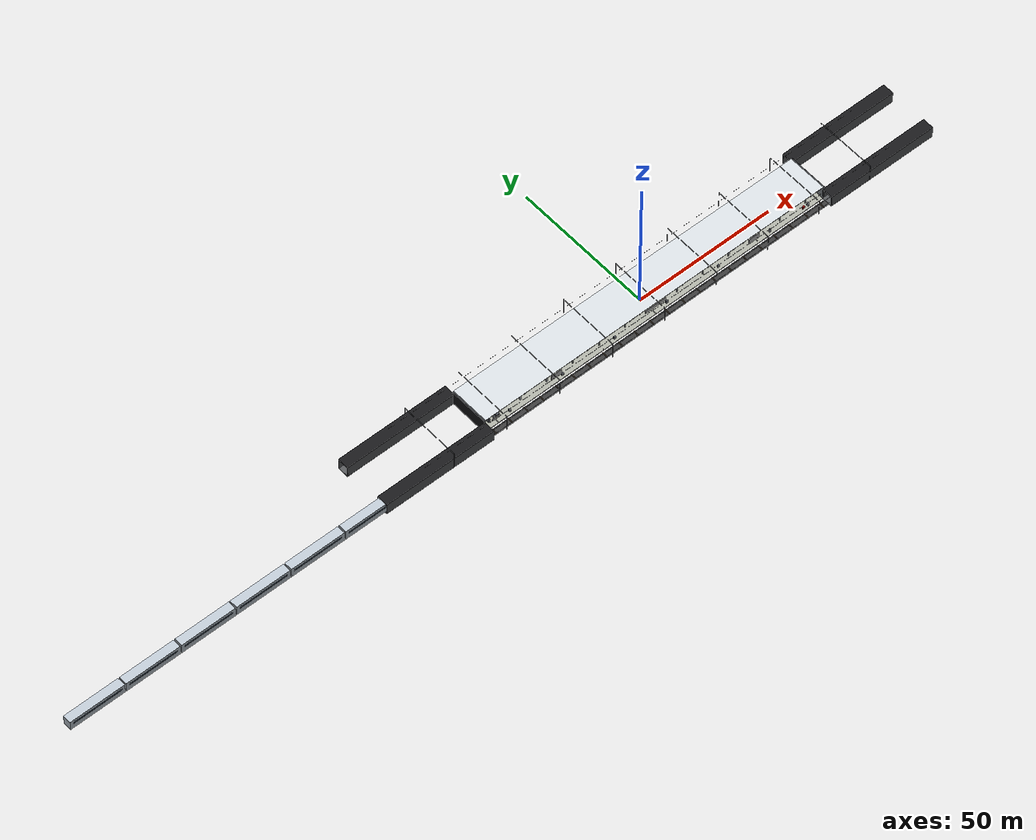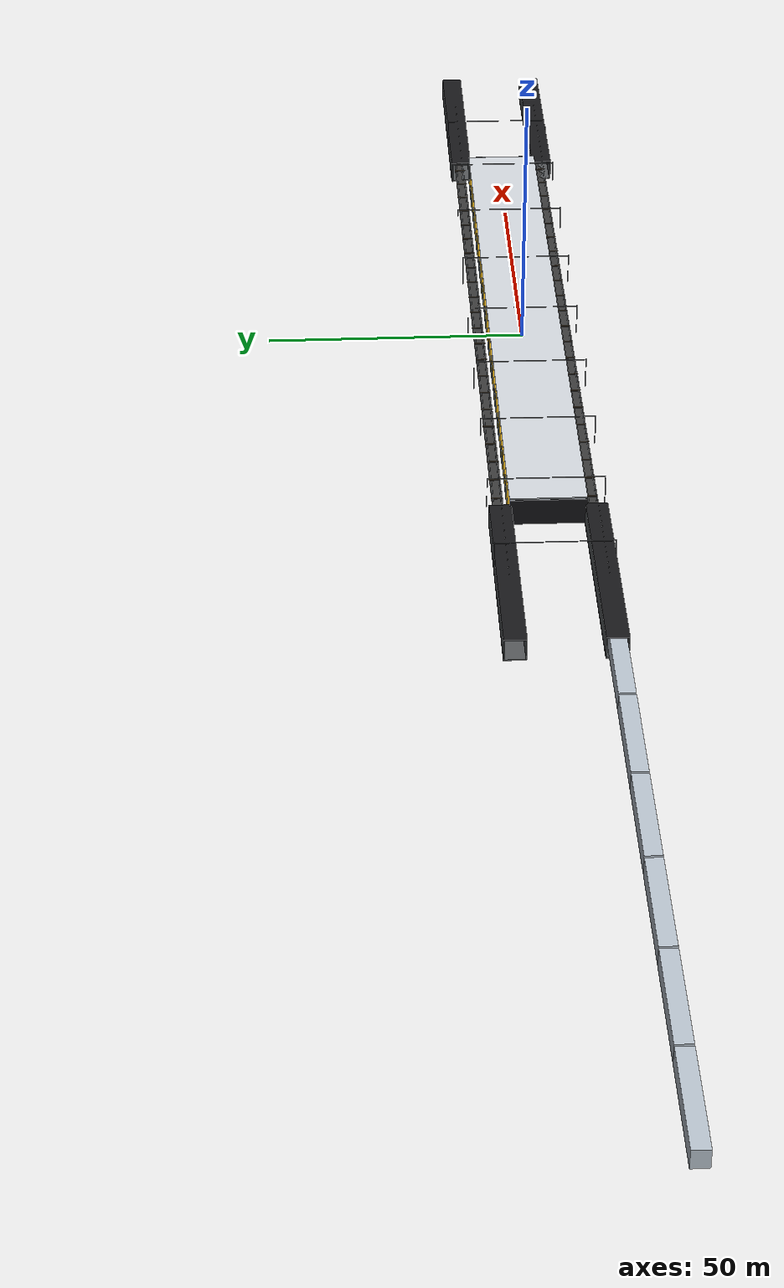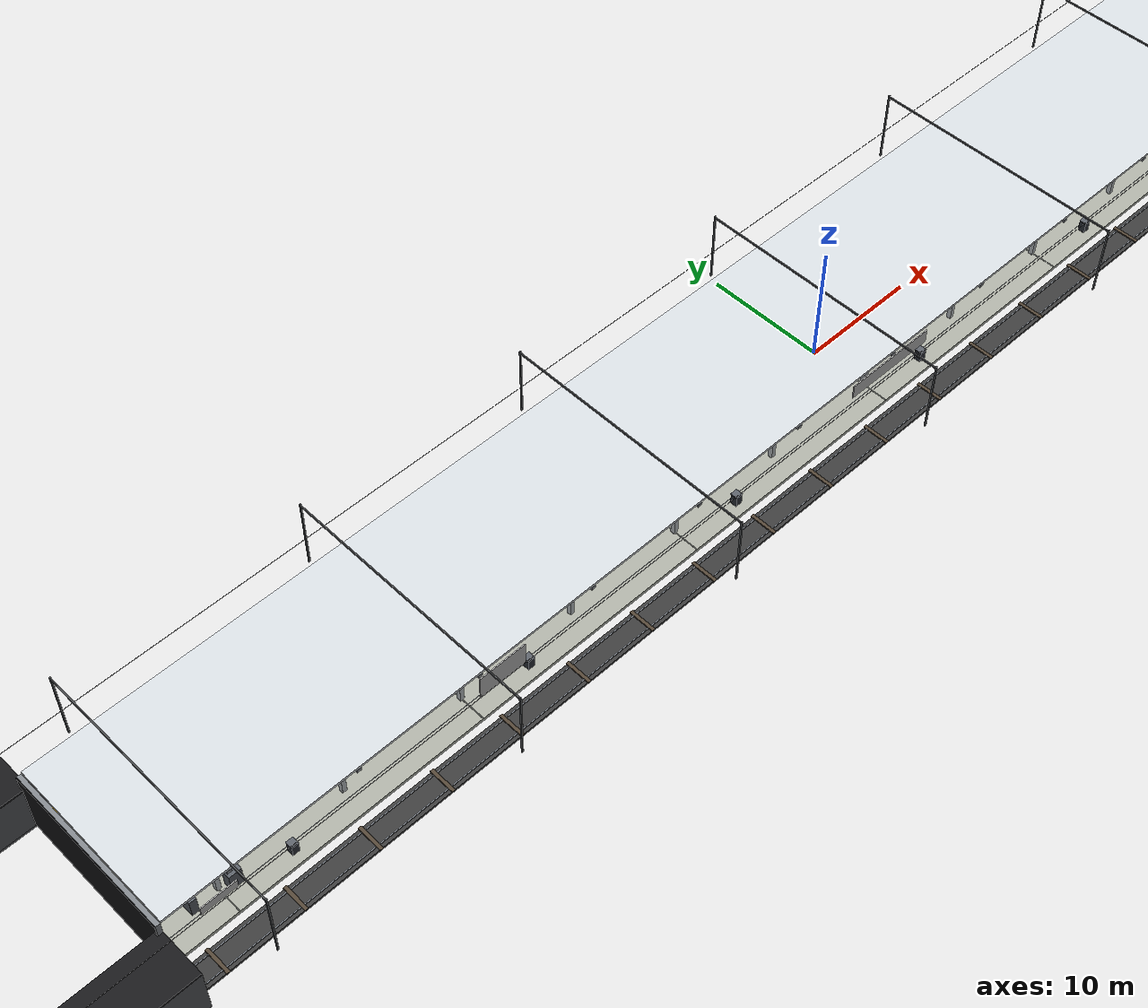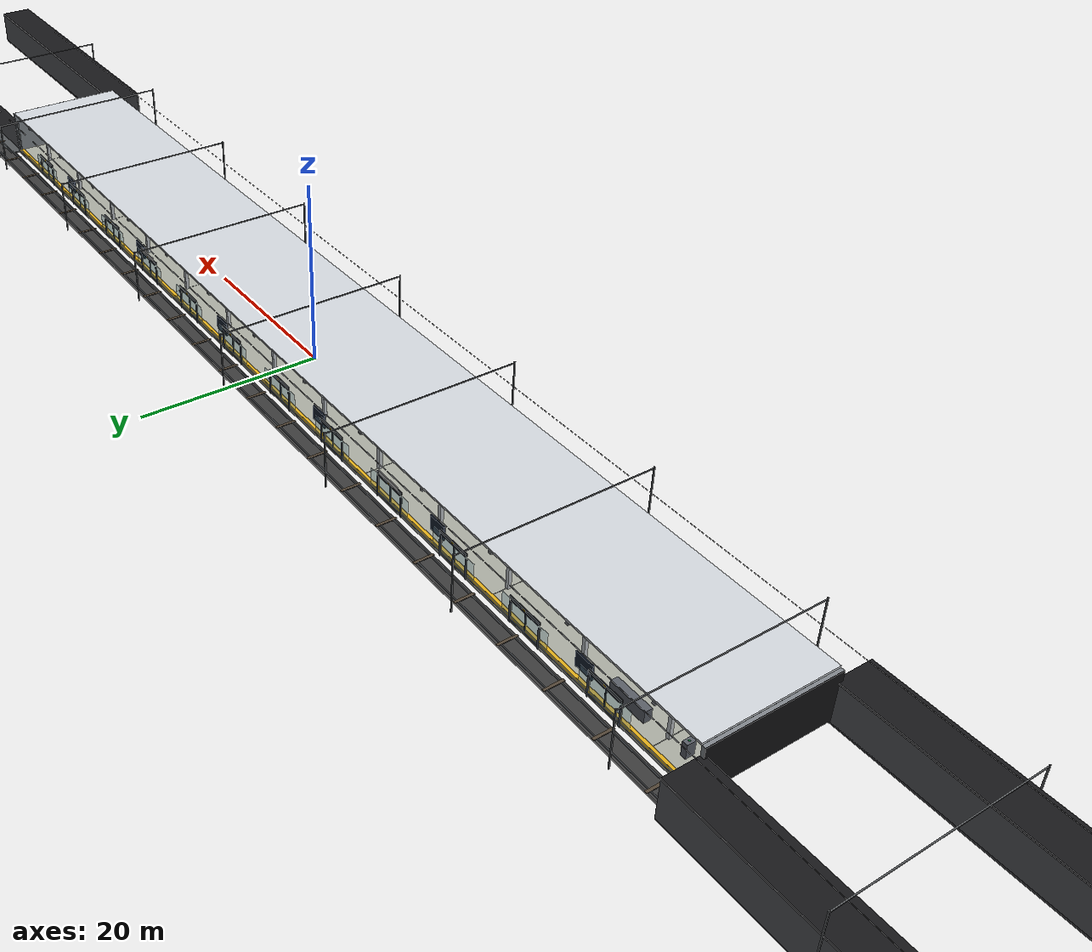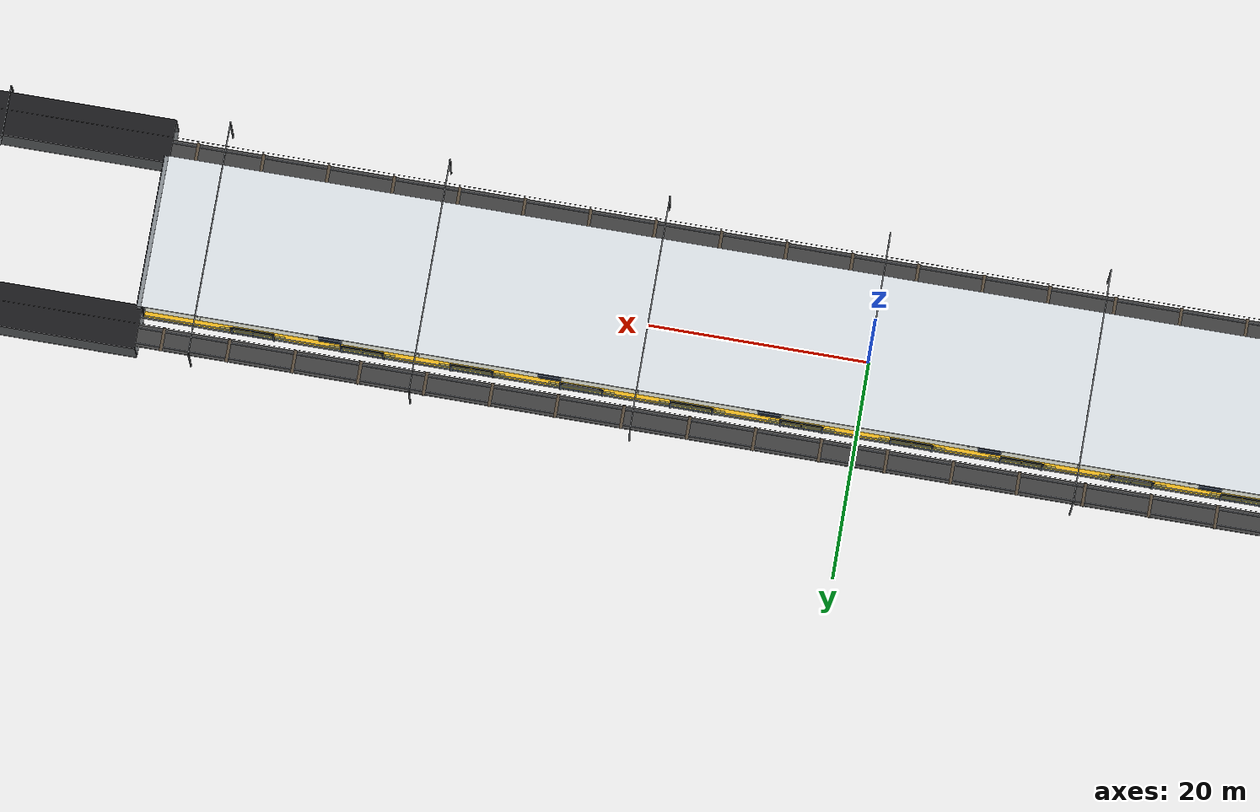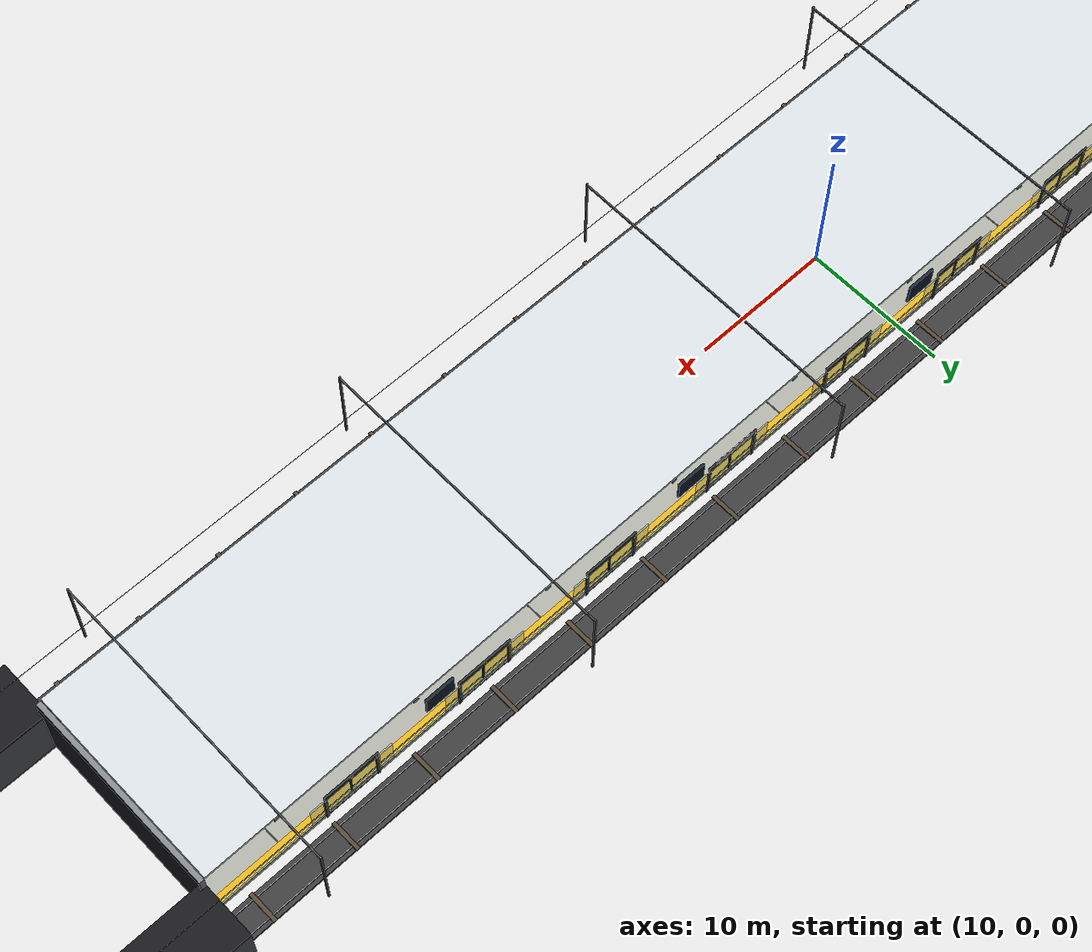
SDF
<?xml version="1.0" ?>
<sdf version="1.8">
  <world name="metro_station">
    <gravity>0 0 -9.8</gravity>
    <physics name="metro_physics" type="ignored">
      <max_step_size>0.001</max_step_size>
      <real_time_factor>1.0</real_time_factor>
      <real_time_update_rate>100</real_time_update_rate>
      <dart>
        <solver><solver_type>dantzig</solver_type></solver>
        <collision_detector>bullet</collision_detector>
      </dart>
    </physics>

    <plugin filename="gz-sim-physics-system" name="gz::sim::systems::Physics"/>
    <plugin filename="gz-sim-user-commands-system" name="gz::sim::systems::UserCommands"/>
    <plugin filename="gz-sim-scene-broadcaster-system" name="gz::sim::systems::SceneBroadcaster"/>
    <plugin filename="gz-sim-sensors-system" name="gz::sim::systems::Sensors">
      <render_engine>ogre2</render_engine>
    </plugin>
    <plugin filename="gz-sim-contact-system" name="gz::sim::systems::Contact"/>

    <scene>
      <ambient>0.58 0.60 0.64 1</ambient>
      <background>0.68 0.76 0.86 1</background>
      <shadows>true</shadows>
    </scene>

    <light type="directional" name="station_sun">
      <cast_shadows>true</cast_shadows>
      <pose>0 0 20 0 0 0</pose>
      <diffuse>0.92 0.90 0.84 1</diffuse>
      <specular>0.2 0.2 0.2 1</specular>
      <direction>-0.35 0.25 -0.90</direction>
    </light>
    <light type="point" name="platform_fill">
      <pose>0 0 5.0 0 0 0</pose>
      <diffuse>0.55 0.58 0.64 1</diffuse>
      <specular>0.08 0.08 0.08 1</specular>
      <attenuation><range>45</range><constant>0.55</constant><linear>0.02</linear><quadratic>0.0</quadratic></attenuation>
    </light>
    <light type="point" name="platform_light_west">
      <pose>-45 0 4.8 0 0 0</pose>
      <diffuse>0.65 0.62 0.52 1</diffuse>
      <attenuation><range>40</range><constant>0.6</constant><linear>0.03</linear><quadratic>0.0</quadratic></attenuation>
    </light>
    <light type="point" name="platform_light_east">
      <pose>45 0 4.8 0 0 0</pose>
      <diffuse>0.65 0.62 0.52 1</diffuse>
      <attenuation><range>40</range><constant>0.6</constant><linear>0.03</linear><quadratic>0.0</quadratic></attenuation>
    </light>
    <light type="point" name="tunnel_light_west">
      <pose>-78 8.65 3.4 0 0 0</pose>
      <diffuse>0.30 0.38 0.50 1</diffuse>
      <attenuation><range>25</range><constant>0.5</constant><linear>0.04</linear><quadratic>0.0</quadratic></attenuation>
    </light>
    <light type="point" name="tunnel_light_east">
      <pose>78 8.65 3.4 0 0 0</pose>
      <diffuse>0.30 0.38 0.50 1</diffuse>
      <attenuation><range>25</range><constant>0.5</constant><linear>0.04</linear><quadratic>0.0</quadratic></attenuation>
    </light>

    <!-- Island platform: 130 x 14 x 0.3 m, top at z=0.30. -->
    <model name="station_platform">
      <static>true</static>
      <link name="platform_link">
        <collision name="platform_collision"><pose>0 0 0.15 0 0 0</pose><geometry><box><size>130.0 14.0 0.3</size></box></geometry></collision>
        <visual name="platform_top_visual"><pose>0 0 0.15 0 0 0</pose><geometry><box><size>130.0 14.0 0.3</size></box></geometry><material><ambient>0.50 0.52 0.50 1</ambient><diffuse>0.66 0.67 0.63 1</diffuse></material></visual><visual name="platform_front_edge"><pose>0 6.95 0.31 0 0 0</pose><geometry><box><size>130.0 0.10 0.02</size></box></geometry><material><ambient>0.38 0.39 0.38 1</ambient><diffuse>0.50 0.51 0.50 1</diffuse></material></visual><visual name="safety_line_visual"><pose>0 6.85 0.305 0 0 0</pose><geometry><box><size>130.0 0.10 0.01</size></box></geometry><material><ambient>0.96 0.72 0.04 1</ambient><diffuse>0.98 0.78 0.08 1</diffuse></material></visual><visual name="tactile_strip_visual"><pose>0 6.55 0.305 0 0 0</pose><geometry><box><size>130.0 0.35 0.01</size></box></geometry><material><ambient>0.82 0.62 0.06 1</ambient><diffuse>0.88 0.68 0.10 1</diffuse></material></visual><visual name="platform_inlay_0"><pose>0 -5.5 0.305 0 0 0</pose><geometry><box><size>130.0 0.04 0.008</size></box></geometry><material><ambient>0.35 0.38 0.40 1</ambient><diffuse>0.45 0.48 0.50 1</diffuse></material></visual><visual name="platform_inlay_1"><pose>0 -3.0 0.305 0 0 0</pose><geometry><box><size>130.0 0.04 0.008</size></box></geometry><material><ambient>0.35 0.38 0.40 1</ambient><diffuse>0.45 0.48 0.50 1</diffuse></material></visual><visual name="platform_inlay_2"><pose>0 -0.5 0.305 0 0 0</pose><geometry><box><size>130.0 0.04 0.008</size></box></geometry><material><ambient>0.35 0.38 0.40 1</ambient><diffuse>0.45 0.48 0.50 1</diffuse></material></visual><visual name="platform_inlay_3"><pose>0 2.0 0.305 0 0 0</pose><geometry><box><size>130.0 0.04 0.008</size></box></geometry><material><ambient>0.35 0.38 0.40 1</ambient><diffuse>0.45 0.48 0.50 1</diffuse></material></visual><visual name="platform_inlay_4"><pose>0 4.5 0.305 0 0 0</pose><geometry><box><size>130.0 0.04 0.008</size></box></geometry><material><ambient>0.35 0.38 0.40 1</ambient><diffuse>0.45 0.48 0.50 1</diffuse></material></visual><visual name="platform_tile_band_0"><pose>-60 0 0.305 0 0 0</pose><geometry><box><size>0.06 14.0 0.008</size></box></geometry><material><ambient>0.42 0.44 0.43 1</ambient><diffuse>0.55 0.57 0.55 1</diffuse></material></visual><visual name="platform_tile_band_1"><pose>-40 0 0.305 0 0 0</pose><geometry><box><size>0.06 14.0 0.008</size></box></geometry><material><ambient>0.42 0.44 0.43 1</ambient><diffuse>0.55 0.57 0.55 1</diffuse></material></visual><visual name="platform_tile_band_2"><pose>-20 0 0.305 0 0 0</pose><geometry><box><size>0.06 14.0 0.008</size></box></geometry><material><ambient>0.42 0.44 0.43 1</ambient><diffuse>0.55 0.57 0.55 1</diffuse></material></visual><visual name="platform_tile_band_3"><pose>0 0 0.305 0 0 0</pose><geometry><box><size>0.06 14.0 0.008</size></box></geometry><material><ambient>0.42 0.44 0.43 1</ambient><diffuse>0.55 0.57 0.55 1</diffuse></material></visual><visual name="platform_tile_band_4"><pose>20 0 0.305 0 0 0</pose><geometry><box><size>0.06 14.0 0.008</size></box></geometry><material><ambient>0.42 0.44 0.43 1</ambient><diffuse>0.55 0.57 0.55 1</diffuse></material></visual><visual name="platform_tile_band_5"><pose>40 0 0.305 0 0 0</pose><geometry><box><size>0.06 14.0 0.008</size></box></geometry><material><ambient>0.42 0.44 0.43 1</ambient><diffuse>0.55 0.57 0.55 1</diffuse></material></visual><visual name="platform_tile_band_6"><pose>60 0 0.305 0 0 0</pose><geometry><box><size>0.06 14.0 0.008</size></box></geometry><material><ambient>0.42 0.44 0.43 1</ambient><diffuse>0.55 0.57 0.55 1</diffuse></material></visual>
      </link>
    </model>

    <model name="track_bed_positive_y">
      <static>true</static>
      <link name="track_link_positive_y">
        <collision name="track_collision_positive_y"><pose>0 8.65 0.10 0 0 0</pose><geometry><box><size>180.0 2.0 0.20</size></box></geometry></collision><visual name="track_ballast_positive_y"><pose>0 8.65 0.10 0 0 0</pose><geometry><box><size>180.0 2.0 0.20</size></box></geometry><material><ambient>0.16 0.16 0.16 1</ambient><diffuse>0.23 0.23 0.23 1</diffuse></material></visual><visual name="rail_inner_positive_y"><pose>0 7.95 0.24 0 0 0</pose><geometry><box><size>180.0 0.08 0.08</size></box></geometry><material><ambient>0.34 0.36 0.39 1</ambient><diffuse>0.50 0.52 0.55 1</diffuse><specular>0.8 0.8 0.8 1</specular></material></visual><visual name="rail_outer_positive_y"><pose>0 9.35 0.24 0 0 0</pose><geometry><box><size>180.0 0.08 0.08</size></box></geometry><material><ambient>0.34 0.36 0.39 1</ambient><diffuse>0.50 0.52 0.55 1</diffuse><specular>0.8 0.8 0.8 1</specular></material></visual><visual name="sleeper_positive_y_00"><pose>-87.0 8.65 0.245 0 0 0</pose><geometry><box><size>0.28 2.15 0.08</size></box></geometry><material><ambient>0.24 0.20 0.16 1</ambient><diffuse>0.32 0.27 0.21 1</diffuse></material></visual><visual name="sleeper_positive_y_01"><pose>-81.0 8.65 0.245 0 0 0</pose><geometry><box><size>0.28 2.15 0.08</size></box></geometry><material><ambient>0.24 0.20 0.16 1</ambient><diffuse>0.32 0.27 0.21 1</diffuse></material></visual><visual name="sleeper_positive_y_02"><pose>-75.0 8.65 0.245 0 0 0</pose><geometry><box><size>0.28 2.15 0.08</size></box></geometry><material><ambient>0.24 0.20 0.16 1</ambient><diffuse>0.32 0.27 0.21 1</diffuse></material></visual><visual name="sleeper_positive_y_03"><pose>-69.0 8.65 0.245 0 0 0</pose><geometry><box><size>0.28 2.15 0.08</size></box></geometry><material><ambient>0.24 0.20 0.16 1</ambient><diffuse>0.32 0.27 0.21 1</diffuse></material></visual><visual name="sleeper_positive_y_04"><pose>-63.0 8.65 0.245 0 0 0</pose><geometry><box><size>0.28 2.15 0.08</size></box></geometry><material><ambient>0.24 0.20 0.16 1</ambient><diffuse>0.32 0.27 0.21 1</diffuse></material></visual><visual name="sleeper_positive_y_05"><pose>-57.0 8.65 0.245 0 0 0</pose><geometry><box><size>0.28 2.15 0.08</size></box></geometry><material><ambient>0.24 0.20 0.16 1</ambient><diffuse>0.32 0.27 0.21 1</diffuse></material></visual><visual name="sleeper_positive_y_06"><pose>-51.0 8.65 0.245 0 0 0</pose><geometry><box><size>0.28 2.15 0.08</size></box></geometry><material><ambient>0.24 0.20 0.16 1</ambient><diffuse>0.32 0.27 0.21 1</diffuse></material></visual><visual name="sleeper_positive_y_07"><pose>-45.0 8.65 0.245 0 0 0</pose><geometry><box><size>0.28 2.15 0.08</size></box></geometry><material><ambient>0.24 0.20 0.16 1</ambient><diffuse>0.32 0.27 0.21 1</diffuse></material></visual><visual name="sleeper_positive_y_08"><pose>-39.0 8.65 0.245 0 0 0</pose><geometry><box><size>0.28 2.15 0.08</size></box></geometry><material><ambient>0.24 0.20 0.16 1</ambient><diffuse>0.32 0.27 0.21 1</diffuse></material></visual><visual name="sleeper_positive_y_09"><pose>-33.0 8.65 0.245 0 0 0</pose><geometry><box><size>0.28 2.15 0.08</size></box></geometry><material><ambient>0.24 0.20 0.16 1</ambient><diffuse>0.32 0.27 0.21 1</diffuse></material></visual><visual name="sleeper_positive_y_10"><pose>-27.0 8.65 0.245 0 0 0</pose><geometry><box><size>0.28 2.15 0.08</size></box></geometry><material><ambient>0.24 0.20 0.16 1</ambient><diffuse>0.32 0.27 0.21 1</diffuse></material></visual><visual name="sleeper_positive_y_11"><pose>-21.0 8.65 0.245 0 0 0</pose><geometry><box><size>0.28 2.15 0.08</size></box></geometry><material><ambient>0.24 0.20 0.16 1</ambient><diffuse>0.32 0.27 0.21 1</diffuse></material></visual><visual name="sleeper_positive_y_12"><pose>-15.0 8.65 0.245 0 0 0</pose><geometry><box><size>0.28 2.15 0.08</size></box></geometry><material><ambient>0.24 0.20 0.16 1</ambient><diffuse>0.32 0.27 0.21 1</diffuse></material></visual><visual name="sleeper_positive_y_13"><pose>-9.0 8.65 0.245 0 0 0</pose><geometry><box><size>0.28 2.15 0.08</size></box></geometry><material><ambient>0.24 0.20 0.16 1</ambient><diffuse>0.32 0.27 0.21 1</diffuse></material></visual><visual name="sleeper_positive_y_14"><pose>-3.0 8.65 0.245 0 0 0</pose><geometry><box><size>0.28 2.15 0.08</size></box></geometry><material><ambient>0.24 0.20 0.16 1</ambient><diffuse>0.32 0.27 0.21 1</diffuse></material></visual><visual name="sleeper_positive_y_15"><pose>3.0 8.65 0.245 0 0 0</pose><geometry><box><size>0.28 2.15 0.08</size></box></geometry><material><ambient>0.24 0.20 0.16 1</ambient><diffuse>0.32 0.27 0.21 1</diffuse></material></visual><visual name="sleeper_positive_y_16"><pose>9.0 8.65 0.245 0 0 0</pose><geometry><box><size>0.28 2.15 0.08</size></box></geometry><material><ambient>0.24 0.20 0.16 1</ambient><diffuse>0.32 0.27 0.21 1</diffuse></material></visual><visual name="sleeper_positive_y_17"><pose>15.0 8.65 0.245 0 0 0</pose><geometry><box><size>0.28 2.15 0.08</size></box></geometry><material><ambient>0.24 0.20 0.16 1</ambient><diffuse>0.32 0.27 0.21 1</diffuse></material></visual><visual name="sleeper_positive_y_18"><pose>21.0 8.65 0.245 0 0 0</pose><geometry><box><size>0.28 2.15 0.08</size></box></geometry><material><ambient>0.24 0.20 0.16 1</ambient><diffuse>0.32 0.27 0.21 1</diffuse></material></visual><visual name="sleeper_positive_y_19"><pose>27.0 8.65 0.245 0 0 0</pose><geometry><box><size>0.28 2.15 0.08</size></box></geometry><material><ambient>0.24 0.20 0.16 1</ambient><diffuse>0.32 0.27 0.21 1</diffuse></material></visual><visual name="sleeper_positive_y_20"><pose>33.0 8.65 0.245 0 0 0</pose><geometry><box><size>0.28 2.15 0.08</size></box></geometry><material><ambient>0.24 0.20 0.16 1</ambient><diffuse>0.32 0.27 0.21 1</diffuse></material></visual><visual name="sleeper_positive_y_21"><pose>39.0 8.65 0.245 0 0 0</pose><geometry><box><size>0.28 2.15 0.08</size></box></geometry><material><ambient>0.24 0.20 0.16 1</ambient><diffuse>0.32 0.27 0.21 1</diffuse></material></visual><visual name="sleeper_positive_y_22"><pose>45.0 8.65 0.245 0 0 0</pose><geometry><box><size>0.28 2.15 0.08</size></box></geometry><material><ambient>0.24 0.20 0.16 1</ambient><diffuse>0.32 0.27 0.21 1</diffuse></material></visual><visual name="sleeper_positive_y_23"><pose>51.0 8.65 0.245 0 0 0</pose><geometry><box><size>0.28 2.15 0.08</size></box></geometry><material><ambient>0.24 0.20 0.16 1</ambient><diffuse>0.32 0.27 0.21 1</diffuse></material></visual><visual name="sleeper_positive_y_24"><pose>57.0 8.65 0.245 0 0 0</pose><geometry><box><size>0.28 2.15 0.08</size></box></geometry><material><ambient>0.24 0.20 0.16 1</ambient><diffuse>0.32 0.27 0.21 1</diffuse></material></visual><visual name="sleeper_positive_y_25"><pose>63.0 8.65 0.245 0 0 0</pose><geometry><box><size>0.28 2.15 0.08</size></box></geometry><material><ambient>0.24 0.20 0.16 1</ambient><diffuse>0.32 0.27 0.21 1</diffuse></material></visual><visual name="sleeper_positive_y_26"><pose>69.0 8.65 0.245 0 0 0</pose><geometry><box><size>0.28 2.15 0.08</size></box></geometry><material><ambient>0.24 0.20 0.16 1</ambient><diffuse>0.32 0.27 0.21 1</diffuse></material></visual><visual name="sleeper_positive_y_27"><pose>75.0 8.65 0.245 0 0 0</pose><geometry><box><size>0.28 2.15 0.08</size></box></geometry><material><ambient>0.24 0.20 0.16 1</ambient><diffuse>0.32 0.27 0.21 1</diffuse></material></visual><visual name="sleeper_positive_y_28"><pose>81.0 8.65 0.245 0 0 0</pose><geometry><box><size>0.28 2.15 0.08</size></box></geometry><material><ambient>0.24 0.20 0.16 1</ambient><diffuse>0.32 0.27 0.21 1</diffuse></material></visual><visual name="sleeper_positive_y_29"><pose>87.0 8.65 0.245 0 0 0</pose><geometry><box><size>0.28 2.15 0.08</size></box></geometry><material><ambient>0.24 0.20 0.16 1</ambient><diffuse>0.32 0.27 0.21 1</diffuse></material></visual>
      </link>
    </model>

    <model name="track_bed_negative_y">
      <static>true</static>
      <link name="track_link_negative_y">
        <collision name="track_collision_negative_y"><pose>0 -8.65 0.10 0 0 0</pose><geometry><box><size>180.0 2.0 0.20</size></box></geometry></collision><visual name="track_ballast_negative_y"><pose>0 -8.65 0.10 0 0 0</pose><geometry><box><size>180.0 2.0 0.20</size></box></geometry><material><ambient>0.16 0.16 0.16 1</ambient><diffuse>0.23 0.23 0.23 1</diffuse></material></visual><visual name="rail_inner_negative_y"><pose>0 -9.35 0.24 0 0 0</pose><geometry><box><size>180.0 0.08 0.08</size></box></geometry><material><ambient>0.34 0.36 0.39 1</ambient><diffuse>0.50 0.52 0.55 1</diffuse><specular>0.8 0.8 0.8 1</specular></material></visual><visual name="rail_outer_negative_y"><pose>0 -7.95 0.24 0 0 0</pose><geometry><box><size>180.0 0.08 0.08</size></box></geometry><material><ambient>0.34 0.36 0.39 1</ambient><diffuse>0.50 0.52 0.55 1</diffuse><specular>0.8 0.8 0.8 1</specular></material></visual><visual name="sleeper_negative_y_00"><pose>-87.0 -8.65 0.245 0 0 0</pose><geometry><box><size>0.28 2.15 0.08</size></box></geometry><material><ambient>0.24 0.20 0.16 1</ambient><diffuse>0.32 0.27 0.21 1</diffuse></material></visual><visual name="sleeper_negative_y_01"><pose>-81.0 -8.65 0.245 0 0 0</pose><geometry><box><size>0.28 2.15 0.08</size></box></geometry><material><ambient>0.24 0.20 0.16 1</ambient><diffuse>0.32 0.27 0.21 1</diffuse></material></visual><visual name="sleeper_negative_y_02"><pose>-75.0 -8.65 0.245 0 0 0</pose><geometry><box><size>0.28 2.15 0.08</size></box></geometry><material><ambient>0.24 0.20 0.16 1</ambient><diffuse>0.32 0.27 0.21 1</diffuse></material></visual><visual name="sleeper_negative_y_03"><pose>-69.0 -8.65 0.245 0 0 0</pose><geometry><box><size>0.28 2.15 0.08</size></box></geometry><material><ambient>0.24 0.20 0.16 1</ambient><diffuse>0.32 0.27 0.21 1</diffuse></material></visual><visual name="sleeper_negative_y_04"><pose>-63.0 -8.65 0.245 0 0 0</pose><geometry><box><size>0.28 2.15 0.08</size></box></geometry><material><ambient>0.24 0.20 0.16 1</ambient><diffuse>0.32 0.27 0.21 1</diffuse></material></visual><visual name="sleeper_negative_y_05"><pose>-57.0 -8.65 0.245 0 0 0</pose><geometry><box><size>0.28 2.15 0.08</size></box></geometry><material><ambient>0.24 0.20 0.16 1</ambient><diffuse>0.32 0.27 0.21 1</diffuse></material></visual><visual name="sleeper_negative_y_06"><pose>-51.0 -8.65 0.245 0 0 0</pose><geometry><box><size>0.28 2.15 0.08</size></box></geometry><material><ambient>0.24 0.20 0.16 1</ambient><diffuse>0.32 0.27 0.21 1</diffuse></material></visual><visual name="sleeper_negative_y_07"><pose>-45.0 -8.65 0.245 0 0 0</pose><geometry><box><size>0.28 2.15 0.08</size></box></geometry><material><ambient>0.24 0.20 0.16 1</ambient><diffuse>0.32 0.27 0.21 1</diffuse></material></visual><visual name="sleeper_negative_y_08"><pose>-39.0 -8.65 0.245 0 0 0</pose><geometry><box><size>0.28 2.15 0.08</size></box></geometry><material><ambient>0.24 0.20 0.16 1</ambient><diffuse>0.32 0.27 0.21 1</diffuse></material></visual><visual name="sleeper_negative_y_09"><pose>-33.0 -8.65 0.245 0 0 0</pose><geometry><box><size>0.28 2.15 0.08</size></box></geometry><material><ambient>0.24 0.20 0.16 1</ambient><diffuse>0.32 0.27 0.21 1</diffuse></material></visual><visual name="sleeper_negative_y_10"><pose>-27.0 -8.65 0.245 0 0 0</pose><geometry><box><size>0.28 2.15 0.08</size></box></geometry><material><ambient>0.24 0.20 0.16 1</ambient><diffuse>0.32 0.27 0.21 1</diffuse></material></visual><visual name="sleeper_negative_y_11"><pose>-21.0 -8.65 0.245 0 0 0</pose><geometry><box><size>0.28 2.15 0.08</size></box></geometry><material><ambient>0.24 0.20 0.16 1</ambient><diffuse>0.32 0.27 0.21 1</diffuse></material></visual><visual name="sleeper_negative_y_12"><pose>-15.0 -8.65 0.245 0 0 0</pose><geometry><box><size>0.28 2.15 0.08</size></box></geometry><material><ambient>0.24 0.20 0.16 1</ambient><diffuse>0.32 0.27 0.21 1</diffuse></material></visual><visual name="sleeper_negative_y_13"><pose>-9.0 -8.65 0.245 0 0 0</pose><geometry><box><size>0.28 2.15 0.08</size></box></geometry><material><ambient>0.24 0.20 0.16 1</ambient><diffuse>0.32 0.27 0.21 1</diffuse></material></visual><visual name="sleeper_negative_y_14"><pose>-3.0 -8.65 0.245 0 0 0</pose><geometry><box><size>0.28 2.15 0.08</size></box></geometry><material><ambient>0.24 0.20 0.16 1</ambient><diffuse>0.32 0.27 0.21 1</diffuse></material></visual><visual name="sleeper_negative_y_15"><pose>3.0 -8.65 0.245 0 0 0</pose><geometry><box><size>0.28 2.15 0.08</size></box></geometry><material><ambient>0.24 0.20 0.16 1</ambient><diffuse>0.32 0.27 0.21 1</diffuse></material></visual><visual name="sleeper_negative_y_16"><pose>9.0 -8.65 0.245 0 0 0</pose><geometry><box><size>0.28 2.15 0.08</size></box></geometry><material><ambient>0.24 0.20 0.16 1</ambient><diffuse>0.32 0.27 0.21 1</diffuse></material></visual><visual name="sleeper_negative_y_17"><pose>15.0 -8.65 0.245 0 0 0</pose><geometry><box><size>0.28 2.15 0.08</size></box></geometry><material><ambient>0.24 0.20 0.16 1</ambient><diffuse>0.32 0.27 0.21 1</diffuse></material></visual><visual name="sleeper_negative_y_18"><pose>21.0 -8.65 0.245 0 0 0</pose><geometry><box><size>0.28 2.15 0.08</size></box></geometry><material><ambient>0.24 0.20 0.16 1</ambient><diffuse>0.32 0.27 0.21 1</diffuse></material></visual><visual name="sleeper_negative_y_19"><pose>27.0 -8.65 0.245 0 0 0</pose><geometry><box><size>0.28 2.15 0.08</size></box></geometry><material><ambient>0.24 0.20 0.16 1</ambient><diffuse>0.32 0.27 0.21 1</diffuse></material></visual><visual name="sleeper_negative_y_20"><pose>33.0 -8.65 0.245 0 0 0</pose><geometry><box><size>0.28 2.15 0.08</size></box></geometry><material><ambient>0.24 0.20 0.16 1</ambient><diffuse>0.32 0.27 0.21 1</diffuse></material></visual><visual name="sleeper_negative_y_21"><pose>39.0 -8.65 0.245 0 0 0</pose><geometry><box><size>0.28 2.15 0.08</size></box></geometry><material><ambient>0.24 0.20 0.16 1</ambient><diffuse>0.32 0.27 0.21 1</diffuse></material></visual><visual name="sleeper_negative_y_22"><pose>45.0 -8.65 0.245 0 0 0</pose><geometry><box><size>0.28 2.15 0.08</size></box></geometry><material><ambient>0.24 0.20 0.16 1</ambient><diffuse>0.32 0.27 0.21 1</diffuse></material></visual><visual name="sleeper_negative_y_23"><pose>51.0 -8.65 0.245 0 0 0</pose><geometry><box><size>0.28 2.15 0.08</size></box></geometry><material><ambient>0.24 0.20 0.16 1</ambient><diffuse>0.32 0.27 0.21 1</diffuse></material></visual><visual name="sleeper_negative_y_24"><pose>57.0 -8.65 0.245 0 0 0</pose><geometry><box><size>0.28 2.15 0.08</size></box></geometry><material><ambient>0.24 0.20 0.16 1</ambient><diffuse>0.32 0.27 0.21 1</diffuse></material></visual><visual name="sleeper_negative_y_25"><pose>63.0 -8.65 0.245 0 0 0</pose><geometry><box><size>0.28 2.15 0.08</size></box></geometry><material><ambient>0.24 0.20 0.16 1</ambient><diffuse>0.32 0.27 0.21 1</diffuse></material></visual><visual name="sleeper_negative_y_26"><pose>69.0 -8.65 0.245 0 0 0</pose><geometry><box><size>0.28 2.15 0.08</size></box></geometry><material><ambient>0.24 0.20 0.16 1</ambient><diffuse>0.32 0.27 0.21 1</diffuse></material></visual><visual name="sleeper_negative_y_27"><pose>75.0 -8.65 0.245 0 0 0</pose><geometry><box><size>0.28 2.15 0.08</size></box></geometry><material><ambient>0.24 0.20 0.16 1</ambient><diffuse>0.32 0.27 0.21 1</diffuse></material></visual><visual name="sleeper_negative_y_28"><pose>81.0 -8.65 0.245 0 0 0</pose><geometry><box><size>0.28 2.15 0.08</size></box></geometry><material><ambient>0.24 0.20 0.16 1</ambient><diffuse>0.32 0.27 0.21 1</diffuse></material></visual><visual name="sleeper_negative_y_29"><pose>87.0 -8.65 0.245 0 0 0</pose><geometry><box><size>0.28 2.15 0.08</size></box></geometry><material><ambient>0.24 0.20 0.16 1</ambient><diffuse>0.32 0.27 0.21 1</diffuse></material></visual>
      </link>
    </model>

    <model name="station_structure">
      <static>true</static>
      <link name="structure_link">
        <visual name="station_ceiling"><pose>0 0 5.48 0 0 0</pose><geometry><box><size>130.0 14.0 0.20</size></box></geometry><material><ambient>0.70 0.72 0.74 1</ambient><diffuse>0.82 0.84 0.86 1</diffuse></material></visual><visual name="roof_beam_00"><pose>-60 0 5.18 0 0 0</pose><geometry><box><size>0.35 14.0 0.25</size></box></geometry><material><ambient>0.42 0.44 0.46 1</ambient><diffuse>0.55 0.57 0.59 1</diffuse></material></visual><visual name="column_00_n"><pose>-60 -4.8 2.80 0 0 0</pose><geometry><box><size>0.35 0.35 5.00</size></box></geometry><material><ambient>0.60 0.62 0.64 1</ambient><diffuse>0.74 0.76 0.78 1</diffuse></material></visual><visual name="column_00_p"><pose>-60 4.8 2.80 0 0 0</pose><geometry><box><size>0.35 0.35 5.00</size></box></geometry><material><ambient>0.60 0.62 0.64 1</ambient><diffuse>0.74 0.76 0.78 1</diffuse></material></visual><visual name="roof_beam_01"><pose>-50 0 5.18 0 0 0</pose><geometry><box><size>0.35 14.0 0.25</size></box></geometry><material><ambient>0.42 0.44 0.46 1</ambient><diffuse>0.55 0.57 0.59 1</diffuse></material></visual><visual name="column_01_n"><pose>-50 -4.8 2.80 0 0 0</pose><geometry><box><size>0.35 0.35 5.00</size></box></geometry><material><ambient>0.60 0.62 0.64 1</ambient><diffuse>0.74 0.76 0.78 1</diffuse></material></visual><visual name="column_01_p"><pose>-50 4.8 2.80 0 0 0</pose><geometry><box><size>0.35 0.35 5.00</size></box></geometry><material><ambient>0.60 0.62 0.64 1</ambient><diffuse>0.74 0.76 0.78 1</diffuse></material></visual><visual name="roof_beam_02"><pose>-40 0 5.18 0 0 0</pose><geometry><box><size>0.35 14.0 0.25</size></box></geometry><material><ambient>0.42 0.44 0.46 1</ambient><diffuse>0.55 0.57 0.59 1</diffuse></material></visual><visual name="column_02_n"><pose>-40 -4.8 2.80 0 0 0</pose><geometry><box><size>0.35 0.35 5.00</size></box></geometry><material><ambient>0.60 0.62 0.64 1</ambient><diffuse>0.74 0.76 0.78 1</diffuse></material></visual><visual name="column_02_p"><pose>-40 4.8 2.80 0 0 0</pose><geometry><box><size>0.35 0.35 5.00</size></box></geometry><material><ambient>0.60 0.62 0.64 1</ambient><diffuse>0.74 0.76 0.78 1</diffuse></material></visual><visual name="roof_beam_03"><pose>-30 0 5.18 0 0 0</pose><geometry><box><size>0.35 14.0 0.25</size></box></geometry><material><ambient>0.42 0.44 0.46 1</ambient><diffuse>0.55 0.57 0.59 1</diffuse></material></visual><visual name="column_03_n"><pose>-30 -4.8 2.80 0 0 0</pose><geometry><box><size>0.35 0.35 5.00</size></box></geometry><material><ambient>0.60 0.62 0.64 1</ambient><diffuse>0.74 0.76 0.78 1</diffuse></material></visual><visual name="column_03_p"><pose>-30 4.8 2.80 0 0 0</pose><geometry><box><size>0.35 0.35 5.00</size></box></geometry><material><ambient>0.60 0.62 0.64 1</ambient><diffuse>0.74 0.76 0.78 1</diffuse></material></visual><visual name="roof_beam_04"><pose>-20 0 5.18 0 0 0</pose><geometry><box><size>0.35 14.0 0.25</size></box></geometry><material><ambient>0.42 0.44 0.46 1</ambient><diffuse>0.55 0.57 0.59 1</diffuse></material></visual><visual name="column_04_n"><pose>-20 -4.8 2.80 0 0 0</pose><geometry><box><size>0.35 0.35 5.00</size></box></geometry><material><ambient>0.60 0.62 0.64 1</ambient><diffuse>0.74 0.76 0.78 1</diffuse></material></visual><visual name="column_04_p"><pose>-20 4.8 2.80 0 0 0</pose><geometry><box><size>0.35 0.35 5.00</size></box></geometry><material><ambient>0.60 0.62 0.64 1</ambient><diffuse>0.74 0.76 0.78 1</diffuse></material></visual><visual name="roof_beam_05"><pose>-10 0 5.18 0 0 0</pose><geometry><box><size>0.35 14.0 0.25</size></box></geometry><material><ambient>0.42 0.44 0.46 1</ambient><diffuse>0.55 0.57 0.59 1</diffuse></material></visual><visual name="column_05_n"><pose>-10 -4.8 2.80 0 0 0</pose><geometry><box><size>0.35 0.35 5.00</size></box></geometry><material><ambient>0.60 0.62 0.64 1</ambient><diffuse>0.74 0.76 0.78 1</diffuse></material></visual><visual name="column_05_p"><pose>-10 4.8 2.80 0 0 0</pose><geometry><box><size>0.35 0.35 5.00</size></box></geometry><material><ambient>0.60 0.62 0.64 1</ambient><diffuse>0.74 0.76 0.78 1</diffuse></material></visual><visual name="roof_beam_06"><pose>0 0 5.18 0 0 0</pose><geometry><box><size>0.35 14.0 0.25</size></box></geometry><material><ambient>0.42 0.44 0.46 1</ambient><diffuse>0.55 0.57 0.59 1</diffuse></material></visual><visual name="column_06_n"><pose>0 -4.8 2.80 0 0 0</pose><geometry><box><size>0.35 0.35 5.00</size></box></geometry><material><ambient>0.60 0.62 0.64 1</ambient><diffuse>0.74 0.76 0.78 1</diffuse></material></visual><visual name="column_06_p"><pose>0 4.8 2.80 0 0 0</pose><geometry><box><size>0.35 0.35 5.00</size></box></geometry><material><ambient>0.60 0.62 0.64 1</ambient><diffuse>0.74 0.76 0.78 1</diffuse></material></visual><visual name="roof_beam_07"><pose>10 0 5.18 0 0 0</pose><geometry><box><size>0.35 14.0 0.25</size></box></geometry><material><ambient>0.42 0.44 0.46 1</ambient><diffuse>0.55 0.57 0.59 1</diffuse></material></visual><visual name="column_07_n"><pose>10 -4.8 2.80 0 0 0</pose><geometry><box><size>0.35 0.35 5.00</size></box></geometry><material><ambient>0.60 0.62 0.64 1</ambient><diffuse>0.74 0.76 0.78 1</diffuse></material></visual><visual name="column_07_p"><pose>10 4.8 2.80 0 0 0</pose><geometry><box><size>0.35 0.35 5.00</size></box></geometry><material><ambient>0.60 0.62 0.64 1</ambient><diffuse>0.74 0.76 0.78 1</diffuse></material></visual><visual name="roof_beam_08"><pose>20 0 5.18 0 0 0</pose><geometry><box><size>0.35 14.0 0.25</size></box></geometry><material><ambient>0.42 0.44 0.46 1</ambient><diffuse>0.55 0.57 0.59 1</diffuse></material></visual><visual name="column_08_n"><pose>20 -4.8 2.80 0 0 0</pose><geometry><box><size>0.35 0.35 5.00</size></box></geometry><material><ambient>0.60 0.62 0.64 1</ambient><diffuse>0.74 0.76 0.78 1</diffuse></material></visual><visual name="column_08_p"><pose>20 4.8 2.80 0 0 0</pose><geometry><box><size>0.35 0.35 5.00</size></box></geometry><material><ambient>0.60 0.62 0.64 1</ambient><diffuse>0.74 0.76 0.78 1</diffuse></material></visual><visual name="roof_beam_09"><pose>30 0 5.18 0 0 0</pose><geometry><box><size>0.35 14.0 0.25</size></box></geometry><material><ambient>0.42 0.44 0.46 1</ambient><diffuse>0.55 0.57 0.59 1</diffuse></material></visual><visual name="column_09_n"><pose>30 -4.8 2.80 0 0 0</pose><geometry><box><size>0.35 0.35 5.00</size></box></geometry><material><ambient>0.60 0.62 0.64 1</ambient><diffuse>0.74 0.76 0.78 1</diffuse></material></visual><visual name="column_09_p"><pose>30 4.8 2.80 0 0 0</pose><geometry><box><size>0.35 0.35 5.00</size></box></geometry><material><ambient>0.60 0.62 0.64 1</ambient><diffuse>0.74 0.76 0.78 1</diffuse></material></visual><visual name="roof_beam_10"><pose>40 0 5.18 0 0 0</pose><geometry><box><size>0.35 14.0 0.25</size></box></geometry><material><ambient>0.42 0.44 0.46 1</ambient><diffuse>0.55 0.57 0.59 1</diffuse></material></visual><visual name="column_10_n"><pose>40 -4.8 2.80 0 0 0</pose><geometry><box><size>0.35 0.35 5.00</size></box></geometry><material><ambient>0.60 0.62 0.64 1</ambient><diffuse>0.74 0.76 0.78 1</diffuse></material></visual><visual name="column_10_p"><pose>40 4.8 2.80 0 0 0</pose><geometry><box><size>0.35 0.35 5.00</size></box></geometry><material><ambient>0.60 0.62 0.64 1</ambient><diffuse>0.74 0.76 0.78 1</diffuse></material></visual><visual name="roof_beam_11"><pose>50 0 5.18 0 0 0</pose><geometry><box><size>0.35 14.0 0.25</size></box></geometry><material><ambient>0.42 0.44 0.46 1</ambient><diffuse>0.55 0.57 0.59 1</diffuse></material></visual><visual name="column_11_n"><pose>50 -4.8 2.80 0 0 0</pose><geometry><box><size>0.35 0.35 5.00</size></box></geometry><material><ambient>0.60 0.62 0.64 1</ambient><diffuse>0.74 0.76 0.78 1</diffuse></material></visual><visual name="column_11_p"><pose>50 4.8 2.80 0 0 0</pose><geometry><box><size>0.35 0.35 5.00</size></box></geometry><material><ambient>0.60 0.62 0.64 1</ambient><diffuse>0.74 0.76 0.78 1</diffuse></material></visual><visual name="roof_beam_12"><pose>60 0 5.18 0 0 0</pose><geometry><box><size>0.35 14.0 0.25</size></box></geometry><material><ambient>0.42 0.44 0.46 1</ambient><diffuse>0.55 0.57 0.59 1</diffuse></material></visual><visual name="column_12_n"><pose>60 -4.8 2.80 0 0 0</pose><geometry><box><size>0.35 0.35 5.00</size></box></geometry><material><ambient>0.60 0.62 0.64 1</ambient><diffuse>0.74 0.76 0.78 1</diffuse></material></visual><visual name="column_12_p"><pose>60 4.8 2.80 0 0 0</pose><geometry><box><size>0.35 0.35 5.00</size></box></geometry><material><ambient>0.60 0.62 0.64 1</ambient><diffuse>0.74 0.76 0.78 1</diffuse></material></visual><visual name="light_strip_0"><pose>0 -5.5 5.36 0 0 0</pose><geometry><box><size>128.0 0.10 0.035</size></box></geometry><material><ambient>1.0 0.95 0.80 1</ambient><diffuse>1.0 0.97 0.86 1</diffuse><emissive>1.0 0.92 0.72 1</emissive></material></visual><visual name="light_strip_1"><pose>0 -2.75 5.36 0 0 0</pose><geometry><box><size>128.0 0.10 0.035</size></box></geometry><material><ambient>1.0 0.95 0.80 1</ambient><diffuse>1.0 0.97 0.86 1</diffuse><emissive>1.0 0.92 0.72 1</emissive></material></visual><visual name="light_strip_2"><pose>0 0.0 5.36 0 0 0</pose><geometry><box><size>128.0 0.10 0.035</size></box></geometry><material><ambient>1.0 0.95 0.80 1</ambient><diffuse>1.0 0.97 0.86 1</diffuse><emissive>1.0 0.92 0.72 1</emissive></material></visual><visual name="light_strip_3"><pose>0 2.75 5.36 0 0 0</pose><geometry><box><size>128.0 0.10 0.035</size></box></geometry><material><ambient>1.0 0.95 0.80 1</ambient><diffuse>1.0 0.97 0.86 1</diffuse><emissive>1.0 0.92 0.72 1</emissive></material></visual><visual name="light_strip_4"><pose>0 5.5 5.36 0 0 0</pose><geometry><box><size>128.0 0.10 0.035</size></box></geometry><material><ambient>1.0 0.95 0.80 1</ambient><diffuse>1.0 0.97 0.86 1</diffuse><emissive>1.0 0.92 0.72 1</emissive></material></visual>
      </link>
    </model>

    <model name="station_furniture">
      <static>true</static>
      <link name="furniture_link">
        <visual name="bench_seat_0"><pose>-45 -4.0 0.78 0 0 0</pose><geometry><box><size>3.0 0.62 0.12</size></box></geometry><material><ambient>0.35 0.22 0.12 1</ambient><diffuse>0.48 0.30 0.16 1</diffuse></material></visual><visual name="bench_back_0"><pose>-45 -4.28 1.18 0 0 0</pose><geometry><box><size>3.0 0.10 0.70</size></box></geometry><material><ambient>0.35 0.22 0.12 1</ambient><diffuse>0.48 0.30 0.16 1</diffuse></material></visual><visual name="bench_leg_0_0"><pose>-46.25 -4.0 0.48 0 0 0</pose><geometry><box><size>0.10 0.55 0.36</size></box></geometry><material><ambient>0.25 0.27 0.29 1</ambient><diffuse>0.35 0.37 0.40 1</diffuse></material></visual><visual name="bench_leg_0_1"><pose>-43.75 -4.0 0.48 0 0 0</pose><geometry><box><size>0.10 0.55 0.36</size></box></geometry><material><ambient>0.25 0.27 0.29 1</ambient><diffuse>0.35 0.37 0.40 1</diffuse></material></visual><visual name="bench_seat_1"><pose>-25 -4.0 0.78 0 0 0</pose><geometry><box><size>3.0 0.62 0.12</size></box></geometry><material><ambient>0.35 0.22 0.12 1</ambient><diffuse>0.48 0.30 0.16 1</diffuse></material></visual><visual name="bench_back_1"><pose>-25 -4.28 1.18 0 0 0</pose><geometry><box><size>3.0 0.10 0.70</size></box></geometry><material><ambient>0.35 0.22 0.12 1</ambient><diffuse>0.48 0.30 0.16 1</diffuse></material></visual><visual name="bench_leg_1_0"><pose>-26.25 -4.0 0.48 0 0 0</pose><geometry><box><size>0.10 0.55 0.36</size></box></geometry><material><ambient>0.25 0.27 0.29 1</ambient><diffuse>0.35 0.37 0.40 1</diffuse></material></visual><visual name="bench_leg_1_1"><pose>-23.75 -4.0 0.48 0 0 0</pose><geometry><box><size>0.10 0.55 0.36</size></box></geometry><material><ambient>0.25 0.27 0.29 1</ambient><diffuse>0.35 0.37 0.40 1</diffuse></material></visual><visual name="bench_seat_2"><pose>-5 -4.0 0.78 0 0 0</pose><geometry><box><size>3.0 0.62 0.12</size></box></geometry><material><ambient>0.35 0.22 0.12 1</ambient><diffuse>0.48 0.30 0.16 1</diffuse></material></visual><visual name="bench_back_2"><pose>-5 -4.28 1.18 0 0 0</pose><geometry><box><size>3.0 0.10 0.70</size></box></geometry><material><ambient>0.35 0.22 0.12 1</ambient><diffuse>0.48 0.30 0.16 1</diffuse></material></visual><visual name="bench_leg_2_0"><pose>-6.25 -4.0 0.48 0 0 0</pose><geometry><box><size>0.10 0.55 0.36</size></box></geometry><material><ambient>0.25 0.27 0.29 1</ambient><diffuse>0.35 0.37 0.40 1</diffuse></material></visual><visual name="bench_leg_2_1"><pose>-3.75 -4.0 0.48 0 0 0</pose><geometry><box><size>0.10 0.55 0.36</size></box></geometry><material><ambient>0.25 0.27 0.29 1</ambient><diffuse>0.35 0.37 0.40 1</diffuse></material></visual><visual name="bench_seat_3"><pose>15 -4.0 0.78 0 0 0</pose><geometry><box><size>3.0 0.62 0.12</size></box></geometry><material><ambient>0.35 0.22 0.12 1</ambient><diffuse>0.48 0.30 0.16 1</diffuse></material></visual><visual name="bench_back_3"><pose>15 -4.28 1.18 0 0 0</pose><geometry><box><size>3.0 0.10 0.70</size></box></geometry><material><ambient>0.35 0.22 0.12 1</ambient><diffuse>0.48 0.30 0.16 1</diffuse></material></visual><visual name="bench_leg_3_0"><pose>13.75 -4.0 0.48 0 0 0</pose><geometry><box><size>0.10 0.55 0.36</size></box></geometry><material><ambient>0.25 0.27 0.29 1</ambient><diffuse>0.35 0.37 0.40 1</diffuse></material></visual><visual name="bench_leg_3_1"><pose>16.25 -4.0 0.48 0 0 0</pose><geometry><box><size>0.10 0.55 0.36</size></box></geometry><material><ambient>0.25 0.27 0.29 1</ambient><diffuse>0.35 0.37 0.40 1</diffuse></material></visual><visual name="bench_seat_4"><pose>35 -4.0 0.78 0 0 0</pose><geometry><box><size>3.0 0.62 0.12</size></box></geometry><material><ambient>0.35 0.22 0.12 1</ambient><diffuse>0.48 0.30 0.16 1</diffuse></material></visual><visual name="bench_back_4"><pose>35 -4.28 1.18 0 0 0</pose><geometry><box><size>3.0 0.10 0.70</size></box></geometry><material><ambient>0.35 0.22 0.12 1</ambient><diffuse>0.48 0.30 0.16 1</diffuse></material></visual><visual name="bench_leg_4_0"><pose>33.75 -4.0 0.48 0 0 0</pose><geometry><box><size>0.10 0.55 0.36</size></box></geometry><material><ambient>0.25 0.27 0.29 1</ambient><diffuse>0.35 0.37 0.40 1</diffuse></material></visual><visual name="bench_leg_4_1"><pose>36.25 -4.0 0.48 0 0 0</pose><geometry><box><size>0.10 0.55 0.36</size></box></geometry><material><ambient>0.25 0.27 0.29 1</ambient><diffuse>0.35 0.37 0.40 1</diffuse></material></visual><visual name="bench_seat_5"><pose>55 -4.0 0.78 0 0 0</pose><geometry><box><size>3.0 0.62 0.12</size></box></geometry><material><ambient>0.35 0.22 0.12 1</ambient><diffuse>0.48 0.30 0.16 1</diffuse></material></visual><visual name="bench_back_5"><pose>55 -4.28 1.18 0 0 0</pose><geometry><box><size>3.0 0.10 0.70</size></box></geometry><material><ambient>0.35 0.22 0.12 1</ambient><diffuse>0.48 0.30 0.16 1</diffuse></material></visual><visual name="bench_leg_5_0"><pose>53.75 -4.0 0.48 0 0 0</pose><geometry><box><size>0.10 0.55 0.36</size></box></geometry><material><ambient>0.25 0.27 0.29 1</ambient><diffuse>0.35 0.37 0.40 1</diffuse></material></visual><visual name="bench_leg_5_1"><pose>56.25 -4.0 0.48 0 0 0</pose><geometry><box><size>0.10 0.55 0.36</size></box></geometry><material><ambient>0.25 0.27 0.29 1</ambient><diffuse>0.35 0.37 0.40 1</diffuse></material></visual><visual name="bin_0"><pose>-55 -6.0 0.75 0 0 0</pose><geometry><box><size>0.55 0.55 0.90</size></box></geometry><material><ambient>0.12 0.14 0.16 1</ambient><diffuse>0.18 0.20 0.23 1</diffuse></material></visual><visual name="bin_lid_0"><pose>-55 -6.0 1.23 0 0 0</pose><geometry><box><size>0.60 0.60 0.06</size></box></geometry><material><ambient>0.25 0.27 0.29 1</ambient><diffuse>0.35 0.37 0.40 1</diffuse></material></visual><visual name="bin_1"><pose>-35 -6.0 0.75 0 0 0</pose><geometry><box><size>0.55 0.55 0.90</size></box></geometry><material><ambient>0.12 0.14 0.16 1</ambient><diffuse>0.18 0.20 0.23 1</diffuse></material></visual><visual name="bin_lid_1"><pose>-35 -6.0 1.23 0 0 0</pose><geometry><box><size>0.60 0.60 0.06</size></box></geometry><material><ambient>0.25 0.27 0.29 1</ambient><diffuse>0.35 0.37 0.40 1</diffuse></material></visual><visual name="bin_2"><pose>-15 -6.0 0.75 0 0 0</pose><geometry><box><size>0.55 0.55 0.90</size></box></geometry><material><ambient>0.12 0.14 0.16 1</ambient><diffuse>0.18 0.20 0.23 1</diffuse></material></visual><visual name="bin_lid_2"><pose>-15 -6.0 1.23 0 0 0</pose><geometry><box><size>0.60 0.60 0.06</size></box></geometry><material><ambient>0.25 0.27 0.29 1</ambient><diffuse>0.35 0.37 0.40 1</diffuse></material></visual><visual name="bin_3"><pose>5 -6.0 0.75 0 0 0</pose><geometry><box><size>0.55 0.55 0.90</size></box></geometry><material><ambient>0.12 0.14 0.16 1</ambient><diffuse>0.18 0.20 0.23 1</diffuse></material></visual><visual name="bin_lid_3"><pose>5 -6.0 1.23 0 0 0</pose><geometry><box><size>0.60 0.60 0.06</size></box></geometry><material><ambient>0.25 0.27 0.29 1</ambient><diffuse>0.35 0.37 0.40 1</diffuse></material></visual><visual name="bin_4"><pose>25 -6.0 0.75 0 0 0</pose><geometry><box><size>0.55 0.55 0.90</size></box></geometry><material><ambient>0.12 0.14 0.16 1</ambient><diffuse>0.18 0.20 0.23 1</diffuse></material></visual><visual name="bin_lid_4"><pose>25 -6.0 1.23 0 0 0</pose><geometry><box><size>0.60 0.60 0.06</size></box></geometry><material><ambient>0.25 0.27 0.29 1</ambient><diffuse>0.35 0.37 0.40 1</diffuse></material></visual><visual name="bin_5"><pose>45 -6.0 0.75 0 0 0</pose><geometry><box><size>0.55 0.55 0.90</size></box></geometry><material><ambient>0.12 0.14 0.16 1</ambient><diffuse>0.18 0.20 0.23 1</diffuse></material></visual><visual name="bin_lid_5"><pose>45 -6.0 1.23 0 0 0</pose><geometry><box><size>0.60 0.60 0.06</size></box></geometry><material><ambient>0.25 0.27 0.29 1</ambient><diffuse>0.35 0.37 0.40 1</diffuse></material></visual><visual name="bin_6"><pose>60 -6.0 0.75 0 0 0</pose><geometry><box><size>0.55 0.55 0.90</size></box></geometry><material><ambient>0.12 0.14 0.16 1</ambient><diffuse>0.18 0.20 0.23 1</diffuse></material></visual><visual name="bin_lid_6"><pose>60 -6.0 1.23 0 0 0</pose><geometry><box><size>0.60 0.60 0.06</size></box></geometry><material><ambient>0.25 0.27 0.29 1</ambient><diffuse>0.35 0.37 0.40 1</diffuse></material></visual><visual name="ad_box_0"><pose>-52 6.55 2.1 0 0 0</pose><geometry><box><size>2.0 0.12 1.4</size></box></geometry><material><ambient>0.92 0.92 0.88 1</ambient><diffuse>1.0 1.0 0.96 1</diffuse><emissive>0.25 0.25 0.23 1</emissive></material></visual><visual name="ad_box_1"><pose>-32 6.55 2.1 0 0 0</pose><geometry><box><size>2.0 0.12 1.4</size></box></geometry><material><ambient>0.92 0.92 0.88 1</ambient><diffuse>1.0 1.0 0.96 1</diffuse><emissive>0.25 0.25 0.23 1</emissive></material></visual><visual name="ad_box_2"><pose>-12 6.55 2.1 0 0 0</pose><geometry><box><size>2.0 0.12 1.4</size></box></geometry><material><ambient>0.92 0.92 0.88 1</ambient><diffuse>1.0 1.0 0.96 1</diffuse><emissive>0.25 0.25 0.23 1</emissive></material></visual><visual name="ad_box_3"><pose>8 6.55 2.1 0 0 0</pose><geometry><box><size>2.0 0.12 1.4</size></box></geometry><material><ambient>0.92 0.92 0.88 1</ambient><diffuse>1.0 1.0 0.96 1</diffuse><emissive>0.25 0.25 0.23 1</emissive></material></visual><visual name="ad_box_4"><pose>28 6.55 2.1 0 0 0</pose><geometry><box><size>2.0 0.12 1.4</size></box></geometry><material><ambient>0.92 0.92 0.88 1</ambient><diffuse>1.0 1.0 0.96 1</diffuse><emissive>0.25 0.25 0.23 1</emissive></material></visual><visual name="ad_box_5"><pose>48 6.55 2.1 0 0 0</pose><geometry><box><size>2.0 0.12 1.4</size></box></geometry><material><ambient>0.92 0.92 0.88 1</ambient><diffuse>1.0 1.0 0.96 1</diffuse><emissive>0.25 0.25 0.23 1</emissive></material></visual><visual name="gate_pillar_0"><pose>-62 -4.8 1.05 0 0 0</pose><geometry><box><size>0.55 0.90 1.50</size></box></geometry><material><ambient>0.25 0.27 0.29 1</ambient><diffuse>0.35 0.37 0.40 1</diffuse></material></visual><visual name="gate_light_0"><pose>-62 -4.8 1.72 0 0 0</pose><geometry><box><size>0.18 0.18 0.18</size></box></geometry><material><ambient>0.05 0.35 0.18 1</ambient><diffuse>0.08 0.45 0.24 1</diffuse></material></visual><visual name="gate_pillar_1"><pose>-62 -2.4 1.05 0 0 0</pose><geometry><box><size>0.55 0.90 1.50</size></box></geometry><material><ambient>0.25 0.27 0.29 1</ambient><diffuse>0.35 0.37 0.40 1</diffuse></material></visual><visual name="gate_light_1"><pose>-62 -2.4 1.72 0 0 0</pose><geometry><box><size>0.18 0.18 0.18</size></box></geometry><material><ambient>0.65 0.08 0.06 1</ambient><diffuse>0.80 0.10 0.08 1</diffuse></material></visual><visual name="gate_pillar_2"><pose>-62 0.0 1.05 0 0 0</pose><geometry><box><size>0.55 0.90 1.50</size></box></geometry><material><ambient>0.25 0.27 0.29 1</ambient><diffuse>0.35 0.37 0.40 1</diffuse></material></visual><visual name="gate_light_2"><pose>-62 0.0 1.72 0 0 0</pose><geometry><box><size>0.18 0.18 0.18</size></box></geometry><material><ambient>0.05 0.35 0.18 1</ambient><diffuse>0.08 0.45 0.24 1</diffuse></material></visual><visual name="gate_pillar_3"><pose>-62 2.4 1.05 0 0 0</pose><geometry><box><size>0.55 0.90 1.50</size></box></geometry><material><ambient>0.25 0.27 0.29 1</ambient><diffuse>0.35 0.37 0.40 1</diffuse></material></visual><visual name="gate_light_3"><pose>-62 2.4 1.72 0 0 0</pose><geometry><box><size>0.18 0.18 0.18</size></box></geometry><material><ambient>0.65 0.08 0.06 1</ambient><diffuse>0.80 0.10 0.08 1</diffuse></material></visual><visual name="gate_pillar_4"><pose>-62 4.8 1.05 0 0 0</pose><geometry><box><size>0.55 0.90 1.50</size></box></geometry><material><ambient>0.25 0.27 0.29 1</ambient><diffuse>0.35 0.37 0.40 1</diffuse></material></visual><visual name="gate_light_4"><pose>-62 4.8 1.72 0 0 0</pose><geometry><box><size>0.18 0.18 0.18</size></box></geometry><material><ambient>0.05 0.35 0.18 1</ambient><diffuse>0.08 0.45 0.24 1</diffuse></material></visual><visual name="ticket_machine_a"><pose>-59 -5.2 1.05 0 0 0</pose><geometry><box><size>1.0 0.70 1.50</size></box></geometry><material><ambient>0.25 0.27 0.29 1</ambient><diffuse>0.35 0.37 0.40 1</diffuse></material></visual><visual name="ticket_machine_b"><pose>-59 -3.8 1.05 0 0 0</pose><geometry><box><size>1.0 0.70 1.50</size></box></geometry><material><ambient>0.25 0.27 0.29 1</ambient><diffuse>0.35 0.37 0.40 1</diffuse></material></visual><visual name="fire_cabinet"><pose>58 -6.2 1.0 0 0 0</pose><geometry><box><size>0.80 0.45 0.90</size></box></geometry><material><ambient>0.65 0.08 0.06 1</ambient><diffuse>0.80 0.10 0.08 1</diffuse></material></visual><visual name="service_desk"><pose>-56 5.2 1.05 0 0 0</pose><geometry><box><size>4.0 0.80 1.20</size></box></geometry><material><ambient>0.25 0.27 0.29 1</ambient><diffuse>0.35 0.37 0.40 1</diffuse></material></visual>
      </link>
    </model>

    <model name="station_signage">
      <static>true</static>
      <link name="signage_link">
        <visual name="station_name_board"><pose>0 -6.82 4.05 0 0 0</pose><geometry><box><size>8.0 0.08 1.2</size></box></geometry><material><pbr><metal><albedo_map>model://metro_station/textures/station_name.png</albedo_map><roughness>0.65</roughness><metalness>0.05</metalness></metal></pbr></material></visual><visual name="line_map_west"><pose>-38 -6.82 3.55 0 0 0</pose><geometry><box><size>4.0 0.08 2.0</size></box></geometry><material><pbr><metal><albedo_map>model://metro_station/textures/line_map.png</albedo_map><roughness>0.65</roughness><metalness>0.05</metalness></metal></pbr></material></visual><visual name="line_map_east"><pose>38 -6.82 3.55 0 0 0</pose><geometry><box><size>4.0 0.08 2.0</size></box></geometry><material><pbr><metal><albedo_map>model://metro_station/textures/line_map.png</albedo_map><roughness>0.65</roughness><metalness>0.05</metalness></metal></pbr></material></visual><visual name="exit_board_west"><pose>-61 -6.82 3.1 0 0 0</pose><geometry><box><size>2.8 0.08 0.7</size></box></geometry><material><pbr><metal><albedo_map>model://metro_station/textures/exit_sign.png</albedo_map><roughness>0.65</roughness><metalness>0.05</metalness></metal></pbr></material></visual><visual name="mind_gap_board_01"><pose>-25 7.12 2.95 0 0 0</pose><geometry><box><size>3.2 0.06 0.45</size></box></geometry><material><pbr><metal><albedo_map>model://metro_station/textures/mind_the_gap.png</albedo_map><roughness>0.65</roughness><metalness>0.05</metalness></metal></pbr></material></visual><visual name="mind_gap_board_02"><pose>25 7.12 2.95 0 0 0</pose><geometry><box><size>3.2 0.06 0.45</size></box></geometry><material><pbr><metal><albedo_map>model://metro_station/textures/mind_the_gap.png</albedo_map><roughness>0.65</roughness><metalness>0.05</metalness></metal></pbr></material></visual><visual name="ad_frame_0"><pose>-52 6.55 2.1 0 0 0</pose><geometry><box><size>2.1 0.16 1.5</size></box></geometry><material><ambient>0.05 0.08 0.12 1</ambient><diffuse>0.08 0.12 0.18 1</diffuse></material></visual><visual name="ad_frame_1"><pose>-32 6.55 2.1 0 0 0</pose><geometry><box><size>2.1 0.16 1.5</size></box></geometry><material><ambient>0.05 0.08 0.12 1</ambient><diffuse>0.08 0.12 0.18 1</diffuse></material></visual><visual name="ad_frame_2"><pose>-12 6.55 2.1 0 0 0</pose><geometry><box><size>2.1 0.16 1.5</size></box></geometry><material><ambient>0.05 0.08 0.12 1</ambient><diffuse>0.08 0.12 0.18 1</diffuse></material></visual><visual name="ad_frame_3"><pose>8 6.55 2.1 0 0 0</pose><geometry><box><size>2.1 0.16 1.5</size></box></geometry><material><ambient>0.05 0.08 0.12 1</ambient><diffuse>0.08 0.12 0.18 1</diffuse></material></visual><visual name="ad_frame_4"><pose>28 6.55 2.1 0 0 0</pose><geometry><box><size>2.1 0.16 1.5</size></box></geometry><material><ambient>0.05 0.08 0.12 1</ambient><diffuse>0.08 0.12 0.18 1</diffuse></material></visual><visual name="ad_frame_5"><pose>48 6.55 2.1 0 0 0</pose><geometry><box><size>2.1 0.16 1.5</size></box></geometry><material><ambient>0.05 0.08 0.12 1</ambient><diffuse>0.08 0.12 0.18 1</diffuse></material></visual>
      </link>
    </model>

    <model name="tunnel_positive_y">
      <static>true</static>
      <link name="tunnel_link_positive_y">
        <visual name="tunnel_floor_positive_y_w"><pose>-85.0 8.65 0.10 0 0 0</pose><geometry><box><size>40.0 4.0 0.20</size></box></geometry><material><ambient>0.24 0.25 0.26 1</ambient><diffuse>0.33 0.34 0.35 1</diffuse></material></visual><visual name="tunnel_ceiling_positive_y_w"><pose>-85.0 8.65 4.20 0 0 0</pose><geometry><box><size>40.0 4.0 0.20</size></box></geometry><material><ambient>0.05 0.05 0.06 1</ambient><diffuse>0.09 0.09 0.10 1</diffuse></material></visual><visual name="tunnel_wall_inner_positive_y_w"><pose>-85.0 6.75 2.10 0 0 0</pose><geometry><box><size>40.0 0.20 4.0</size></box></geometry><material><ambient>0.24 0.25 0.26 1</ambient><diffuse>0.33 0.34 0.35 1</diffuse></material></visual><visual name="tunnel_wall_outer_positive_y_w"><pose>-85.0 10.55 2.10 0 0 0</pose><geometry><box><size>40.0 0.20 4.0</size></box></geometry><material><ambient>0.24 0.25 0.26 1</ambient><diffuse>0.33 0.34 0.35 1</diffuse></material></visual><visual name="tunnel_floor_positive_y_e"><pose>85.0 8.65 0.10 0 0 0</pose><geometry><box><size>40.0 4.0 0.20</size></box></geometry><material><ambient>0.24 0.25 0.26 1</ambient><diffuse>0.33 0.34 0.35 1</diffuse></material></visual><visual name="tunnel_ceiling_positive_y_e"><pose>85.0 8.65 4.20 0 0 0</pose><geometry><box><size>40.0 4.0 0.20</size></box></geometry><material><ambient>0.05 0.05 0.06 1</ambient><diffuse>0.09 0.09 0.10 1</diffuse></material></visual><visual name="tunnel_wall_inner_positive_y_e"><pose>85.0 6.75 2.10 0 0 0</pose><geometry><box><size>40.0 0.20 4.0</size></box></geometry><material><ambient>0.24 0.25 0.26 1</ambient><diffuse>0.33 0.34 0.35 1</diffuse></material></visual><visual name="tunnel_wall_outer_positive_y_e"><pose>85.0 10.55 2.10 0 0 0</pose><geometry><box><size>40.0 0.20 4.0</size></box></geometry><material><ambient>0.24 0.25 0.26 1</ambient><diffuse>0.33 0.34 0.35 1</diffuse></material></visual>
      </link>
    </model>

    <model name="tunnel_negative_y">
      <static>true</static>
      <link name="tunnel_link_negative_y">
        <visual name="tunnel_floor_negative_y_w"><pose>-85.0 -8.65 0.10 0 0 0</pose><geometry><box><size>40.0 4.0 0.20</size></box></geometry><material><ambient>0.24 0.25 0.26 1</ambient><diffuse>0.33 0.34 0.35 1</diffuse></material></visual><visual name="tunnel_ceiling_negative_y_w"><pose>-85.0 -8.65 4.20 0 0 0</pose><geometry><box><size>40.0 4.0 0.20</size></box></geometry><material><ambient>0.05 0.05 0.06 1</ambient><diffuse>0.09 0.09 0.10 1</diffuse></material></visual><visual name="tunnel_wall_inner_negative_y_w"><pose>-85.0 -10.55 2.10 0 0 0</pose><geometry><box><size>40.0 0.20 4.0</size></box></geometry><material><ambient>0.24 0.25 0.26 1</ambient><diffuse>0.33 0.34 0.35 1</diffuse></material></visual><visual name="tunnel_wall_outer_negative_y_w"><pose>-85.0 -6.75 2.10 0 0 0</pose><geometry><box><size>40.0 0.20 4.0</size></box></geometry><material><ambient>0.24 0.25 0.26 1</ambient><diffuse>0.33 0.34 0.35 1</diffuse></material></visual><visual name="tunnel_floor_negative_y_e"><pose>85.0 -8.65 0.10 0 0 0</pose><geometry><box><size>40.0 4.0 0.20</size></box></geometry><material><ambient>0.24 0.25 0.26 1</ambient><diffuse>0.33 0.34 0.35 1</diffuse></material></visual><visual name="tunnel_ceiling_negative_y_e"><pose>85.0 -8.65 4.20 0 0 0</pose><geometry><box><size>40.0 4.0 0.20</size></box></geometry><material><ambient>0.05 0.05 0.06 1</ambient><diffuse>0.09 0.09 0.10 1</diffuse></material></visual><visual name="tunnel_wall_inner_negative_y_e"><pose>85.0 -10.55 2.10 0 0 0</pose><geometry><box><size>40.0 0.20 4.0</size></box></geometry><material><ambient>0.24 0.25 0.26 1</ambient><diffuse>0.33 0.34 0.35 1</diffuse></material></visual><visual name="tunnel_wall_outer_negative_y_e"><pose>85.0 -6.75 2.10 0 0 0</pose><geometry><box><size>40.0 0.20 4.0</size></box></geometry><material><ambient>0.24 0.25 0.26 1</ambient><diffuse>0.33 0.34 0.35 1</diffuse></material></visual>
      </link>
    </model>

    <model name="station_end_walls">
      <static>true</static>
      <link name="end_wall_link">
        <visual name="end_wall_w"><pose>-65.2 0 2.85 0 0 0</pose><geometry><box><size>0.35 14.0 5.10</size></box></geometry><material><ambient>0.38 0.40 0.42 1</ambient><diffuse>0.50 0.52 0.54 1</diffuse></material></visual><visual name="end_wall_trim_w"><pose>-65.4 0 2.85 0 0 0</pose><geometry><box><size>0.06 14.0 5.10</size></box></geometry><material><ambient>0.04 0.04 0.05 1</ambient><diffuse>0.07 0.07 0.08 1</diffuse></material></visual><visual name="end_wall_e"><pose>65.2 0 2.85 0 0 0</pose><geometry><box><size>0.35 14.0 5.10</size></box></geometry><material><ambient>0.38 0.40 0.42 1</ambient><diffuse>0.50 0.52 0.54 1</diffuse></material></visual><visual name="end_wall_trim_e"><pose>65.4 0 2.85 0 0 0</pose><geometry><box><size>0.06 14.0 5.10</size></box></geometry><material><ambient>0.04 0.04 0.05 1</ambient><diffuse>0.07 0.07 0.08 1</diffuse></material></visual>
      </link>
    </model>

    <model name="overhead_line">
      <static>true</static>
      <link name="overhead_link">
        <visual name="catenary_pole_0_n"><pose>-80 -10.7 3.6 0 0 0</pose><geometry><box><size>0.12 0.12 6.2</size></box></geometry><material><ambient>0.26 0.27 0.28 1</ambient><diffuse>0.36 0.37 0.38 1</diffuse></material></visual><visual name="catenary_pole_0_p"><pose>-80 10.7 3.6 0 0 0</pose><geometry><box><size>0.12 0.12 6.2</size></box></geometry><material><ambient>0.26 0.27 0.28 1</ambient><diffuse>0.36 0.37 0.38 1</diffuse></material></visual><visual name="catenary_cross_0"><pose>-80 0 6.55 0 0 0</pose><geometry><box><size>0.10 21.5 0.10</size></box></geometry><material><ambient>0.26 0.27 0.28 1</ambient><diffuse>0.36 0.37 0.38 1</diffuse></material></visual><visual name="catenary_pole_1_n"><pose>-60 -10.7 3.6 0 0 0</pose><geometry><box><size>0.12 0.12 6.2</size></box></geometry><material><ambient>0.26 0.27 0.28 1</ambient><diffuse>0.36 0.37 0.38 1</diffuse></material></visual><visual name="catenary_pole_1_p"><pose>-60 10.7 3.6 0 0 0</pose><geometry><box><size>0.12 0.12 6.2</size></box></geometry><material><ambient>0.26 0.27 0.28 1</ambient><diffuse>0.36 0.37 0.38 1</diffuse></material></visual><visual name="catenary_cross_1"><pose>-60 0 6.55 0 0 0</pose><geometry><box><size>0.10 21.5 0.10</size></box></geometry><material><ambient>0.26 0.27 0.28 1</ambient><diffuse>0.36 0.37 0.38 1</diffuse></material></visual><visual name="catenary_pole_2_n"><pose>-40 -10.7 3.6 0 0 0</pose><geometry><box><size>0.12 0.12 6.2</size></box></geometry><material><ambient>0.26 0.27 0.28 1</ambient><diffuse>0.36 0.37 0.38 1</diffuse></material></visual><visual name="catenary_pole_2_p"><pose>-40 10.7 3.6 0 0 0</pose><geometry><box><size>0.12 0.12 6.2</size></box></geometry><material><ambient>0.26 0.27 0.28 1</ambient><diffuse>0.36 0.37 0.38 1</diffuse></material></visual><visual name="catenary_cross_2"><pose>-40 0 6.55 0 0 0</pose><geometry><box><size>0.10 21.5 0.10</size></box></geometry><material><ambient>0.26 0.27 0.28 1</ambient><diffuse>0.36 0.37 0.38 1</diffuse></material></visual><visual name="catenary_pole_3_n"><pose>-20 -10.7 3.6 0 0 0</pose><geometry><box><size>0.12 0.12 6.2</size></box></geometry><material><ambient>0.26 0.27 0.28 1</ambient><diffuse>0.36 0.37 0.38 1</diffuse></material></visual><visual name="catenary_pole_3_p"><pose>-20 10.7 3.6 0 0 0</pose><geometry><box><size>0.12 0.12 6.2</size></box></geometry><material><ambient>0.26 0.27 0.28 1</ambient><diffuse>0.36 0.37 0.38 1</diffuse></material></visual><visual name="catenary_cross_3"><pose>-20 0 6.55 0 0 0</pose><geometry><box><size>0.10 21.5 0.10</size></box></geometry><material><ambient>0.26 0.27 0.28 1</ambient><diffuse>0.36 0.37 0.38 1</diffuse></material></visual><visual name="catenary_pole_4_n"><pose>0 -10.7 3.6 0 0 0</pose><geometry><box><size>0.12 0.12 6.2</size></box></geometry><material><ambient>0.26 0.27 0.28 1</ambient><diffuse>0.36 0.37 0.38 1</diffuse></material></visual><visual name="catenary_pole_4_p"><pose>0 10.7 3.6 0 0 0</pose><geometry><box><size>0.12 0.12 6.2</size></box></geometry><material><ambient>0.26 0.27 0.28 1</ambient><diffuse>0.36 0.37 0.38 1</diffuse></material></visual><visual name="catenary_cross_4"><pose>0 0 6.55 0 0 0</pose><geometry><box><size>0.10 21.5 0.10</size></box></geometry><material><ambient>0.26 0.27 0.28 1</ambient><diffuse>0.36 0.37 0.38 1</diffuse></material></visual><visual name="catenary_pole_5_n"><pose>20 -10.7 3.6 0 0 0</pose><geometry><box><size>0.12 0.12 6.2</size></box></geometry><material><ambient>0.26 0.27 0.28 1</ambient><diffuse>0.36 0.37 0.38 1</diffuse></material></visual><visual name="catenary_pole_5_p"><pose>20 10.7 3.6 0 0 0</pose><geometry><box><size>0.12 0.12 6.2</size></box></geometry><material><ambient>0.26 0.27 0.28 1</ambient><diffuse>0.36 0.37 0.38 1</diffuse></material></visual><visual name="catenary_cross_5"><pose>20 0 6.55 0 0 0</pose><geometry><box><size>0.10 21.5 0.10</size></box></geometry><material><ambient>0.26 0.27 0.28 1</ambient><diffuse>0.36 0.37 0.38 1</diffuse></material></visual><visual name="catenary_pole_6_n"><pose>40 -10.7 3.6 0 0 0</pose><geometry><box><size>0.12 0.12 6.2</size></box></geometry><material><ambient>0.26 0.27 0.28 1</ambient><diffuse>0.36 0.37 0.38 1</diffuse></material></visual><visual name="catenary_pole_6_p"><pose>40 10.7 3.6 0 0 0</pose><geometry><box><size>0.12 0.12 6.2</size></box></geometry><material><ambient>0.26 0.27 0.28 1</ambient><diffuse>0.36 0.37 0.38 1</diffuse></material></visual><visual name="catenary_cross_6"><pose>40 0 6.55 0 0 0</pose><geometry><box><size>0.10 21.5 0.10</size></box></geometry><material><ambient>0.26 0.27 0.28 1</ambient><diffuse>0.36 0.37 0.38 1</diffuse></material></visual><visual name="catenary_pole_7_n"><pose>60 -10.7 3.6 0 0 0</pose><geometry><box><size>0.12 0.12 6.2</size></box></geometry><material><ambient>0.26 0.27 0.28 1</ambient><diffuse>0.36 0.37 0.38 1</diffuse></material></visual><visual name="catenary_pole_7_p"><pose>60 10.7 3.6 0 0 0</pose><geometry><box><size>0.12 0.12 6.2</size></box></geometry><material><ambient>0.26 0.27 0.28 1</ambient><diffuse>0.36 0.37 0.38 1</diffuse></material></visual><visual name="catenary_cross_7"><pose>60 0 6.55 0 0 0</pose><geometry><box><size>0.10 21.5 0.10</size></box></geometry><material><ambient>0.26 0.27 0.28 1</ambient><diffuse>0.36 0.37 0.38 1</diffuse></material></visual><visual name="catenary_pole_8_n"><pose>80 -10.7 3.6 0 0 0</pose><geometry><box><size>0.12 0.12 6.2</size></box></geometry><material><ambient>0.26 0.27 0.28 1</ambient><diffuse>0.36 0.37 0.38 1</diffuse></material></visual><visual name="catenary_pole_8_p"><pose>80 10.7 3.6 0 0 0</pose><geometry><box><size>0.12 0.12 6.2</size></box></geometry><material><ambient>0.26 0.27 0.28 1</ambient><diffuse>0.36 0.37 0.38 1</diffuse></material></visual><visual name="catenary_cross_8"><pose>80 0 6.55 0 0 0</pose><geometry><box><size>0.10 21.5 0.10</size></box></geometry><material><ambient>0.26 0.27 0.28 1</ambient><diffuse>0.36 0.37 0.38 1</diffuse></material></visual><visual name="contact_wire_n"><pose>0 -8.65 6.0 0 0 0</pose><geometry><box><size>180.0 0.025 0.025</size></box></geometry><material><ambient>0.12 0.12 0.12 1</ambient><diffuse>0.20 0.20 0.20 1</diffuse></material></visual><visual name="contact_wire_p"><pose>0 8.65 6.0 0 0 0</pose><geometry><box><size>180.0 0.025 0.025</size></box></geometry><material><ambient>0.12 0.12 0.12 1</ambient><diffuse>0.20 0.20 0.20 1</diffuse></material></visual>
      </link>
    </model>

    <!-- PSD frame unit 01: independent static model (no moving links). -->
    <model name="psd_unit_01">
      <static>true</static>
      <pose>-55.0 0 0 0 0 0</pose>
      <link name="psd_frame_01">
        <collision name="psd_post_left_col_01"><pose>-1.90 7.02 1.10 0 0 0</pose><geometry><box><size>0.20 0.10 2.20</size></box></geometry></collision>
        <collision name="psd_post_right_col_01"><pose>1.90 7.02 1.10 0 0 0</pose><geometry><box><size>0.20 0.10 2.20</size></box></geometry></collision>
        <collision name="psd_header_col_01"><pose>0 7.02 2.70 0 0 0</pose><geometry><box><size>4.00 0.10 0.30</size></box></geometry></collision>
        <collision name="psd_threshold_col_01"><pose>0 7.02 0.325 0 0 0</pose><geometry><box><size>4.00 0.10 0.05</size></box></geometry></collision>
        <visual name="psd_post_left_vis_01"><pose>-1.90 7.02 1.10 0 0 0</pose><geometry><box><size>0.20 0.10 2.20</size></box></geometry><material><ambient>0.22 0.25 0.28 1</ambient><diffuse>0.30 0.34 0.38 1</diffuse><specular>0.35 0.35 0.35 1</specular></material></visual>
        <visual name="psd_post_right_vis_01"><pose>1.90 7.02 1.10 0 0 0</pose><geometry><box><size>0.20 0.10 2.20</size></box></geometry><material><ambient>0.22 0.25 0.28 1</ambient><diffuse>0.30 0.34 0.38 1</diffuse><specular>0.35 0.35 0.35 1</specular></material></visual>
        <visual name="psd_header_vis_01"><pose>0 7.02 2.70 0 0 0</pose><geometry><box><size>4.00 0.10 0.30</size></box></geometry><material><ambient>0.10 0.12 0.14 1</ambient><diffuse>0.16 0.18 0.20 1</diffuse></material></visual>
        <visual name="psd_threshold_vis_01"><pose>0 7.02 0.325 0 0 0</pose><geometry><box><size>4.00 0.10 0.05</size></box></geometry><material><ambient>0.22 0.25 0.28 1</ambient><diffuse>0.30 0.34 0.38 1</diffuse><specular>0.35 0.35 0.35 1</specular></material></visual>
        <visual name="psd_glass_left_vis_01"><pose>-2.55 7.02 1.45 0 0 0</pose><transparency>0.65</transparency><geometry><box><size>0.90 0.05 2.05</size></box></geometry><material><ambient>0.55 0.75 0.82 1</ambient><diffuse>0.65 0.85 0.92 1</diffuse></material></visual>
        <visual name="psd_glass_right_vis_01"><pose>2.55 7.02 1.45 0 0 0</pose><transparency>0.65</transparency><geometry><box><size>0.90 0.05 2.05</size></box></geometry><material><ambient>0.55 0.75 0.82 1</ambient><diffuse>0.65 0.85 0.92 1</diffuse></material></visual>
        <visual name="psd_unit_label_vis_01"><pose>0 7.10 2.70 0 0 0</pose><geometry><box><size>0.30 0.02 0.16</size></box></geometry><material><ambient>0.95 0.72 0.04 1</ambient><diffuse>0.98 0.78 0.08 1</diffuse><emissive>0.35 0.25 0.02 1</emissive></material></visual>
        <visual name="psd_upper_panel_vis_01"><pose>0 7.02 2.46 0 0 0</pose><geometry><box><size>3.60 0.06 0.18</size></box></geometry><material><ambient>0.22 0.25 0.28 1</ambient><diffuse>0.30 0.34 0.38 1</diffuse><specular>0.35 0.35 0.35 1</specular></material></visual>
      </link>
    </model>

    <!-- PSD frame unit 02: independent static model (no moving links). -->
    <model name="psd_unit_02">
      <static>true</static>
      <pose>-45.0 0 0 0 0 0</pose>
      <link name="psd_frame_02">
        <collision name="psd_post_left_col_02"><pose>-1.90 7.02 1.10 0 0 0</pose><geometry><box><size>0.20 0.10 2.20</size></box></geometry></collision>
        <collision name="psd_post_right_col_02"><pose>1.90 7.02 1.10 0 0 0</pose><geometry><box><size>0.20 0.10 2.20</size></box></geometry></collision>
        <collision name="psd_header_col_02"><pose>0 7.02 2.70 0 0 0</pose><geometry><box><size>4.00 0.10 0.30</size></box></geometry></collision>
        <collision name="psd_threshold_col_02"><pose>0 7.02 0.325 0 0 0</pose><geometry><box><size>4.00 0.10 0.05</size></box></geometry></collision>
        <visual name="psd_post_left_vis_02"><pose>-1.90 7.02 1.10 0 0 0</pose><geometry><box><size>0.20 0.10 2.20</size></box></geometry><material><ambient>0.22 0.25 0.28 1</ambient><diffuse>0.30 0.34 0.38 1</diffuse><specular>0.35 0.35 0.35 1</specular></material></visual>
        <visual name="psd_post_right_vis_02"><pose>1.90 7.02 1.10 0 0 0</pose><geometry><box><size>0.20 0.10 2.20</size></box></geometry><material><ambient>0.22 0.25 0.28 1</ambient><diffuse>0.30 0.34 0.38 1</diffuse><specular>0.35 0.35 0.35 1</specular></material></visual>
        <visual name="psd_header_vis_02"><pose>0 7.02 2.70 0 0 0</pose><geometry><box><size>4.00 0.10 0.30</size></box></geometry><material><ambient>0.10 0.12 0.14 1</ambient><diffuse>0.16 0.18 0.20 1</diffuse></material></visual>
        <visual name="psd_threshold_vis_02"><pose>0 7.02 0.325 0 0 0</pose><geometry><box><size>4.00 0.10 0.05</size></box></geometry><material><ambient>0.22 0.25 0.28 1</ambient><diffuse>0.30 0.34 0.38 1</diffuse><specular>0.35 0.35 0.35 1</specular></material></visual>
        <visual name="psd_glass_left_vis_02"><pose>-2.55 7.02 1.45 0 0 0</pose><transparency>0.65</transparency><geometry><box><size>0.90 0.05 2.05</size></box></geometry><material><ambient>0.55 0.75 0.82 1</ambient><diffuse>0.65 0.85 0.92 1</diffuse></material></visual>
        <visual name="psd_glass_right_vis_02"><pose>2.55 7.02 1.45 0 0 0</pose><transparency>0.65</transparency><geometry><box><size>0.90 0.05 2.05</size></box></geometry><material><ambient>0.55 0.75 0.82 1</ambient><diffuse>0.65 0.85 0.92 1</diffuse></material></visual>
        <visual name="psd_unit_label_vis_02"><pose>0 7.10 2.70 0 0 0</pose><geometry><box><size>0.30 0.02 0.16</size></box></geometry><material><ambient>0.95 0.72 0.04 1</ambient><diffuse>0.98 0.78 0.08 1</diffuse><emissive>0.35 0.25 0.02 1</emissive></material></visual>
        <visual name="psd_upper_panel_vis_02"><pose>0 7.02 2.46 0 0 0</pose><geometry><box><size>3.60 0.06 0.18</size></box></geometry><material><ambient>0.22 0.25 0.28 1</ambient><diffuse>0.30 0.34 0.38 1</diffuse><specular>0.35 0.35 0.35 1</specular></material></visual>
      </link>
    </model>

    <!-- PSD frame unit 03: independent static model (no moving links). -->
    <model name="psd_unit_03">
      <static>true</static>
      <pose>-35.0 0 0 0 0 0</pose>
      <link name="psd_frame_03">
        <collision name="psd_post_left_col_03"><pose>-1.90 7.02 1.10 0 0 0</pose><geometry><box><size>0.20 0.10 2.20</size></box></geometry></collision>
        <collision name="psd_post_right_col_03"><pose>1.90 7.02 1.10 0 0 0</pose><geometry><box><size>0.20 0.10 2.20</size></box></geometry></collision>
        <collision name="psd_header_col_03"><pose>0 7.02 2.70 0 0 0</pose><geometry><box><size>4.00 0.10 0.30</size></box></geometry></collision>
        <collision name="psd_threshold_col_03"><pose>0 7.02 0.325 0 0 0</pose><geometry><box><size>4.00 0.10 0.05</size></box></geometry></collision>
        <visual name="psd_post_left_vis_03"><pose>-1.90 7.02 1.10 0 0 0</pose><geometry><box><size>0.20 0.10 2.20</size></box></geometry><material><ambient>0.22 0.25 0.28 1</ambient><diffuse>0.30 0.34 0.38 1</diffuse><specular>0.35 0.35 0.35 1</specular></material></visual>
        <visual name="psd_post_right_vis_03"><pose>1.90 7.02 1.10 0 0 0</pose><geometry><box><size>0.20 0.10 2.20</size></box></geometry><material><ambient>0.22 0.25 0.28 1</ambient><diffuse>0.30 0.34 0.38 1</diffuse><specular>0.35 0.35 0.35 1</specular></material></visual>
        <visual name="psd_header_vis_03"><pose>0 7.02 2.70 0 0 0</pose><geometry><box><size>4.00 0.10 0.30</size></box></geometry><material><ambient>0.10 0.12 0.14 1</ambient><diffuse>0.16 0.18 0.20 1</diffuse></material></visual>
        <visual name="psd_threshold_vis_03"><pose>0 7.02 0.325 0 0 0</pose><geometry><box><size>4.00 0.10 0.05</size></box></geometry><material><ambient>0.22 0.25 0.28 1</ambient><diffuse>0.30 0.34 0.38 1</diffuse><specular>0.35 0.35 0.35 1</specular></material></visual>
        <visual name="psd_glass_left_vis_03"><pose>-2.55 7.02 1.45 0 0 0</pose><transparency>0.65</transparency><geometry><box><size>0.90 0.05 2.05</size></box></geometry><material><ambient>0.55 0.75 0.82 1</ambient><diffuse>0.65 0.85 0.92 1</diffuse></material></visual>
        <visual name="psd_glass_right_vis_03"><pose>2.55 7.02 1.45 0 0 0</pose><transparency>0.65</transparency><geometry><box><size>0.90 0.05 2.05</size></box></geometry><material><ambient>0.55 0.75 0.82 1</ambient><diffuse>0.65 0.85 0.92 1</diffuse></material></visual>
        <visual name="psd_unit_label_vis_03"><pose>0 7.10 2.70 0 0 0</pose><geometry><box><size>0.30 0.02 0.16</size></box></geometry><material><ambient>0.95 0.72 0.04 1</ambient><diffuse>0.98 0.78 0.08 1</diffuse><emissive>0.35 0.25 0.02 1</emissive></material></visual>
        <visual name="psd_upper_panel_vis_03"><pose>0 7.02 2.46 0 0 0</pose><geometry><box><size>3.60 0.06 0.18</size></box></geometry><material><ambient>0.22 0.25 0.28 1</ambient><diffuse>0.30 0.34 0.38 1</diffuse><specular>0.35 0.35 0.35 1</specular></material></visual>
      </link>
    </model>

    <!-- PSD frame unit 04: independent static model (no moving links). -->
    <model name="psd_unit_04">
      <static>true</static>
      <pose>-25.0 0 0 0 0 0</pose>
      <link name="psd_frame_04">
        <collision name="psd_post_left_col_04"><pose>-1.90 7.02 1.10 0 0 0</pose><geometry><box><size>0.20 0.10 2.20</size></box></geometry></collision>
        <collision name="psd_post_right_col_04"><pose>1.90 7.02 1.10 0 0 0</pose><geometry><box><size>0.20 0.10 2.20</size></box></geometry></collision>
        <collision name="psd_header_col_04"><pose>0 7.02 2.70 0 0 0</pose><geometry><box><size>4.00 0.10 0.30</size></box></geometry></collision>
        <collision name="psd_threshold_col_04"><pose>0 7.02 0.325 0 0 0</pose><geometry><box><size>4.00 0.10 0.05</size></box></geometry></collision>
        <visual name="psd_post_left_vis_04"><pose>-1.90 7.02 1.10 0 0 0</pose><geometry><box><size>0.20 0.10 2.20</size></box></geometry><material><ambient>0.22 0.25 0.28 1</ambient><diffuse>0.30 0.34 0.38 1</diffuse><specular>0.35 0.35 0.35 1</specular></material></visual>
        <visual name="psd_post_right_vis_04"><pose>1.90 7.02 1.10 0 0 0</pose><geometry><box><size>0.20 0.10 2.20</size></box></geometry><material><ambient>0.22 0.25 0.28 1</ambient><diffuse>0.30 0.34 0.38 1</diffuse><specular>0.35 0.35 0.35 1</specular></material></visual>
        <visual name="psd_header_vis_04"><pose>0 7.02 2.70 0 0 0</pose><geometry><box><size>4.00 0.10 0.30</size></box></geometry><material><ambient>0.10 0.12 0.14 1</ambient><diffuse>0.16 0.18 0.20 1</diffuse></material></visual>
        <visual name="psd_threshold_vis_04"><pose>0 7.02 0.325 0 0 0</pose><geometry><box><size>4.00 0.10 0.05</size></box></geometry><material><ambient>0.22 0.25 0.28 1</ambient><diffuse>0.30 0.34 0.38 1</diffuse><specular>0.35 0.35 0.35 1</specular></material></visual>
        <visual name="psd_glass_left_vis_04"><pose>-2.55 7.02 1.45 0 0 0</pose><transparency>0.65</transparency><geometry><box><size>0.90 0.05 2.05</size></box></geometry><material><ambient>0.55 0.75 0.82 1</ambient><diffuse>0.65 0.85 0.92 1</diffuse></material></visual>
        <visual name="psd_glass_right_vis_04"><pose>2.55 7.02 1.45 0 0 0</pose><transparency>0.65</transparency><geometry><box><size>0.90 0.05 2.05</size></box></geometry><material><ambient>0.55 0.75 0.82 1</ambient><diffuse>0.65 0.85 0.92 1</diffuse></material></visual>
        <visual name="psd_unit_label_vis_04"><pose>0 7.10 2.70 0 0 0</pose><geometry><box><size>0.30 0.02 0.16</size></box></geometry><material><ambient>0.95 0.72 0.04 1</ambient><diffuse>0.98 0.78 0.08 1</diffuse><emissive>0.35 0.25 0.02 1</emissive></material></visual>
        <visual name="psd_upper_panel_vis_04"><pose>0 7.02 2.46 0 0 0</pose><geometry><box><size>3.60 0.06 0.18</size></box></geometry><material><ambient>0.22 0.25 0.28 1</ambient><diffuse>0.30 0.34 0.38 1</diffuse><specular>0.35 0.35 0.35 1</specular></material></visual>
      </link>
    </model>

    <!-- PSD frame unit 05: independent static model (no moving links). -->
    <model name="psd_unit_05">
      <static>true</static>
      <pose>-15.0 0 0 0 0 0</pose>
      <link name="psd_frame_05">
        <collision name="psd_post_left_col_05"><pose>-1.90 7.02 1.10 0 0 0</pose><geometry><box><size>0.20 0.10 2.20</size></box></geometry></collision>
        <collision name="psd_post_right_col_05"><pose>1.90 7.02 1.10 0 0 0</pose><geometry><box><size>0.20 0.10 2.20</size></box></geometry></collision>
        <collision name="psd_header_col_05"><pose>0 7.02 2.70 0 0 0</pose><geometry><box><size>4.00 0.10 0.30</size></box></geometry></collision>
        <collision name="psd_threshold_col_05"><pose>0 7.02 0.325 0 0 0</pose><geometry><box><size>4.00 0.10 0.05</size></box></geometry></collision>
        <visual name="psd_post_left_vis_05"><pose>-1.90 7.02 1.10 0 0 0</pose><geometry><box><size>0.20 0.10 2.20</size></box></geometry><material><ambient>0.22 0.25 0.28 1</ambient><diffuse>0.30 0.34 0.38 1</diffuse><specular>0.35 0.35 0.35 1</specular></material></visual>
        <visual name="psd_post_right_vis_05"><pose>1.90 7.02 1.10 0 0 0</pose><geometry><box><size>0.20 0.10 2.20</size></box></geometry><material><ambient>0.22 0.25 0.28 1</ambient><diffuse>0.30 0.34 0.38 1</diffuse><specular>0.35 0.35 0.35 1</specular></material></visual>
        <visual name="psd_header_vis_05"><pose>0 7.02 2.70 0 0 0</pose><geometry><box><size>4.00 0.10 0.30</size></box></geometry><material><ambient>0.10 0.12 0.14 1</ambient><diffuse>0.16 0.18 0.20 1</diffuse></material></visual>
        <visual name="psd_threshold_vis_05"><pose>0 7.02 0.325 0 0 0</pose><geometry><box><size>4.00 0.10 0.05</size></box></geometry><material><ambient>0.22 0.25 0.28 1</ambient><diffuse>0.30 0.34 0.38 1</diffuse><specular>0.35 0.35 0.35 1</specular></material></visual>
        <visual name="psd_glass_left_vis_05"><pose>-2.55 7.02 1.45 0 0 0</pose><transparency>0.65</transparency><geometry><box><size>0.90 0.05 2.05</size></box></geometry><material><ambient>0.55 0.75 0.82 1</ambient><diffuse>0.65 0.85 0.92 1</diffuse></material></visual>
        <visual name="psd_glass_right_vis_05"><pose>2.55 7.02 1.45 0 0 0</pose><transparency>0.65</transparency><geometry><box><size>0.90 0.05 2.05</size></box></geometry><material><ambient>0.55 0.75 0.82 1</ambient><diffuse>0.65 0.85 0.92 1</diffuse></material></visual>
        <visual name="psd_unit_label_vis_05"><pose>0 7.10 2.70 0 0 0</pose><geometry><box><size>0.30 0.02 0.16</size></box></geometry><material><ambient>0.95 0.72 0.04 1</ambient><diffuse>0.98 0.78 0.08 1</diffuse><emissive>0.35 0.25 0.02 1</emissive></material></visual>
        <visual name="psd_upper_panel_vis_05"><pose>0 7.02 2.46 0 0 0</pose><geometry><box><size>3.60 0.06 0.18</size></box></geometry><material><ambient>0.22 0.25 0.28 1</ambient><diffuse>0.30 0.34 0.38 1</diffuse><specular>0.35 0.35 0.35 1</specular></material></visual>
      </link>
    </model>

    <!-- PSD frame unit 06: independent static model (no moving links). -->
    <model name="psd_unit_06">
      <static>true</static>
      <pose>-5.0 0 0 0 0 0</pose>
      <link name="psd_frame_06">
        <collision name="psd_post_left_col_06"><pose>-1.90 7.02 1.10 0 0 0</pose><geometry><box><size>0.20 0.10 2.20</size></box></geometry></collision>
        <collision name="psd_post_right_col_06"><pose>1.90 7.02 1.10 0 0 0</pose><geometry><box><size>0.20 0.10 2.20</size></box></geometry></collision>
        <collision name="psd_header_col_06"><pose>0 7.02 2.70 0 0 0</pose><geometry><box><size>4.00 0.10 0.30</size></box></geometry></collision>
        <collision name="psd_threshold_col_06"><pose>0 7.02 0.325 0 0 0</pose><geometry><box><size>4.00 0.10 0.05</size></box></geometry></collision>
        <visual name="psd_post_left_vis_06"><pose>-1.90 7.02 1.10 0 0 0</pose><geometry><box><size>0.20 0.10 2.20</size></box></geometry><material><ambient>0.22 0.25 0.28 1</ambient><diffuse>0.30 0.34 0.38 1</diffuse><specular>0.35 0.35 0.35 1</specular></material></visual>
        <visual name="psd_post_right_vis_06"><pose>1.90 7.02 1.10 0 0 0</pose><geometry><box><size>0.20 0.10 2.20</size></box></geometry><material><ambient>0.22 0.25 0.28 1</ambient><diffuse>0.30 0.34 0.38 1</diffuse><specular>0.35 0.35 0.35 1</specular></material></visual>
        <visual name="psd_header_vis_06"><pose>0 7.02 2.70 0 0 0</pose><geometry><box><size>4.00 0.10 0.30</size></box></geometry><material><ambient>0.10 0.12 0.14 1</ambient><diffuse>0.16 0.18 0.20 1</diffuse></material></visual>
        <visual name="psd_threshold_vis_06"><pose>0 7.02 0.325 0 0 0</pose><geometry><box><size>4.00 0.10 0.05</size></box></geometry><material><ambient>0.22 0.25 0.28 1</ambient><diffuse>0.30 0.34 0.38 1</diffuse><specular>0.35 0.35 0.35 1</specular></material></visual>
        <visual name="psd_glass_left_vis_06"><pose>-2.55 7.02 1.45 0 0 0</pose><transparency>0.65</transparency><geometry><box><size>0.90 0.05 2.05</size></box></geometry><material><ambient>0.55 0.75 0.82 1</ambient><diffuse>0.65 0.85 0.92 1</diffuse></material></visual>
        <visual name="psd_glass_right_vis_06"><pose>2.55 7.02 1.45 0 0 0</pose><transparency>0.65</transparency><geometry><box><size>0.90 0.05 2.05</size></box></geometry><material><ambient>0.55 0.75 0.82 1</ambient><diffuse>0.65 0.85 0.92 1</diffuse></material></visual>
        <visual name="psd_unit_label_vis_06"><pose>0 7.10 2.70 0 0 0</pose><geometry><box><size>0.30 0.02 0.16</size></box></geometry><material><ambient>0.95 0.72 0.04 1</ambient><diffuse>0.98 0.78 0.08 1</diffuse><emissive>0.35 0.25 0.02 1</emissive></material></visual>
        <visual name="psd_upper_panel_vis_06"><pose>0 7.02 2.46 0 0 0</pose><geometry><box><size>3.60 0.06 0.18</size></box></geometry><material><ambient>0.22 0.25 0.28 1</ambient><diffuse>0.30 0.34 0.38 1</diffuse><specular>0.35 0.35 0.35 1</specular></material></visual>
      </link>
    </model>

    <!-- PSD frame unit 07: independent static model (no moving links). -->
    <model name="psd_unit_07">
      <static>true</static>
      <pose>5.0 0 0 0 0 0</pose>
      <link name="psd_frame_07">
        <collision name="psd_post_left_col_07"><pose>-1.90 7.02 1.10 0 0 0</pose><geometry><box><size>0.20 0.10 2.20</size></box></geometry></collision>
        <collision name="psd_post_right_col_07"><pose>1.90 7.02 1.10 0 0 0</pose><geometry><box><size>0.20 0.10 2.20</size></box></geometry></collision>
        <collision name="psd_header_col_07"><pose>0 7.02 2.70 0 0 0</pose><geometry><box><size>4.00 0.10 0.30</size></box></geometry></collision>
        <collision name="psd_threshold_col_07"><pose>0 7.02 0.325 0 0 0</pose><geometry><box><size>4.00 0.10 0.05</size></box></geometry></collision>
        <visual name="psd_post_left_vis_07"><pose>-1.90 7.02 1.10 0 0 0</pose><geometry><box><size>0.20 0.10 2.20</size></box></geometry><material><ambient>0.22 0.25 0.28 1</ambient><diffuse>0.30 0.34 0.38 1</diffuse><specular>0.35 0.35 0.35 1</specular></material></visual>
        <visual name="psd_post_right_vis_07"><pose>1.90 7.02 1.10 0 0 0</pose><geometry><box><size>0.20 0.10 2.20</size></box></geometry><material><ambient>0.22 0.25 0.28 1</ambient><diffuse>0.30 0.34 0.38 1</diffuse><specular>0.35 0.35 0.35 1</specular></material></visual>
        <visual name="psd_header_vis_07"><pose>0 7.02 2.70 0 0 0</pose><geometry><box><size>4.00 0.10 0.30</size></box></geometry><material><ambient>0.10 0.12 0.14 1</ambient><diffuse>0.16 0.18 0.20 1</diffuse></material></visual>
        <visual name="psd_threshold_vis_07"><pose>0 7.02 0.325 0 0 0</pose><geometry><box><size>4.00 0.10 0.05</size></box></geometry><material><ambient>0.22 0.25 0.28 1</ambient><diffuse>0.30 0.34 0.38 1</diffuse><specular>0.35 0.35 0.35 1</specular></material></visual>
        <visual name="psd_glass_left_vis_07"><pose>-2.55 7.02 1.45 0 0 0</pose><transparency>0.65</transparency><geometry><box><size>0.90 0.05 2.05</size></box></geometry><material><ambient>0.55 0.75 0.82 1</ambient><diffuse>0.65 0.85 0.92 1</diffuse></material></visual>
        <visual name="psd_glass_right_vis_07"><pose>2.55 7.02 1.45 0 0 0</pose><transparency>0.65</transparency><geometry><box><size>0.90 0.05 2.05</size></box></geometry><material><ambient>0.55 0.75 0.82 1</ambient><diffuse>0.65 0.85 0.92 1</diffuse></material></visual>
        <visual name="psd_unit_label_vis_07"><pose>0 7.10 2.70 0 0 0</pose><geometry><box><size>0.30 0.02 0.16</size></box></geometry><material><ambient>0.95 0.72 0.04 1</ambient><diffuse>0.98 0.78 0.08 1</diffuse><emissive>0.35 0.25 0.02 1</emissive></material></visual>
        <visual name="psd_upper_panel_vis_07"><pose>0 7.02 2.46 0 0 0</pose><geometry><box><size>3.60 0.06 0.18</size></box></geometry><material><ambient>0.22 0.25 0.28 1</ambient><diffuse>0.30 0.34 0.38 1</diffuse><specular>0.35 0.35 0.35 1</specular></material></visual>
      </link>
    </model>

    <!-- PSD frame unit 08: independent static model (no moving links). -->
    <model name="psd_unit_08">
      <static>true</static>
      <pose>15.0 0 0 0 0 0</pose>
      <link name="psd_frame_08">
        <collision name="psd_post_left_col_08"><pose>-1.90 7.02 1.10 0 0 0</pose><geometry><box><size>0.20 0.10 2.20</size></box></geometry></collision>
        <collision name="psd_post_right_col_08"><pose>1.90 7.02 1.10 0 0 0</pose><geometry><box><size>0.20 0.10 2.20</size></box></geometry></collision>
        <collision name="psd_header_col_08"><pose>0 7.02 2.70 0 0 0</pose><geometry><box><size>4.00 0.10 0.30</size></box></geometry></collision>
        <collision name="psd_threshold_col_08"><pose>0 7.02 0.325 0 0 0</pose><geometry><box><size>4.00 0.10 0.05</size></box></geometry></collision>
        <visual name="psd_post_left_vis_08"><pose>-1.90 7.02 1.10 0 0 0</pose><geometry><box><size>0.20 0.10 2.20</size></box></geometry><material><ambient>0.22 0.25 0.28 1</ambient><diffuse>0.30 0.34 0.38 1</diffuse><specular>0.35 0.35 0.35 1</specular></material></visual>
        <visual name="psd_post_right_vis_08"><pose>1.90 7.02 1.10 0 0 0</pose><geometry><box><size>0.20 0.10 2.20</size></box></geometry><material><ambient>0.22 0.25 0.28 1</ambient><diffuse>0.30 0.34 0.38 1</diffuse><specular>0.35 0.35 0.35 1</specular></material></visual>
        <visual name="psd_header_vis_08"><pose>0 7.02 2.70 0 0 0</pose><geometry><box><size>4.00 0.10 0.30</size></box></geometry><material><ambient>0.10 0.12 0.14 1</ambient><diffuse>0.16 0.18 0.20 1</diffuse></material></visual>
        <visual name="psd_threshold_vis_08"><pose>0 7.02 0.325 0 0 0</pose><geometry><box><size>4.00 0.10 0.05</size></box></geometry><material><ambient>0.22 0.25 0.28 1</ambient><diffuse>0.30 0.34 0.38 1</diffuse><specular>0.35 0.35 0.35 1</specular></material></visual>
        <visual name="psd_glass_left_vis_08"><pose>-2.55 7.02 1.45 0 0 0</pose><transparency>0.65</transparency><geometry><box><size>0.90 0.05 2.05</size></box></geometry><material><ambient>0.55 0.75 0.82 1</ambient><diffuse>0.65 0.85 0.92 1</diffuse></material></visual>
        <visual name="psd_glass_right_vis_08"><pose>2.55 7.02 1.45 0 0 0</pose><transparency>0.65</transparency><geometry><box><size>0.90 0.05 2.05</size></box></geometry><material><ambient>0.55 0.75 0.82 1</ambient><diffuse>0.65 0.85 0.92 1</diffuse></material></visual>
        <visual name="psd_unit_label_vis_08"><pose>0 7.10 2.70 0 0 0</pose><geometry><box><size>0.30 0.02 0.16</size></box></geometry><material><ambient>0.95 0.72 0.04 1</ambient><diffuse>0.98 0.78 0.08 1</diffuse><emissive>0.35 0.25 0.02 1</emissive></material></visual>
        <visual name="psd_upper_panel_vis_08"><pose>0 7.02 2.46 0 0 0</pose><geometry><box><size>3.60 0.06 0.18</size></box></geometry><material><ambient>0.22 0.25 0.28 1</ambient><diffuse>0.30 0.34 0.38 1</diffuse><specular>0.35 0.35 0.35 1</specular></material></visual>
      </link>
    </model>

    <!-- PSD frame unit 09: independent static model (no moving links). -->
    <model name="psd_unit_09">
      <static>true</static>
      <pose>25.0 0 0 0 0 0</pose>
      <link name="psd_frame_09">
        <collision name="psd_post_left_col_09"><pose>-1.90 7.02 1.10 0 0 0</pose><geometry><box><size>0.20 0.10 2.20</size></box></geometry></collision>
        <collision name="psd_post_right_col_09"><pose>1.90 7.02 1.10 0 0 0</pose><geometry><box><size>0.20 0.10 2.20</size></box></geometry></collision>
        <collision name="psd_header_col_09"><pose>0 7.02 2.70 0 0 0</pose><geometry><box><size>4.00 0.10 0.30</size></box></geometry></collision>
        <collision name="psd_threshold_col_09"><pose>0 7.02 0.325 0 0 0</pose><geometry><box><size>4.00 0.10 0.05</size></box></geometry></collision>
        <visual name="psd_post_left_vis_09"><pose>-1.90 7.02 1.10 0 0 0</pose><geometry><box><size>0.20 0.10 2.20</size></box></geometry><material><ambient>0.22 0.25 0.28 1</ambient><diffuse>0.30 0.34 0.38 1</diffuse><specular>0.35 0.35 0.35 1</specular></material></visual>
        <visual name="psd_post_right_vis_09"><pose>1.90 7.02 1.10 0 0 0</pose><geometry><box><size>0.20 0.10 2.20</size></box></geometry><material><ambient>0.22 0.25 0.28 1</ambient><diffuse>0.30 0.34 0.38 1</diffuse><specular>0.35 0.35 0.35 1</specular></material></visual>
        <visual name="psd_header_vis_09"><pose>0 7.02 2.70 0 0 0</pose><geometry><box><size>4.00 0.10 0.30</size></box></geometry><material><ambient>0.10 0.12 0.14 1</ambient><diffuse>0.16 0.18 0.20 1</diffuse></material></visual>
        <visual name="psd_threshold_vis_09"><pose>0 7.02 0.325 0 0 0</pose><geometry><box><size>4.00 0.10 0.05</size></box></geometry><material><ambient>0.22 0.25 0.28 1</ambient><diffuse>0.30 0.34 0.38 1</diffuse><specular>0.35 0.35 0.35 1</specular></material></visual>
        <visual name="psd_glass_left_vis_09"><pose>-2.55 7.02 1.45 0 0 0</pose><transparency>0.65</transparency><geometry><box><size>0.90 0.05 2.05</size></box></geometry><material><ambient>0.55 0.75 0.82 1</ambient><diffuse>0.65 0.85 0.92 1</diffuse></material></visual>
        <visual name="psd_glass_right_vis_09"><pose>2.55 7.02 1.45 0 0 0</pose><transparency>0.65</transparency><geometry><box><size>0.90 0.05 2.05</size></box></geometry><material><ambient>0.55 0.75 0.82 1</ambient><diffuse>0.65 0.85 0.92 1</diffuse></material></visual>
        <visual name="psd_unit_label_vis_09"><pose>0 7.10 2.70 0 0 0</pose><geometry><box><size>0.30 0.02 0.16</size></box></geometry><material><ambient>0.95 0.72 0.04 1</ambient><diffuse>0.98 0.78 0.08 1</diffuse><emissive>0.35 0.25 0.02 1</emissive></material></visual>
        <visual name="psd_upper_panel_vis_09"><pose>0 7.02 2.46 0 0 0</pose><geometry><box><size>3.60 0.06 0.18</size></box></geometry><material><ambient>0.22 0.25 0.28 1</ambient><diffuse>0.30 0.34 0.38 1</diffuse><specular>0.35 0.35 0.35 1</specular></material></visual>
      </link>
    </model>

    <!-- PSD frame unit 10: independent static model (no moving links). -->
    <model name="psd_unit_10">
      <static>true</static>
      <pose>35.0 0 0 0 0 0</pose>
      <link name="psd_frame_10">
        <collision name="psd_post_left_col_10"><pose>-1.90 7.02 1.10 0 0 0</pose><geometry><box><size>0.20 0.10 2.20</size></box></geometry></collision>
        <collision name="psd_post_right_col_10"><pose>1.90 7.02 1.10 0 0 0</pose><geometry><box><size>0.20 0.10 2.20</size></box></geometry></collision>
        <collision name="psd_header_col_10"><pose>0 7.02 2.70 0 0 0</pose><geometry><box><size>4.00 0.10 0.30</size></box></geometry></collision>
        <collision name="psd_threshold_col_10"><pose>0 7.02 0.325 0 0 0</pose><geometry><box><size>4.00 0.10 0.05</size></box></geometry></collision>
        <visual name="psd_post_left_vis_10"><pose>-1.90 7.02 1.10 0 0 0</pose><geometry><box><size>0.20 0.10 2.20</size></box></geometry><material><ambient>0.22 0.25 0.28 1</ambient><diffuse>0.30 0.34 0.38 1</diffuse><specular>0.35 0.35 0.35 1</specular></material></visual>
        <visual name="psd_post_right_vis_10"><pose>1.90 7.02 1.10 0 0 0</pose><geometry><box><size>0.20 0.10 2.20</size></box></geometry><material><ambient>0.22 0.25 0.28 1</ambient><diffuse>0.30 0.34 0.38 1</diffuse><specular>0.35 0.35 0.35 1</specular></material></visual>
        <visual name="psd_header_vis_10"><pose>0 7.02 2.70 0 0 0</pose><geometry><box><size>4.00 0.10 0.30</size></box></geometry><material><ambient>0.10 0.12 0.14 1</ambient><diffuse>0.16 0.18 0.20 1</diffuse></material></visual>
        <visual name="psd_threshold_vis_10"><pose>0 7.02 0.325 0 0 0</pose><geometry><box><size>4.00 0.10 0.05</size></box></geometry><material><ambient>0.22 0.25 0.28 1</ambient><diffuse>0.30 0.34 0.38 1</diffuse><specular>0.35 0.35 0.35 1</specular></material></visual>
        <visual name="psd_glass_left_vis_10"><pose>-2.55 7.02 1.45 0 0 0</pose><transparency>0.65</transparency><geometry><box><size>0.90 0.05 2.05</size></box></geometry><material><ambient>0.55 0.75 0.82 1</ambient><diffuse>0.65 0.85 0.92 1</diffuse></material></visual>
        <visual name="psd_glass_right_vis_10"><pose>2.55 7.02 1.45 0 0 0</pose><transparency>0.65</transparency><geometry><box><size>0.90 0.05 2.05</size></box></geometry><material><ambient>0.55 0.75 0.82 1</ambient><diffuse>0.65 0.85 0.92 1</diffuse></material></visual>
        <visual name="psd_unit_label_vis_10"><pose>0 7.10 2.70 0 0 0</pose><geometry><box><size>0.30 0.02 0.16</size></box></geometry><material><ambient>0.95 0.72 0.04 1</ambient><diffuse>0.98 0.78 0.08 1</diffuse><emissive>0.35 0.25 0.02 1</emissive></material></visual>
        <visual name="psd_upper_panel_vis_10"><pose>0 7.02 2.46 0 0 0</pose><geometry><box><size>3.60 0.06 0.18</size></box></geometry><material><ambient>0.22 0.25 0.28 1</ambient><diffuse>0.30 0.34 0.38 1</diffuse><specular>0.35 0.35 0.35 1</specular></material></visual>
      </link>
    </model>

    <!-- PSD frame unit 11: independent static model (no moving links). -->
    <model name="psd_unit_11">
      <static>true</static>
      <pose>45.0 0 0 0 0 0</pose>
      <link name="psd_frame_11">
        <collision name="psd_post_left_col_11"><pose>-1.90 7.02 1.10 0 0 0</pose><geometry><box><size>0.20 0.10 2.20</size></box></geometry></collision>
        <collision name="psd_post_right_col_11"><pose>1.90 7.02 1.10 0 0 0</pose><geometry><box><size>0.20 0.10 2.20</size></box></geometry></collision>
        <collision name="psd_header_col_11"><pose>0 7.02 2.70 0 0 0</pose><geometry><box><size>4.00 0.10 0.30</size></box></geometry></collision>
        <collision name="psd_threshold_col_11"><pose>0 7.02 0.325 0 0 0</pose><geometry><box><size>4.00 0.10 0.05</size></box></geometry></collision>
        <visual name="psd_post_left_vis_11"><pose>-1.90 7.02 1.10 0 0 0</pose><geometry><box><size>0.20 0.10 2.20</size></box></geometry><material><ambient>0.22 0.25 0.28 1</ambient><diffuse>0.30 0.34 0.38 1</diffuse><specular>0.35 0.35 0.35 1</specular></material></visual>
        <visual name="psd_post_right_vis_11"><pose>1.90 7.02 1.10 0 0 0</pose><geometry><box><size>0.20 0.10 2.20</size></box></geometry><material><ambient>0.22 0.25 0.28 1</ambient><diffuse>0.30 0.34 0.38 1</diffuse><specular>0.35 0.35 0.35 1</specular></material></visual>
        <visual name="psd_header_vis_11"><pose>0 7.02 2.70 0 0 0</pose><geometry><box><size>4.00 0.10 0.30</size></box></geometry><material><ambient>0.10 0.12 0.14 1</ambient><diffuse>0.16 0.18 0.20 1</diffuse></material></visual>
        <visual name="psd_threshold_vis_11"><pose>0 7.02 0.325 0 0 0</pose><geometry><box><size>4.00 0.10 0.05</size></box></geometry><material><ambient>0.22 0.25 0.28 1</ambient><diffuse>0.30 0.34 0.38 1</diffuse><specular>0.35 0.35 0.35 1</specular></material></visual>
        <visual name="psd_glass_left_vis_11"><pose>-2.55 7.02 1.45 0 0 0</pose><transparency>0.65</transparency><geometry><box><size>0.90 0.05 2.05</size></box></geometry><material><ambient>0.55 0.75 0.82 1</ambient><diffuse>0.65 0.85 0.92 1</diffuse></material></visual>
        <visual name="psd_glass_right_vis_11"><pose>2.55 7.02 1.45 0 0 0</pose><transparency>0.65</transparency><geometry><box><size>0.90 0.05 2.05</size></box></geometry><material><ambient>0.55 0.75 0.82 1</ambient><diffuse>0.65 0.85 0.92 1</diffuse></material></visual>
        <visual name="psd_unit_label_vis_11"><pose>0 7.10 2.70 0 0 0</pose><geometry><box><size>0.30 0.02 0.16</size></box></geometry><material><ambient>0.95 0.72 0.04 1</ambient><diffuse>0.98 0.78 0.08 1</diffuse><emissive>0.35 0.25 0.02 1</emissive></material></visual>
        <visual name="psd_upper_panel_vis_11"><pose>0 7.02 2.46 0 0 0</pose><geometry><box><size>3.60 0.06 0.18</size></box></geometry><material><ambient>0.22 0.25 0.28 1</ambient><diffuse>0.30 0.34 0.38 1</diffuse><specular>0.35 0.35 0.35 1</specular></material></visual>
      </link>
    </model>

    <!-- PSD frame unit 12: independent static model (no moving links). -->
    <model name="psd_unit_12">
      <static>true</static>
      <pose>55.0 0 0 0 0 0</pose>
      <link name="psd_frame_12">
        <collision name="psd_post_left_col_12"><pose>-1.90 7.02 1.10 0 0 0</pose><geometry><box><size>0.20 0.10 2.20</size></box></geometry></collision>
        <collision name="psd_post_right_col_12"><pose>1.90 7.02 1.10 0 0 0</pose><geometry><box><size>0.20 0.10 2.20</size></box></geometry></collision>
        <collision name="psd_header_col_12"><pose>0 7.02 2.70 0 0 0</pose><geometry><box><size>4.00 0.10 0.30</size></box></geometry></collision>
        <collision name="psd_threshold_col_12"><pose>0 7.02 0.325 0 0 0</pose><geometry><box><size>4.00 0.10 0.05</size></box></geometry></collision>
        <visual name="psd_post_left_vis_12"><pose>-1.90 7.02 1.10 0 0 0</pose><geometry><box><size>0.20 0.10 2.20</size></box></geometry><material><ambient>0.22 0.25 0.28 1</ambient><diffuse>0.30 0.34 0.38 1</diffuse><specular>0.35 0.35 0.35 1</specular></material></visual>
        <visual name="psd_post_right_vis_12"><pose>1.90 7.02 1.10 0 0 0</pose><geometry><box><size>0.20 0.10 2.20</size></box></geometry><material><ambient>0.22 0.25 0.28 1</ambient><diffuse>0.30 0.34 0.38 1</diffuse><specular>0.35 0.35 0.35 1</specular></material></visual>
        <visual name="psd_header_vis_12"><pose>0 7.02 2.70 0 0 0</pose><geometry><box><size>4.00 0.10 0.30</size></box></geometry><material><ambient>0.10 0.12 0.14 1</ambient><diffuse>0.16 0.18 0.20 1</diffuse></material></visual>
        <visual name="psd_threshold_vis_12"><pose>0 7.02 0.325 0 0 0</pose><geometry><box><size>4.00 0.10 0.05</size></box></geometry><material><ambient>0.22 0.25 0.28 1</ambient><diffuse>0.30 0.34 0.38 1</diffuse><specular>0.35 0.35 0.35 1</specular></material></visual>
        <visual name="psd_glass_left_vis_12"><pose>-2.55 7.02 1.45 0 0 0</pose><transparency>0.65</transparency><geometry><box><size>0.90 0.05 2.05</size></box></geometry><material><ambient>0.55 0.75 0.82 1</ambient><diffuse>0.65 0.85 0.92 1</diffuse></material></visual>
        <visual name="psd_glass_right_vis_12"><pose>2.55 7.02 1.45 0 0 0</pose><transparency>0.65</transparency><geometry><box><size>0.90 0.05 2.05</size></box></geometry><material><ambient>0.55 0.75 0.82 1</ambient><diffuse>0.65 0.85 0.92 1</diffuse></material></visual>
        <visual name="psd_unit_label_vis_12"><pose>0 7.10 2.70 0 0 0</pose><geometry><box><size>0.30 0.02 0.16</size></box></geometry><material><ambient>0.95 0.72 0.04 1</ambient><diffuse>0.98 0.78 0.08 1</diffuse><emissive>0.35 0.25 0.02 1</emissive></material></visual>
        <visual name="psd_upper_panel_vis_12"><pose>0 7.02 2.46 0 0 0</pose><geometry><box><size>3.60 0.06 0.18</size></box></geometry><material><ambient>0.22 0.25 0.28 1</ambient><diffuse>0.30 0.34 0.38 1</diffuse><specular>0.35 0.35 0.35 1</specular></material></visual>
      </link>
    </model>

    <!-- PSD sliding leaves unit 01; each leaf is an independent prismatic body. -->
    <model name="psd_door_01">
      <static>false</static>
      <self_collide>false</self_collide>
      <allow_auto_disable>false</allow_auto_disable>
      <pose>-55.0 0 0 0 0 0</pose>

      <link name="psd_base_01">
        <pose>0 0 0 0 0 0</pose>
        <inertial><mass>1.0</mass><inertia>
          <ixx>0.001</ixx><ixy>0</ixy><ixz>0</ixz>
          <iyy>0.001</iyy><iyz>0</iyz><izz>0.001</izz>
        </inertia></inertial>
      </link>

      <link name="psd_left_01">
        <pose>-0.90 6.90 1.45 0 0 0</pose>
        <inertial><mass>120.0</mass><inertia>
          <ixx>48.436</ixx><ixy>0</ixy><ixz>0</ixz>
          <iyy>80.800</iyy><iyz>0</iyz><izz>32.436</izz>
        </inertia></inertial>
        <collision name="psd_left_col_01"><geometry><box><size>1.80 0.06 2.20</size></box></geometry></collision>
        <visual name="psd_left_vis_01"><pose>0 0 0 0 0 0</pose><transparency>0.6</transparency><geometry><box><size>1.80 0.06 2.20</size></box></geometry><material><ambient>0.55 0.78 0.85 1</ambient><diffuse>0.65 0.88 0.95 1</diffuse></material></visual>
        <visual name="psd_left_edge_vis_01"><pose>0.86 0 0 0 0 0</pose><geometry><box><size>0.03 0.08 2.20</size></box></geometry><material><ambient>0.15 0.18 0.20 1</ambient><diffuse>0.22 0.25 0.28 1</diffuse></material></visual>
      </link>

      <link name="psd_right_01">
        <pose>0.90 6.90 1.45 0 0 0</pose>
        <inertial><mass>120.0</mass><inertia>
          <ixx>48.436</ixx><ixy>0</ixy><ixz>0</ixz>
          <iyy>80.800</iyy><iyz>0</iyz><izz>32.436</izz>
        </inertia></inertial>
        <collision name="psd_right_col_01"><geometry><box><size>1.80 0.06 2.20</size></box></geometry></collision>
        <visual name="psd_right_vis_01"><pose>0 0 0 0 0 0</pose><transparency>0.6</transparency><geometry><box><size>1.80 0.06 2.20</size></box></geometry><material><ambient>0.55 0.78 0.85 1</ambient><diffuse>0.65 0.88 0.95 1</diffuse></material></visual>
        <visual name="psd_right_edge_vis_01"><pose>-0.86 0 0 0 0 0</pose><geometry><box><size>0.03 0.08 2.20</size></box></geometry><material><ambient>0.15 0.18 0.20 1</ambient><diffuse>0.22 0.25 0.28 1</diffuse></material></visual>
      </link>

      <joint name="psd_base_fixed_01" type="fixed">
        <parent>world</parent><child>psd_base_01</child>
      </joint>
      <joint name="psd_left_joint_01" type="prismatic">
        <parent>psd_base_01</parent><child>psd_left_01</child>
        <axis><xyz>1 0 0</xyz><limit>
          <lower>-1.80</lower><upper>0.0</upper>
          <effort>5000.0</effort><velocity>1.0</velocity>
        </limit><dynamics><damping>2.0</damping><friction>0.2</friction></dynamics></axis>
      </joint>
      <joint name="psd_right_joint_01" type="prismatic">
        <parent>psd_base_01</parent><child>psd_right_01</child>
        <axis><xyz>1 0 0</xyz><limit>
          <lower>0.0</lower><upper>1.80</upper>
          <effort>5000.0</effort><velocity>1.0</velocity>
        </limit><dynamics><damping>2.0</damping><friction>0.2</friction></dynamics></axis>
      </joint>
    </model>

    <!-- PSD sliding leaves unit 02; each leaf is an independent prismatic body. -->
    <model name="psd_door_02">
      <static>false</static>
      <self_collide>false</self_collide>
      <allow_auto_disable>false</allow_auto_disable>
      <pose>-45.0 0 0 0 0 0</pose>

      <link name="psd_base_02">
        <pose>0 0 0 0 0 0</pose>
        <inertial><mass>1.0</mass><inertia>
          <ixx>0.001</ixx><ixy>0</ixy><ixz>0</ixz>
          <iyy>0.001</iyy><iyz>0</iyz><izz>0.001</izz>
        </inertia></inertial>
      </link>

      <link name="psd_left_02">
        <pose>-0.90 6.90 1.45 0 0 0</pose>
        <inertial><mass>120.0</mass><inertia>
          <ixx>48.436</ixx><ixy>0</ixy><ixz>0</ixz>
          <iyy>80.800</iyy><iyz>0</iyz><izz>32.436</izz>
        </inertia></inertial>
        <collision name="psd_left_col_02"><geometry><box><size>1.80 0.06 2.20</size></box></geometry></collision>
        <visual name="psd_left_vis_02"><pose>0 0 0 0 0 0</pose><transparency>0.6</transparency><geometry><box><size>1.80 0.06 2.20</size></box></geometry><material><ambient>0.55 0.78 0.85 1</ambient><diffuse>0.65 0.88 0.95 1</diffuse></material></visual>
        <visual name="psd_left_edge_vis_02"><pose>0.86 0 0 0 0 0</pose><geometry><box><size>0.03 0.08 2.20</size></box></geometry><material><ambient>0.15 0.18 0.20 1</ambient><diffuse>0.22 0.25 0.28 1</diffuse></material></visual>
      </link>

      <link name="psd_right_02">
        <pose>0.90 6.90 1.45 0 0 0</pose>
        <inertial><mass>120.0</mass><inertia>
          <ixx>48.436</ixx><ixy>0</ixy><ixz>0</ixz>
          <iyy>80.800</iyy><iyz>0</iyz><izz>32.436</izz>
        </inertia></inertial>
        <collision name="psd_right_col_02"><geometry><box><size>1.80 0.06 2.20</size></box></geometry></collision>
        <visual name="psd_right_vis_02"><pose>0 0 0 0 0 0</pose><transparency>0.6</transparency><geometry><box><size>1.80 0.06 2.20</size></box></geometry><material><ambient>0.55 0.78 0.85 1</ambient><diffuse>0.65 0.88 0.95 1</diffuse></material></visual>
        <visual name="psd_right_edge_vis_02"><pose>-0.86 0 0 0 0 0</pose><geometry><box><size>0.03 0.08 2.20</size></box></geometry><material><ambient>0.15 0.18 0.20 1</ambient><diffuse>0.22 0.25 0.28 1</diffuse></material></visual>
      </link>

      <joint name="psd_base_fixed_02" type="fixed">
        <parent>world</parent><child>psd_base_02</child>
      </joint>
      <joint name="psd_left_joint_02" type="prismatic">
        <parent>psd_base_02</parent><child>psd_left_02</child>
        <axis><xyz>1 0 0</xyz><limit>
          <lower>-1.80</lower><upper>0.0</upper>
          <effort>5000.0</effort><velocity>1.0</velocity>
        </limit><dynamics><damping>2.0</damping><friction>0.2</friction></dynamics></axis>
      </joint>
      <joint name="psd_right_joint_02" type="prismatic">
        <parent>psd_base_02</parent><child>psd_right_02</child>
        <axis><xyz>1 0 0</xyz><limit>
          <lower>0.0</lower><upper>1.80</upper>
          <effort>5000.0</effort><velocity>1.0</velocity>
        </limit><dynamics><damping>2.0</damping><friction>0.2</friction></dynamics></axis>
      </joint>
    </model>

    <!-- PSD sliding leaves unit 03; each leaf is an independent prismatic body. -->
    <model name="psd_door_03">
      <static>false</static>
      <self_collide>false</self_collide>
      <allow_auto_disable>false</allow_auto_disable>
      <pose>-35.0 0 0 0 0 0</pose>

      <link name="psd_base_03">
        <pose>0 0 0 0 0 0</pose>
        <inertial><mass>1.0</mass><inertia>
          <ixx>0.001</ixx><ixy>0</ixy><ixz>0</ixz>
          <iyy>0.001</iyy><iyz>0</iyz><izz>0.001</izz>
        </inertia></inertial>
      </link>

      <link name="psd_left_03">
        <pose>-0.90 6.90 1.45 0 0 0</pose>
        <inertial><mass>120.0</mass><inertia>
          <ixx>48.436</ixx><ixy>0</ixy><ixz>0</ixz>
          <iyy>80.800</iyy><iyz>0</iyz><izz>32.436</izz>
        </inertia></inertial>
        <collision name="psd_left_col_03"><geometry><box><size>1.80 0.06 2.20</size></box></geometry></collision>
        <visual name="psd_left_vis_03"><pose>0 0 0 0 0 0</pose><transparency>0.6</transparency><geometry><box><size>1.80 0.06 2.20</size></box></geometry><material><ambient>0.55 0.78 0.85 1</ambient><diffuse>0.65 0.88 0.95 1</diffuse></material></visual>
        <visual name="psd_left_edge_vis_03"><pose>0.86 0 0 0 0 0</pose><geometry><box><size>0.03 0.08 2.20</size></box></geometry><material><ambient>0.15 0.18 0.20 1</ambient><diffuse>0.22 0.25 0.28 1</diffuse></material></visual>
      </link>

      <link name="psd_right_03">
        <pose>0.90 6.90 1.45 0 0 0</pose>
        <inertial><mass>120.0</mass><inertia>
          <ixx>48.436</ixx><ixy>0</ixy><ixz>0</ixz>
          <iyy>80.800</iyy><iyz>0</iyz><izz>32.436</izz>
        </inertia></inertial>
        <collision name="psd_right_col_03"><geometry><box><size>1.80 0.06 2.20</size></box></geometry></collision>
        <visual name="psd_right_vis_03"><pose>0 0 0 0 0 0</pose><transparency>0.6</transparency><geometry><box><size>1.80 0.06 2.20</size></box></geometry><material><ambient>0.55 0.78 0.85 1</ambient><diffuse>0.65 0.88 0.95 1</diffuse></material></visual>
        <visual name="psd_right_edge_vis_03"><pose>-0.86 0 0 0 0 0</pose><geometry><box><size>0.03 0.08 2.20</size></box></geometry><material><ambient>0.15 0.18 0.20 1</ambient><diffuse>0.22 0.25 0.28 1</diffuse></material></visual>
      </link>

      <joint name="psd_base_fixed_03" type="fixed">
        <parent>world</parent><child>psd_base_03</child>
      </joint>
      <joint name="psd_left_joint_03" type="prismatic">
        <parent>psd_base_03</parent><child>psd_left_03</child>
        <axis><xyz>1 0 0</xyz><limit>
          <lower>-1.80</lower><upper>0.0</upper>
          <effort>5000.0</effort><velocity>1.0</velocity>
        </limit><dynamics><damping>2.0</damping><friction>0.2</friction></dynamics></axis>
      </joint>
      <joint name="psd_right_joint_03" type="prismatic">
        <parent>psd_base_03</parent><child>psd_right_03</child>
        <axis><xyz>1 0 0</xyz><limit>
          <lower>0.0</lower><upper>1.80</upper>
          <effort>5000.0</effort><velocity>1.0</velocity>
        </limit><dynamics><damping>2.0</damping><friction>0.2</friction></dynamics></axis>
      </joint>
    </model>

    <!-- PSD sliding leaves unit 04; each leaf is an independent prismatic body. -->
    <model name="psd_door_04">
      <static>false</static>
      <self_collide>false</self_collide>
      <allow_auto_disable>false</allow_auto_disable>
      <pose>-25.0 0 0 0 0 0</pose>

      <link name="psd_base_04">
        <pose>0 0 0 0 0 0</pose>
        <inertial><mass>1.0</mass><inertia>
          <ixx>0.001</ixx><ixy>0</ixy><ixz>0</ixz>
          <iyy>0.001</iyy><iyz>0</iyz><izz>0.001</izz>
        </inertia></inertial>
      </link>

      <link name="psd_left_04">
        <pose>-0.90 6.90 1.45 0 0 0</pose>
        <inertial><mass>120.0</mass><inertia>
          <ixx>48.436</ixx><ixy>0</ixy><ixz>0</ixz>
          <iyy>80.800</iyy><iyz>0</iyz><izz>32.436</izz>
        </inertia></inertial>
        <collision name="psd_left_col_04"><geometry><box><size>1.80 0.06 2.20</size></box></geometry></collision>
        <visual name="psd_left_vis_04"><pose>0 0 0 0 0 0</pose><transparency>0.6</transparency><geometry><box><size>1.80 0.06 2.20</size></box></geometry><material><ambient>0.55 0.78 0.85 1</ambient><diffuse>0.65 0.88 0.95 1</diffuse></material></visual>
        <visual name="psd_left_edge_vis_04"><pose>0.86 0 0 0 0 0</pose><geometry><box><size>0.03 0.08 2.20</size></box></geometry><material><ambient>0.15 0.18 0.20 1</ambient><diffuse>0.22 0.25 0.28 1</diffuse></material></visual>
      </link>

      <link name="psd_right_04">
        <pose>0.90 6.90 1.45 0 0 0</pose>
        <inertial><mass>120.0</mass><inertia>
          <ixx>48.436</ixx><ixy>0</ixy><ixz>0</ixz>
          <iyy>80.800</iyy><iyz>0</iyz><izz>32.436</izz>
        </inertia></inertial>
        <collision name="psd_right_col_04"><geometry><box><size>1.80 0.06 2.20</size></box></geometry></collision>
        <visual name="psd_right_vis_04"><pose>0 0 0 0 0 0</pose><transparency>0.6</transparency><geometry><box><size>1.80 0.06 2.20</size></box></geometry><material><ambient>0.55 0.78 0.85 1</ambient><diffuse>0.65 0.88 0.95 1</diffuse></material></visual>
        <visual name="psd_right_edge_vis_04"><pose>-0.86 0 0 0 0 0</pose><geometry><box><size>0.03 0.08 2.20</size></box></geometry><material><ambient>0.15 0.18 0.20 1</ambient><diffuse>0.22 0.25 0.28 1</diffuse></material></visual>
      </link>

      <joint name="psd_base_fixed_04" type="fixed">
        <parent>world</parent><child>psd_base_04</child>
      </joint>
      <joint name="psd_left_joint_04" type="prismatic">
        <parent>psd_base_04</parent><child>psd_left_04</child>
        <axis><xyz>1 0 0</xyz><limit>
          <lower>-1.80</lower><upper>0.0</upper>
          <effort>5000.0</effort><velocity>1.0</velocity>
        </limit><dynamics><damping>2.0</damping><friction>0.2</friction></dynamics></axis>
      </joint>
      <joint name="psd_right_joint_04" type="prismatic">
        <parent>psd_base_04</parent><child>psd_right_04</child>
        <axis><xyz>1 0 0</xyz><limit>
          <lower>0.0</lower><upper>1.80</upper>
          <effort>5000.0</effort><velocity>1.0</velocity>
        </limit><dynamics><damping>2.0</damping><friction>0.2</friction></dynamics></axis>
      </joint>
    </model>

    <!-- PSD sliding leaves unit 05; each leaf is an independent prismatic body. -->
    <model name="psd_door_05">
      <static>false</static>
      <self_collide>false</self_collide>
      <allow_auto_disable>false</allow_auto_disable>
      <pose>-15.0 0 0 0 0 0</pose>

      <link name="psd_base_05">
        <pose>0 0 0 0 0 0</pose>
        <inertial><mass>1.0</mass><inertia>
          <ixx>0.001</ixx><ixy>0</ixy><ixz>0</ixz>
          <iyy>0.001</iyy><iyz>0</iyz><izz>0.001</izz>
        </inertia></inertial>
      </link>

      <link name="psd_left_05">
        <pose>-0.90 6.90 1.45 0 0 0</pose>
        <inertial><mass>120.0</mass><inertia>
          <ixx>48.436</ixx><ixy>0</ixy><ixz>0</ixz>
          <iyy>80.800</iyy><iyz>0</iyz><izz>32.436</izz>
        </inertia></inertial>
        <collision name="psd_left_col_05"><geometry><box><size>1.80 0.06 2.20</size></box></geometry></collision>
        <visual name="psd_left_vis_05"><pose>0 0 0 0 0 0</pose><transparency>0.6</transparency><geometry><box><size>1.80 0.06 2.20</size></box></geometry><material><ambient>0.55 0.78 0.85 1</ambient><diffuse>0.65 0.88 0.95 1</diffuse></material></visual>
        <visual name="psd_left_edge_vis_05"><pose>0.86 0 0 0 0 0</pose><geometry><box><size>0.03 0.08 2.20</size></box></geometry><material><ambient>0.15 0.18 0.20 1</ambient><diffuse>0.22 0.25 0.28 1</diffuse></material></visual>
      </link>

      <link name="psd_right_05">
        <pose>0.90 6.90 1.45 0 0 0</pose>
        <inertial><mass>120.0</mass><inertia>
          <ixx>48.436</ixx><ixy>0</ixy><ixz>0</ixz>
          <iyy>80.800</iyy><iyz>0</iyz><izz>32.436</izz>
        </inertia></inertial>
        <collision name="psd_right_col_05"><geometry><box><size>1.80 0.06 2.20</size></box></geometry></collision>
        <visual name="psd_right_vis_05"><pose>0 0 0 0 0 0</pose><transparency>0.6</transparency><geometry><box><size>1.80 0.06 2.20</size></box></geometry><material><ambient>0.55 0.78 0.85 1</ambient><diffuse>0.65 0.88 0.95 1</diffuse></material></visual>
        <visual name="psd_right_edge_vis_05"><pose>-0.86 0 0 0 0 0</pose><geometry><box><size>0.03 0.08 2.20</size></box></geometry><material><ambient>0.15 0.18 0.20 1</ambient><diffuse>0.22 0.25 0.28 1</diffuse></material></visual>
      </link>

      <joint name="psd_base_fixed_05" type="fixed">
        <parent>world</parent><child>psd_base_05</child>
      </joint>
      <joint name="psd_left_joint_05" type="prismatic">
        <parent>psd_base_05</parent><child>psd_left_05</child>
        <axis><xyz>1 0 0</xyz><limit>
          <lower>-1.80</lower><upper>0.0</upper>
          <effort>5000.0</effort><velocity>1.0</velocity>
        </limit><dynamics><damping>2.0</damping><friction>0.2</friction></dynamics></axis>
      </joint>
      <joint name="psd_right_joint_05" type="prismatic">
        <parent>psd_base_05</parent><child>psd_right_05</child>
        <axis><xyz>1 0 0</xyz><limit>
          <lower>0.0</lower><upper>1.80</upper>
          <effort>5000.0</effort><velocity>1.0</velocity>
        </limit><dynamics><damping>2.0</damping><friction>0.2</friction></dynamics></axis>
      </joint>
    </model>

    <!-- PSD sliding leaves unit 06; each leaf is an independent prismatic body. -->
    <model name="psd_door_06">
      <static>false</static>
      <self_collide>false</self_collide>
      <allow_auto_disable>false</allow_auto_disable>
      <pose>-5.0 0 0 0 0 0</pose>

      <link name="psd_base_06">
        <pose>0 0 0 0 0 0</pose>
        <inertial><mass>1.0</mass><inertia>
          <ixx>0.001</ixx><ixy>0</ixy><ixz>0</ixz>
          <iyy>0.001</iyy><iyz>0</iyz><izz>0.001</izz>
        </inertia></inertial>
      </link>

      <link name="psd_left_06">
        <pose>-0.90 6.90 1.45 0 0 0</pose>
        <inertial><mass>120.0</mass><inertia>
          <ixx>48.436</ixx><ixy>0</ixy><ixz>0</ixz>
          <iyy>80.800</iyy><iyz>0</iyz><izz>32.436</izz>
        </inertia></inertial>
        <collision name="psd_left_col_06"><geometry><box><size>1.80 0.06 2.20</size></box></geometry></collision>
        <visual name="psd_left_vis_06"><pose>0 0 0 0 0 0</pose><transparency>0.6</transparency><geometry><box><size>1.80 0.06 2.20</size></box></geometry><material><ambient>0.55 0.78 0.85 1</ambient><diffuse>0.65 0.88 0.95 1</diffuse></material></visual>
        <visual name="psd_left_edge_vis_06"><pose>0.86 0 0 0 0 0</pose><geometry><box><size>0.03 0.08 2.20</size></box></geometry><material><ambient>0.15 0.18 0.20 1</ambient><diffuse>0.22 0.25 0.28 1</diffuse></material></visual>
      </link>

      <link name="psd_right_06">
        <pose>0.90 6.90 1.45 0 0 0</pose>
        <inertial><mass>120.0</mass><inertia>
          <ixx>48.436</ixx><ixy>0</ixy><ixz>0</ixz>
          <iyy>80.800</iyy><iyz>0</iyz><izz>32.436</izz>
        </inertia></inertial>
        <collision name="psd_right_col_06"><geometry><box><size>1.80 0.06 2.20</size></box></geometry></collision>
        <visual name="psd_right_vis_06"><pose>0 0 0 0 0 0</pose><transparency>0.6</transparency><geometry><box><size>1.80 0.06 2.20</size></box></geometry><material><ambient>0.55 0.78 0.85 1</ambient><diffuse>0.65 0.88 0.95 1</diffuse></material></visual>
        <visual name="psd_right_edge_vis_06"><pose>-0.86 0 0 0 0 0</pose><geometry><box><size>0.03 0.08 2.20</size></box></geometry><material><ambient>0.15 0.18 0.20 1</ambient><diffuse>0.22 0.25 0.28 1</diffuse></material></visual>
      </link>

      <joint name="psd_base_fixed_06" type="fixed">
        <parent>world</parent><child>psd_base_06</child>
      </joint>
      <joint name="psd_left_joint_06" type="prismatic">
        <parent>psd_base_06</parent><child>psd_left_06</child>
        <axis><xyz>1 0 0</xyz><limit>
          <lower>-1.80</lower><upper>0.0</upper>
          <effort>5000.0</effort><velocity>1.0</velocity>
        </limit><dynamics><damping>2.0</damping><friction>0.2</friction></dynamics></axis>
      </joint>
      <joint name="psd_right_joint_06" type="prismatic">
        <parent>psd_base_06</parent><child>psd_right_06</child>
        <axis><xyz>1 0 0</xyz><limit>
          <lower>0.0</lower><upper>1.80</upper>
          <effort>5000.0</effort><velocity>1.0</velocity>
        </limit><dynamics><damping>2.0</damping><friction>0.2</friction></dynamics></axis>
      </joint>
    </model>

    <!-- PSD sliding leaves unit 07; each leaf is an independent prismatic body. -->
    <model name="psd_door_07">
      <static>false</static>
      <self_collide>false</self_collide>
      <allow_auto_disable>false</allow_auto_disable>
      <pose>5.0 0 0 0 0 0</pose>

      <link name="psd_base_07">
        <pose>0 0 0 0 0 0</pose>
        <inertial><mass>1.0</mass><inertia>
          <ixx>0.001</ixx><ixy>0</ixy><ixz>0</ixz>
          <iyy>0.001</iyy><iyz>0</iyz><izz>0.001</izz>
        </inertia></inertial>
      </link>

      <link name="psd_left_07">
        <pose>-0.90 6.90 1.45 0 0 0</pose>
        <inertial><mass>120.0</mass><inertia>
          <ixx>48.436</ixx><ixy>0</ixy><ixz>0</ixz>
          <iyy>80.800</iyy><iyz>0</iyz><izz>32.436</izz>
        </inertia></inertial>
        <collision name="psd_left_col_07"><geometry><box><size>1.80 0.06 2.20</size></box></geometry></collision>
        <visual name="psd_left_vis_07"><pose>0 0 0 0 0 0</pose><transparency>0.6</transparency><geometry><box><size>1.80 0.06 2.20</size></box></geometry><material><ambient>0.55 0.78 0.85 1</ambient><diffuse>0.65 0.88 0.95 1</diffuse></material></visual>
        <visual name="psd_left_edge_vis_07"><pose>0.86 0 0 0 0 0</pose><geometry><box><size>0.03 0.08 2.20</size></box></geometry><material><ambient>0.15 0.18 0.20 1</ambient><diffuse>0.22 0.25 0.28 1</diffuse></material></visual>
      </link>

      <link name="psd_right_07">
        <pose>0.90 6.90 1.45 0 0 0</pose>
        <inertial><mass>120.0</mass><inertia>
          <ixx>48.436</ixx><ixy>0</ixy><ixz>0</ixz>
          <iyy>80.800</iyy><iyz>0</iyz><izz>32.436</izz>
        </inertia></inertial>
        <collision name="psd_right_col_07"><geometry><box><size>1.80 0.06 2.20</size></box></geometry></collision>
        <visual name="psd_right_vis_07"><pose>0 0 0 0 0 0</pose><transparency>0.6</transparency><geometry><box><size>1.80 0.06 2.20</size></box></geometry><material><ambient>0.55 0.78 0.85 1</ambient><diffuse>0.65 0.88 0.95 1</diffuse></material></visual>
        <visual name="psd_right_edge_vis_07"><pose>-0.86 0 0 0 0 0</pose><geometry><box><size>0.03 0.08 2.20</size></box></geometry><material><ambient>0.15 0.18 0.20 1</ambient><diffuse>0.22 0.25 0.28 1</diffuse></material></visual>
      </link>

      <joint name="psd_base_fixed_07" type="fixed">
        <parent>world</parent><child>psd_base_07</child>
      </joint>
      <joint name="psd_left_joint_07" type="prismatic">
        <parent>psd_base_07</parent><child>psd_left_07</child>
        <axis><xyz>1 0 0</xyz><limit>
          <lower>-1.80</lower><upper>0.0</upper>
          <effort>5000.0</effort><velocity>1.0</velocity>
        </limit><dynamics><damping>2.0</damping><friction>0.2</friction></dynamics></axis>
      </joint>
      <joint name="psd_right_joint_07" type="prismatic">
        <parent>psd_base_07</parent><child>psd_right_07</child>
        <axis><xyz>1 0 0</xyz><limit>
          <lower>0.0</lower><upper>1.80</upper>
          <effort>5000.0</effort><velocity>1.0</velocity>
        </limit><dynamics><damping>2.0</damping><friction>0.2</friction></dynamics></axis>
      </joint>
    </model>

    <!-- PSD sliding leaves unit 08; each leaf is an independent prismatic body. -->
    <model name="psd_door_08">
      <static>false</static>
      <self_collide>false</self_collide>
      <allow_auto_disable>false</allow_auto_disable>
      <pose>15.0 0 0 0 0 0</pose>

      <link name="psd_base_08">
        <pose>0 0 0 0 0 0</pose>
        <inertial><mass>1.0</mass><inertia>
          <ixx>0.001</ixx><ixy>0</ixy><ixz>0</ixz>
          <iyy>0.001</iyy><iyz>0</iyz><izz>0.001</izz>
        </inertia></inertial>
      </link>

      <link name="psd_left_08">
        <pose>-0.90 6.90 1.45 0 0 0</pose>
        <inertial><mass>120.0</mass><inertia>
          <ixx>48.436</ixx><ixy>0</ixy><ixz>0</ixz>
          <iyy>80.800</iyy><iyz>0</iyz><izz>32.436</izz>
        </inertia></inertial>
        <collision name="psd_left_col_08"><geometry><box><size>1.80 0.06 2.20</size></box></geometry></collision>
        <visual name="psd_left_vis_08"><pose>0 0 0 0 0 0</pose><transparency>0.6</transparency><geometry><box><size>1.80 0.06 2.20</size></box></geometry><material><ambient>0.55 0.78 0.85 1</ambient><diffuse>0.65 0.88 0.95 1</diffuse></material></visual>
        <visual name="psd_left_edge_vis_08"><pose>0.86 0 0 0 0 0</pose><geometry><box><size>0.03 0.08 2.20</size></box></geometry><material><ambient>0.15 0.18 0.20 1</ambient><diffuse>0.22 0.25 0.28 1</diffuse></material></visual>
      </link>

      <link name="psd_right_08">
        <pose>0.90 6.90 1.45 0 0 0</pose>
        <inertial><mass>120.0</mass><inertia>
          <ixx>48.436</ixx><ixy>0</ixy><ixz>0</ixz>
          <iyy>80.800</iyy><iyz>0</iyz><izz>32.436</izz>
        </inertia></inertial>
        <collision name="psd_right_col_08"><geometry><box><size>1.80 0.06 2.20</size></box></geometry></collision>
        <visual name="psd_right_vis_08"><pose>0 0 0 0 0 0</pose><transparency>0.6</transparency><geometry><box><size>1.80 0.06 2.20</size></box></geometry><material><ambient>0.55 0.78 0.85 1</ambient><diffuse>0.65 0.88 0.95 1</diffuse></material></visual>
        <visual name="psd_right_edge_vis_08"><pose>-0.86 0 0 0 0 0</pose><geometry><box><size>0.03 0.08 2.20</size></box></geometry><material><ambient>0.15 0.18 0.20 1</ambient><diffuse>0.22 0.25 0.28 1</diffuse></material></visual>
      </link>

      <joint name="psd_base_fixed_08" type="fixed">
        <parent>world</parent><child>psd_base_08</child>
      </joint>
      <joint name="psd_left_joint_08" type="prismatic">
        <parent>psd_base_08</parent><child>psd_left_08</child>
        <axis><xyz>1 0 0</xyz><limit>
          <lower>-1.80</lower><upper>0.0</upper>
          <effort>5000.0</effort><velocity>1.0</velocity>
        </limit><dynamics><damping>2.0</damping><friction>0.2</friction></dynamics></axis>
      </joint>
      <joint name="psd_right_joint_08" type="prismatic">
        <parent>psd_base_08</parent><child>psd_right_08</child>
        <axis><xyz>1 0 0</xyz><limit>
          <lower>0.0</lower><upper>1.80</upper>
          <effort>5000.0</effort><velocity>1.0</velocity>
        </limit><dynamics><damping>2.0</damping><friction>0.2</friction></dynamics></axis>
      </joint>
    </model>

    <!-- PSD sliding leaves unit 09; each leaf is an independent prismatic body. -->
    <model name="psd_door_09">
      <static>false</static>
      <self_collide>false</self_collide>
      <allow_auto_disable>false</allow_auto_disable>
      <pose>25.0 0 0 0 0 0</pose>

      <link name="psd_base_09">
        <pose>0 0 0 0 0 0</pose>
        <inertial><mass>1.0</mass><inertia>
          <ixx>0.001</ixx><ixy>0</ixy><ixz>0</ixz>
          <iyy>0.001</iyy><iyz>0</iyz><izz>0.001</izz>
        </inertia></inertial>
      </link>

      <link name="psd_left_09">
        <pose>-0.90 6.90 1.45 0 0 0</pose>
        <inertial><mass>120.0</mass><inertia>
          <ixx>48.436</ixx><ixy>0</ixy><ixz>0</ixz>
          <iyy>80.800</iyy><iyz>0</iyz><izz>32.436</izz>
        </inertia></inertial>
        <collision name="psd_left_col_09"><geometry><box><size>1.80 0.06 2.20</size></box></geometry></collision>
        <visual name="psd_left_vis_09"><pose>0 0 0 0 0 0</pose><transparency>0.6</transparency><geometry><box><size>1.80 0.06 2.20</size></box></geometry><material><ambient>0.55 0.78 0.85 1</ambient><diffuse>0.65 0.88 0.95 1</diffuse></material></visual>
        <visual name="psd_left_edge_vis_09"><pose>0.86 0 0 0 0 0</pose><geometry><box><size>0.03 0.08 2.20</size></box></geometry><material><ambient>0.15 0.18 0.20 1</ambient><diffuse>0.22 0.25 0.28 1</diffuse></material></visual>
      </link>

      <link name="psd_right_09">
        <pose>0.90 6.90 1.45 0 0 0</pose>
        <inertial><mass>120.0</mass><inertia>
          <ixx>48.436</ixx><ixy>0</ixy><ixz>0</ixz>
          <iyy>80.800</iyy><iyz>0</iyz><izz>32.436</izz>
        </inertia></inertial>
        <collision name="psd_right_col_09"><geometry><box><size>1.80 0.06 2.20</size></box></geometry></collision>
        <visual name="psd_right_vis_09"><pose>0 0 0 0 0 0</pose><transparency>0.6</transparency><geometry><box><size>1.80 0.06 2.20</size></box></geometry><material><ambient>0.55 0.78 0.85 1</ambient><diffuse>0.65 0.88 0.95 1</diffuse></material></visual>
        <visual name="psd_right_edge_vis_09"><pose>-0.86 0 0 0 0 0</pose><geometry><box><size>0.03 0.08 2.20</size></box></geometry><material><ambient>0.15 0.18 0.20 1</ambient><diffuse>0.22 0.25 0.28 1</diffuse></material></visual>
      </link>

      <joint name="psd_base_fixed_09" type="fixed">
        <parent>world</parent><child>psd_base_09</child>
      </joint>
      <joint name="psd_left_joint_09" type="prismatic">
        <parent>psd_base_09</parent><child>psd_left_09</child>
        <axis><xyz>1 0 0</xyz><limit>
          <lower>-1.80</lower><upper>0.0</upper>
          <effort>5000.0</effort><velocity>1.0</velocity>
        </limit><dynamics><damping>2.0</damping><friction>0.2</friction></dynamics></axis>
      </joint>
      <joint name="psd_right_joint_09" type="prismatic">
        <parent>psd_base_09</parent><child>psd_right_09</child>
        <axis><xyz>1 0 0</xyz><limit>
          <lower>0.0</lower><upper>1.80</upper>
          <effort>5000.0</effort><velocity>1.0</velocity>
        </limit><dynamics><damping>2.0</damping><friction>0.2</friction></dynamics></axis>
      </joint>
    </model>

    <!-- PSD sliding leaves unit 10; each leaf is an independent prismatic body. -->
    <model name="psd_door_10">
      <static>false</static>
      <self_collide>false</self_collide>
      <allow_auto_disable>false</allow_auto_disable>
      <pose>35.0 0 0 0 0 0</pose>

      <link name="psd_base_10">
        <pose>0 0 0 0 0 0</pose>
        <inertial><mass>1.0</mass><inertia>
          <ixx>0.001</ixx><ixy>0</ixy><ixz>0</ixz>
          <iyy>0.001</iyy><iyz>0</iyz><izz>0.001</izz>
        </inertia></inertial>
      </link>

      <link name="psd_left_10">
        <pose>-0.90 6.90 1.45 0 0 0</pose>
        <inertial><mass>120.0</mass><inertia>
          <ixx>48.436</ixx><ixy>0</ixy><ixz>0</ixz>
          <iyy>80.800</iyy><iyz>0</iyz><izz>32.436</izz>
        </inertia></inertial>
        <collision name="psd_left_col_10"><geometry><box><size>1.80 0.06 2.20</size></box></geometry></collision>
        <visual name="psd_left_vis_10"><pose>0 0 0 0 0 0</pose><transparency>0.6</transparency><geometry><box><size>1.80 0.06 2.20</size></box></geometry><material><ambient>0.55 0.78 0.85 1</ambient><diffuse>0.65 0.88 0.95 1</diffuse></material></visual>
        <visual name="psd_left_edge_vis_10"><pose>0.86 0 0 0 0 0</pose><geometry><box><size>0.03 0.08 2.20</size></box></geometry><material><ambient>0.15 0.18 0.20 1</ambient><diffuse>0.22 0.25 0.28 1</diffuse></material></visual>
      </link>

      <link name="psd_right_10">
        <pose>0.90 6.90 1.45 0 0 0</pose>
        <inertial><mass>120.0</mass><inertia>
          <ixx>48.436</ixx><ixy>0</ixy><ixz>0</ixz>
          <iyy>80.800</iyy><iyz>0</iyz><izz>32.436</izz>
        </inertia></inertial>
        <collision name="psd_right_col_10"><geometry><box><size>1.80 0.06 2.20</size></box></geometry></collision>
        <visual name="psd_right_vis_10"><pose>0 0 0 0 0 0</pose><transparency>0.6</transparency><geometry><box><size>1.80 0.06 2.20</size></box></geometry><material><ambient>0.55 0.78 0.85 1</ambient><diffuse>0.65 0.88 0.95 1</diffuse></material></visual>
        <visual name="psd_right_edge_vis_10"><pose>-0.86 0 0 0 0 0</pose><geometry><box><size>0.03 0.08 2.20</size></box></geometry><material><ambient>0.15 0.18 0.20 1</ambient><diffuse>0.22 0.25 0.28 1</diffuse></material></visual>
      </link>

      <joint name="psd_base_fixed_10" type="fixed">
        <parent>world</parent><child>psd_base_10</child>
      </joint>
      <joint name="psd_left_joint_10" type="prismatic">
        <parent>psd_base_10</parent><child>psd_left_10</child>
        <axis><xyz>1 0 0</xyz><limit>
          <lower>-1.80</lower><upper>0.0</upper>
          <effort>5000.0</effort><velocity>1.0</velocity>
        </limit><dynamics><damping>2.0</damping><friction>0.2</friction></dynamics></axis>
      </joint>
      <joint name="psd_right_joint_10" type="prismatic">
        <parent>psd_base_10</parent><child>psd_right_10</child>
        <axis><xyz>1 0 0</xyz><limit>
          <lower>0.0</lower><upper>1.80</upper>
          <effort>5000.0</effort><velocity>1.0</velocity>
        </limit><dynamics><damping>2.0</damping><friction>0.2</friction></dynamics></axis>
      </joint>
    </model>

    <!-- PSD sliding leaves unit 11; each leaf is an independent prismatic body. -->
    <model name="psd_door_11">
      <static>false</static>
      <self_collide>false</self_collide>
      <allow_auto_disable>false</allow_auto_disable>
      <pose>45.0 0 0 0 0 0</pose>

      <link name="psd_base_11">
        <pose>0 0 0 0 0 0</pose>
        <inertial><mass>1.0</mass><inertia>
          <ixx>0.001</ixx><ixy>0</ixy><ixz>0</ixz>
          <iyy>0.001</iyy><iyz>0</iyz><izz>0.001</izz>
        </inertia></inertial>
      </link>

      <link name="psd_left_11">
        <pose>-0.90 6.90 1.45 0 0 0</pose>
        <inertial><mass>120.0</mass><inertia>
          <ixx>48.436</ixx><ixy>0</ixy><ixz>0</ixz>
          <iyy>80.800</iyy><iyz>0</iyz><izz>32.436</izz>
        </inertia></inertial>
        <collision name="psd_left_col_11"><geometry><box><size>1.80 0.06 2.20</size></box></geometry></collision>
        <visual name="psd_left_vis_11"><pose>0 0 0 0 0 0</pose><transparency>0.6</transparency><geometry><box><size>1.80 0.06 2.20</size></box></geometry><material><ambient>0.55 0.78 0.85 1</ambient><diffuse>0.65 0.88 0.95 1</diffuse></material></visual>
        <visual name="psd_left_edge_vis_11"><pose>0.86 0 0 0 0 0</pose><geometry><box><size>0.03 0.08 2.20</size></box></geometry><material><ambient>0.15 0.18 0.20 1</ambient><diffuse>0.22 0.25 0.28 1</diffuse></material></visual>
      </link>

      <link name="psd_right_11">
        <pose>0.90 6.90 1.45 0 0 0</pose>
        <inertial><mass>120.0</mass><inertia>
          <ixx>48.436</ixx><ixy>0</ixy><ixz>0</ixz>
          <iyy>80.800</iyy><iyz>0</iyz><izz>32.436</izz>
        </inertia></inertial>
        <collision name="psd_right_col_11"><geometry><box><size>1.80 0.06 2.20</size></box></geometry></collision>
        <visual name="psd_right_vis_11"><pose>0 0 0 0 0 0</pose><transparency>0.6</transparency><geometry><box><size>1.80 0.06 2.20</size></box></geometry><material><ambient>0.55 0.78 0.85 1</ambient><diffuse>0.65 0.88 0.95 1</diffuse></material></visual>
        <visual name="psd_right_edge_vis_11"><pose>-0.86 0 0 0 0 0</pose><geometry><box><size>0.03 0.08 2.20</size></box></geometry><material><ambient>0.15 0.18 0.20 1</ambient><diffuse>0.22 0.25 0.28 1</diffuse></material></visual>
      </link>

      <joint name="psd_base_fixed_11" type="fixed">
        <parent>world</parent><child>psd_base_11</child>
      </joint>
      <joint name="psd_left_joint_11" type="prismatic">
        <parent>psd_base_11</parent><child>psd_left_11</child>
        <axis><xyz>1 0 0</xyz><limit>
          <lower>-1.80</lower><upper>0.0</upper>
          <effort>5000.0</effort><velocity>1.0</velocity>
        </limit><dynamics><damping>2.0</damping><friction>0.2</friction></dynamics></axis>
      </joint>
      <joint name="psd_right_joint_11" type="prismatic">
        <parent>psd_base_11</parent><child>psd_right_11</child>
        <axis><xyz>1 0 0</xyz><limit>
          <lower>0.0</lower><upper>1.80</upper>
          <effort>5000.0</effort><velocity>1.0</velocity>
        </limit><dynamics><damping>2.0</damping><friction>0.2</friction></dynamics></axis>
      </joint>
    </model>

    <!-- PSD sliding leaves unit 12; each leaf is an independent prismatic body. -->
    <model name="psd_door_12">
      <static>false</static>
      <self_collide>false</self_collide>
      <allow_auto_disable>false</allow_auto_disable>
      <pose>55.0 0 0 0 0 0</pose>

      <link name="psd_base_12">
        <pose>0 0 0 0 0 0</pose>
        <inertial><mass>1.0</mass><inertia>
          <ixx>0.001</ixx><ixy>0</ixy><ixz>0</ixz>
          <iyy>0.001</iyy><iyz>0</iyz><izz>0.001</izz>
        </inertia></inertial>
      </link>

      <link name="psd_left_12">
        <pose>-0.90 6.90 1.45 0 0 0</pose>
        <inertial><mass>120.0</mass><inertia>
          <ixx>48.436</ixx><ixy>0</ixy><ixz>0</ixz>
          <iyy>80.800</iyy><iyz>0</iyz><izz>32.436</izz>
        </inertia></inertial>
        <collision name="psd_left_col_12"><geometry><box><size>1.80 0.06 2.20</size></box></geometry></collision>
        <visual name="psd_left_vis_12"><pose>0 0 0 0 0 0</pose><transparency>0.6</transparency><geometry><box><size>1.80 0.06 2.20</size></box></geometry><material><ambient>0.55 0.78 0.85 1</ambient><diffuse>0.65 0.88 0.95 1</diffuse></material></visual>
        <visual name="psd_left_edge_vis_12"><pose>0.86 0 0 0 0 0</pose><geometry><box><size>0.03 0.08 2.20</size></box></geometry><material><ambient>0.15 0.18 0.20 1</ambient><diffuse>0.22 0.25 0.28 1</diffuse></material></visual>
      </link>

      <link name="psd_right_12">
        <pose>0.90 6.90 1.45 0 0 0</pose>
        <inertial><mass>120.0</mass><inertia>
          <ixx>48.436</ixx><ixy>0</ixy><ixz>0</ixz>
          <iyy>80.800</iyy><iyz>0</iyz><izz>32.436</izz>
        </inertia></inertial>
        <collision name="psd_right_col_12"><geometry><box><size>1.80 0.06 2.20</size></box></geometry></collision>
        <visual name="psd_right_vis_12"><pose>0 0 0 0 0 0</pose><transparency>0.6</transparency><geometry><box><size>1.80 0.06 2.20</size></box></geometry><material><ambient>0.55 0.78 0.85 1</ambient><diffuse>0.65 0.88 0.95 1</diffuse></material></visual>
        <visual name="psd_right_edge_vis_12"><pose>-0.86 0 0 0 0 0</pose><geometry><box><size>0.03 0.08 2.20</size></box></geometry><material><ambient>0.15 0.18 0.20 1</ambient><diffuse>0.22 0.25 0.28 1</diffuse></material></visual>
      </link>

      <joint name="psd_base_fixed_12" type="fixed">
        <parent>world</parent><child>psd_base_12</child>
      </joint>
      <joint name="psd_left_joint_12" type="prismatic">
        <parent>psd_base_12</parent><child>psd_left_12</child>
        <axis><xyz>1 0 0</xyz><limit>
          <lower>-1.80</lower><upper>0.0</upper>
          <effort>5000.0</effort><velocity>1.0</velocity>
        </limit><dynamics><damping>2.0</damping><friction>0.2</friction></dynamics></axis>
      </joint>
      <joint name="psd_right_joint_12" type="prismatic">
        <parent>psd_base_12</parent><child>psd_right_12</child>
        <axis><xyz>1 0 0</xyz><limit>
          <lower>0.0</lower><upper>1.80</upper>
          <effort>5000.0</effort><velocity>1.0</velocity>
        </limit><dynamics><damping>2.0</damping><friction>0.2</friction></dynamics></axis>
      </joint>
    </model>

    <model name="passenger_01">
      <static>true</static>
      <allow_auto_disable>false</allow_auto_disable>
      <pose>-54.0 -1.30 0.30 0 0 0</pose>
      <link name="passenger_body_01">
        <visual name="leg_left_01"><pose>-0.10 0 0.36 0 0 0</pose><geometry><box><size>0.12 0.13 0.72</size></box></geometry><material><ambient>0.10 0.12 0.16 1</ambient><diffuse>0.16 0.18 0.22 1</diffuse></material></visual>
        <visual name="leg_right_01"><pose>0.10 0 0.36 0 0 0</pose><geometry><box><size>0.12 0.13 0.72</size></box></geometry><material><ambient>0.10 0.12 0.16 1</ambient><diffuse>0.16 0.18 0.22 1</diffuse></material></visual>
        <visual name="torso_01"><pose>0 0 1.02 0 0 0</pose><geometry><box><size>0.40 0.26 0.62</size></box></geometry><material><ambient>0.10 0.22 0.42 1</ambient><diffuse>0.14 0.30 0.56 1</diffuse></material></visual>
        <visual name="head_01"><pose>0 0 1.52 0 0 0</pose><geometry><box><size>0.24 0.24 0.28</size></box></geometry><material><ambient>0.55 0.38 0.26 1</ambient><diffuse>0.68 0.48 0.33 1</diffuse></material></visual>
        <visual name="hair_01"><pose>0 0 1.66 0 0 0</pose><geometry><box><size>0.25 0.25 0.08</size></box></geometry><material><ambient>0.06 0.05 0.04 1</ambient><diffuse>0.10 0.08 0.06 1</diffuse></material></visual>
        <visual name="arm_left_01"><pose>-0.26 0 1.04 0 0 0</pose><geometry><box><size>0.10 0.12 0.55</size></box></geometry><material><ambient>0.10 0.22 0.42 1</ambient><diffuse>0.14 0.30 0.56 1</diffuse></material></visual>
        <visual name="arm_right_01"><pose>0.26 0 1.04 0 0 0</pose><geometry><box><size>0.10 0.12 0.55</size></box></geometry><material><ambient>0.10 0.22 0.42 1</ambient><diffuse>0.14 0.30 0.56 1</diffuse></material></visual>
      </link>
    </model>

    <model name="passenger_02">
      <static>true</static>
      <allow_auto_disable>false</allow_auto_disable>
      <pose>-45.0 -0.20 0.30 0 0 0</pose>
      <link name="passenger_body_02">
        <visual name="leg_left_02"><pose>-0.10 0 0.36 0 0 0</pose><geometry><box><size>0.12 0.13 0.72</size></box></geometry><material><ambient>0.10 0.12 0.16 1</ambient><diffuse>0.16 0.18 0.22 1</diffuse></material></visual>
        <visual name="leg_right_02"><pose>0.10 0 0.36 0 0 0</pose><geometry><box><size>0.12 0.13 0.72</size></box></geometry><material><ambient>0.10 0.12 0.16 1</ambient><diffuse>0.16 0.18 0.22 1</diffuse></material></visual>
        <visual name="torso_02"><pose>0 0 1.02 0 0 0</pose><geometry><box><size>0.40 0.26 0.62</size></box></geometry><material><ambient>0.48 0.12 0.10 1</ambient><diffuse>0.62 0.16 0.13 1</diffuse></material></visual>
        <visual name="head_02"><pose>0 0 1.52 0 0 0</pose><geometry><box><size>0.24 0.24 0.28</size></box></geometry><material><ambient>0.55 0.38 0.26 1</ambient><diffuse>0.68 0.48 0.33 1</diffuse></material></visual>
        <visual name="hair_02"><pose>0 0 1.66 0 0 0</pose><geometry><box><size>0.25 0.25 0.08</size></box></geometry><material><ambient>0.06 0.05 0.04 1</ambient><diffuse>0.10 0.08 0.06 1</diffuse></material></visual>
        <visual name="arm_left_02"><pose>-0.26 0 1.04 0 0 0</pose><geometry><box><size>0.10 0.12 0.55</size></box></geometry><material><ambient>0.48 0.12 0.10 1</ambient><diffuse>0.62 0.16 0.13 1</diffuse></material></visual>
        <visual name="arm_right_02"><pose>0.26 0 1.04 0 0 0</pose><geometry><box><size>0.10 0.12 0.55</size></box></geometry><material><ambient>0.48 0.12 0.10 1</ambient><diffuse>0.62 0.16 0.13 1</diffuse></material></visual>
      </link>
    </model>

    <model name="passenger_03">
      <static>true</static>
      <allow_auto_disable>false</allow_auto_disable>
      <pose>-36.0 -1.85 0.30 0 0 0</pose>
      <link name="passenger_body_03">
        <visual name="leg_left_03"><pose>-0.10 0 0.36 0 0 0</pose><geometry><box><size>0.12 0.13 0.72</size></box></geometry><material><ambient>0.10 0.12 0.16 1</ambient><diffuse>0.16 0.18 0.22 1</diffuse></material></visual>
        <visual name="leg_right_03"><pose>0.10 0 0.36 0 0 0</pose><geometry><box><size>0.12 0.13 0.72</size></box></geometry><material><ambient>0.10 0.12 0.16 1</ambient><diffuse>0.16 0.18 0.22 1</diffuse></material></visual>
        <visual name="torso_03"><pose>0 0 1.02 0 0 0</pose><geometry><box><size>0.40 0.26 0.62</size></box></geometry><material><ambient>0.16 0.34 0.22 1</ambient><diffuse>0.20 0.44 0.28 1</diffuse></material></visual>
        <visual name="head_03"><pose>0 0 1.52 0 0 0</pose><geometry><box><size>0.24 0.24 0.28</size></box></geometry><material><ambient>0.55 0.38 0.26 1</ambient><diffuse>0.68 0.48 0.33 1</diffuse></material></visual>
        <visual name="hair_03"><pose>0 0 1.66 0 0 0</pose><geometry><box><size>0.25 0.25 0.08</size></box></geometry><material><ambient>0.06 0.05 0.04 1</ambient><diffuse>0.10 0.08 0.06 1</diffuse></material></visual>
        <visual name="arm_left_03"><pose>-0.26 0 1.04 0 0 0</pose><geometry><box><size>0.10 0.12 0.55</size></box></geometry><material><ambient>0.16 0.34 0.22 1</ambient><diffuse>0.20 0.44 0.28 1</diffuse></material></visual>
        <visual name="arm_right_03"><pose>0.26 0 1.04 0 0 0</pose><geometry><box><size>0.10 0.12 0.55</size></box></geometry><material><ambient>0.16 0.34 0.22 1</ambient><diffuse>0.20 0.44 0.28 1</diffuse></material></visual>
      </link>
    </model>

    <model name="passenger_04">
      <static>true</static>
      <allow_auto_disable>false</allow_auto_disable>
      <pose>-27.0 -0.75 0.30 0 0 0</pose>
      <link name="passenger_body_04">
        <visual name="leg_left_04"><pose>-0.10 0 0.36 0 0 0</pose><geometry><box><size>0.12 0.13 0.72</size></box></geometry><material><ambient>0.10 0.12 0.16 1</ambient><diffuse>0.16 0.18 0.22 1</diffuse></material></visual>
        <visual name="leg_right_04"><pose>0.10 0 0.36 0 0 0</pose><geometry><box><size>0.12 0.13 0.72</size></box></geometry><material><ambient>0.10 0.12 0.16 1</ambient><diffuse>0.16 0.18 0.22 1</diffuse></material></visual>
        <visual name="torso_04"><pose>0 0 1.02 0 0 0</pose><geometry><box><size>0.40 0.26 0.62</size></box></geometry><material><ambient>0.40 0.32 0.10 1</ambient><diffuse>0.52 0.42 0.14 1</diffuse></material></visual>
        <visual name="head_04"><pose>0 0 1.52 0 0 0</pose><geometry><box><size>0.24 0.24 0.28</size></box></geometry><material><ambient>0.55 0.38 0.26 1</ambient><diffuse>0.68 0.48 0.33 1</diffuse></material></visual>
        <visual name="hair_04"><pose>0 0 1.66 0 0 0</pose><geometry><box><size>0.25 0.25 0.08</size></box></geometry><material><ambient>0.06 0.05 0.04 1</ambient><diffuse>0.10 0.08 0.06 1</diffuse></material></visual>
        <visual name="arm_left_04"><pose>-0.26 0 1.04 0 0 0</pose><geometry><box><size>0.10 0.12 0.55</size></box></geometry><material><ambient>0.40 0.32 0.10 1</ambient><diffuse>0.52 0.42 0.14 1</diffuse></material></visual>
        <visual name="arm_right_04"><pose>0.26 0 1.04 0 0 0</pose><geometry><box><size>0.10 0.12 0.55</size></box></geometry><material><ambient>0.40 0.32 0.10 1</ambient><diffuse>0.52 0.42 0.14 1</diffuse></material></visual>
      </link>
    </model>

    <model name="passenger_05">
      <static>true</static>
      <allow_auto_disable>false</allow_auto_disable>
      <pose>-18.0 -2.40 0.30 0 0 0</pose>
      <link name="passenger_body_05">
        <visual name="leg_left_05"><pose>-0.10 0 0.36 0 0 0</pose><geometry><box><size>0.12 0.13 0.72</size></box></geometry><material><ambient>0.10 0.12 0.16 1</ambient><diffuse>0.16 0.18 0.22 1</diffuse></material></visual>
        <visual name="leg_right_05"><pose>0.10 0 0.36 0 0 0</pose><geometry><box><size>0.12 0.13 0.72</size></box></geometry><material><ambient>0.10 0.12 0.16 1</ambient><diffuse>0.16 0.18 0.22 1</diffuse></material></visual>
        <visual name="torso_05"><pose>0 0 1.02 0 0 0</pose><geometry><box><size>0.40 0.26 0.62</size></box></geometry><material><ambient>0.18 0.18 0.20 1</ambient><diffuse>0.25 0.25 0.28 1</diffuse></material></visual>
        <visual name="head_05"><pose>0 0 1.52 0 0 0</pose><geometry><box><size>0.24 0.24 0.28</size></box></geometry><material><ambient>0.55 0.38 0.26 1</ambient><diffuse>0.68 0.48 0.33 1</diffuse></material></visual>
        <visual name="hair_05"><pose>0 0 1.66 0 0 0</pose><geometry><box><size>0.25 0.25 0.08</size></box></geometry><material><ambient>0.06 0.05 0.04 1</ambient><diffuse>0.10 0.08 0.06 1</diffuse></material></visual>
        <visual name="arm_left_05"><pose>-0.26 0 1.04 0 0 0</pose><geometry><box><size>0.10 0.12 0.55</size></box></geometry><material><ambient>0.18 0.18 0.20 1</ambient><diffuse>0.25 0.25 0.28 1</diffuse></material></visual>
        <visual name="arm_right_05"><pose>0.26 0 1.04 0 0 0</pose><geometry><box><size>0.10 0.12 0.55</size></box></geometry><material><ambient>0.18 0.18 0.20 1</ambient><diffuse>0.25 0.25 0.28 1</diffuse></material></visual>
      </link>
    </model>

    <model name="passenger_06">
      <static>true</static>
      <allow_auto_disable>false</allow_auto_disable>
      <pose>-9.0 -1.30 0.30 0 0 0</pose>
      <link name="passenger_body_06">
        <visual name="leg_left_06"><pose>-0.10 0 0.36 0 0 0</pose><geometry><box><size>0.12 0.13 0.72</size></box></geometry><material><ambient>0.10 0.12 0.16 1</ambient><diffuse>0.16 0.18 0.22 1</diffuse></material></visual>
        <visual name="leg_right_06"><pose>0.10 0 0.36 0 0 0</pose><geometry><box><size>0.12 0.13 0.72</size></box></geometry><material><ambient>0.10 0.12 0.16 1</ambient><diffuse>0.16 0.18 0.22 1</diffuse></material></visual>
        <visual name="torso_06"><pose>0 0 1.02 0 0 0</pose><geometry><box><size>0.40 0.26 0.62</size></box></geometry><material><ambient>0.34 0.18 0.42 1</ambient><diffuse>0.44 0.24 0.54 1</diffuse></material></visual>
        <visual name="head_06"><pose>0 0 1.52 0 0 0</pose><geometry><box><size>0.24 0.24 0.28</size></box></geometry><material><ambient>0.55 0.38 0.26 1</ambient><diffuse>0.68 0.48 0.33 1</diffuse></material></visual>
        <visual name="hair_06"><pose>0 0 1.66 0 0 0</pose><geometry><box><size>0.25 0.25 0.08</size></box></geometry><material><ambient>0.06 0.05 0.04 1</ambient><diffuse>0.10 0.08 0.06 1</diffuse></material></visual>
        <visual name="arm_left_06"><pose>-0.26 0 1.04 0 0 0</pose><geometry><box><size>0.10 0.12 0.55</size></box></geometry><material><ambient>0.34 0.18 0.42 1</ambient><diffuse>0.44 0.24 0.54 1</diffuse></material></visual>
        <visual name="arm_right_06"><pose>0.26 0 1.04 0 0 0</pose><geometry><box><size>0.10 0.12 0.55</size></box></geometry><material><ambient>0.34 0.18 0.42 1</ambient><diffuse>0.44 0.24 0.54 1</diffuse></material></visual>
      </link>
    </model>

    <model name="passenger_07">
      <static>true</static>
      <allow_auto_disable>false</allow_auto_disable>
      <pose>0.0 -0.20 0.30 0 0 0</pose>
      <link name="passenger_body_07">
        <visual name="leg_left_07"><pose>-0.10 0 0.36 0 0 0</pose><geometry><box><size>0.12 0.13 0.72</size></box></geometry><material><ambient>0.10 0.12 0.16 1</ambient><diffuse>0.16 0.18 0.22 1</diffuse></material></visual>
        <visual name="leg_right_07"><pose>0.10 0 0.36 0 0 0</pose><geometry><box><size>0.12 0.13 0.72</size></box></geometry><material><ambient>0.10 0.12 0.16 1</ambient><diffuse>0.16 0.18 0.22 1</diffuse></material></visual>
        <visual name="torso_07"><pose>0 0 1.02 0 0 0</pose><geometry><box><size>0.40 0.26 0.62</size></box></geometry><material><ambient>0.10 0.22 0.42 1</ambient><diffuse>0.14 0.30 0.56 1</diffuse></material></visual>
        <visual name="head_07"><pose>0 0 1.52 0 0 0</pose><geometry><box><size>0.24 0.24 0.28</size></box></geometry><material><ambient>0.55 0.38 0.26 1</ambient><diffuse>0.68 0.48 0.33 1</diffuse></material></visual>
        <visual name="hair_07"><pose>0 0 1.66 0 0 0</pose><geometry><box><size>0.25 0.25 0.08</size></box></geometry><material><ambient>0.06 0.05 0.04 1</ambient><diffuse>0.10 0.08 0.06 1</diffuse></material></visual>
        <visual name="arm_left_07"><pose>-0.26 0 1.04 0 0 0</pose><geometry><box><size>0.10 0.12 0.55</size></box></geometry><material><ambient>0.10 0.22 0.42 1</ambient><diffuse>0.14 0.30 0.56 1</diffuse></material></visual>
        <visual name="arm_right_07"><pose>0.26 0 1.04 0 0 0</pose><geometry><box><size>0.10 0.12 0.55</size></box></geometry><material><ambient>0.10 0.22 0.42 1</ambient><diffuse>0.14 0.30 0.56 1</diffuse></material></visual>
      </link>
    </model>

    <model name="passenger_08">
      <static>true</static>
      <allow_auto_disable>false</allow_auto_disable>
      <pose>9.0 -1.85 0.30 0 0 0</pose>
      <link name="passenger_body_08">
        <visual name="leg_left_08"><pose>-0.10 0 0.36 0 0 0</pose><geometry><box><size>0.12 0.13 0.72</size></box></geometry><material><ambient>0.10 0.12 0.16 1</ambient><diffuse>0.16 0.18 0.22 1</diffuse></material></visual>
        <visual name="leg_right_08"><pose>0.10 0 0.36 0 0 0</pose><geometry><box><size>0.12 0.13 0.72</size></box></geometry><material><ambient>0.10 0.12 0.16 1</ambient><diffuse>0.16 0.18 0.22 1</diffuse></material></visual>
        <visual name="torso_08"><pose>0 0 1.02 0 0 0</pose><geometry><box><size>0.40 0.26 0.62</size></box></geometry><material><ambient>0.48 0.12 0.10 1</ambient><diffuse>0.62 0.16 0.13 1</diffuse></material></visual>
        <visual name="head_08"><pose>0 0 1.52 0 0 0</pose><geometry><box><size>0.24 0.24 0.28</size></box></geometry><material><ambient>0.55 0.38 0.26 1</ambient><diffuse>0.68 0.48 0.33 1</diffuse></material></visual>
        <visual name="hair_08"><pose>0 0 1.66 0 0 0</pose><geometry><box><size>0.25 0.25 0.08</size></box></geometry><material><ambient>0.06 0.05 0.04 1</ambient><diffuse>0.10 0.08 0.06 1</diffuse></material></visual>
        <visual name="arm_left_08"><pose>-0.26 0 1.04 0 0 0</pose><geometry><box><size>0.10 0.12 0.55</size></box></geometry><material><ambient>0.48 0.12 0.10 1</ambient><diffuse>0.62 0.16 0.13 1</diffuse></material></visual>
        <visual name="arm_right_08"><pose>0.26 0 1.04 0 0 0</pose><geometry><box><size>0.10 0.12 0.55</size></box></geometry><material><ambient>0.48 0.12 0.10 1</ambient><diffuse>0.62 0.16 0.13 1</diffuse></material></visual>
      </link>
    </model>

    <model name="passenger_09">
      <static>true</static>
      <allow_auto_disable>false</allow_auto_disable>
      <pose>18.0 -0.75 0.30 0 0 0</pose>
      <link name="passenger_body_09">
        <visual name="leg_left_09"><pose>-0.10 0 0.36 0 0 0</pose><geometry><box><size>0.12 0.13 0.72</size></box></geometry><material><ambient>0.10 0.12 0.16 1</ambient><diffuse>0.16 0.18 0.22 1</diffuse></material></visual>
        <visual name="leg_right_09"><pose>0.10 0 0.36 0 0 0</pose><geometry><box><size>0.12 0.13 0.72</size></box></geometry><material><ambient>0.10 0.12 0.16 1</ambient><diffuse>0.16 0.18 0.22 1</diffuse></material></visual>
        <visual name="torso_09"><pose>0 0 1.02 0 0 0</pose><geometry><box><size>0.40 0.26 0.62</size></box></geometry><material><ambient>0.16 0.34 0.22 1</ambient><diffuse>0.20 0.44 0.28 1</diffuse></material></visual>
        <visual name="head_09"><pose>0 0 1.52 0 0 0</pose><geometry><box><size>0.24 0.24 0.28</size></box></geometry><material><ambient>0.55 0.38 0.26 1</ambient><diffuse>0.68 0.48 0.33 1</diffuse></material></visual>
        <visual name="hair_09"><pose>0 0 1.66 0 0 0</pose><geometry><box><size>0.25 0.25 0.08</size></box></geometry><material><ambient>0.06 0.05 0.04 1</ambient><diffuse>0.10 0.08 0.06 1</diffuse></material></visual>
        <visual name="arm_left_09"><pose>-0.26 0 1.04 0 0 0</pose><geometry><box><size>0.10 0.12 0.55</size></box></geometry><material><ambient>0.16 0.34 0.22 1</ambient><diffuse>0.20 0.44 0.28 1</diffuse></material></visual>
        <visual name="arm_right_09"><pose>0.26 0 1.04 0 0 0</pose><geometry><box><size>0.10 0.12 0.55</size></box></geometry><material><ambient>0.16 0.34 0.22 1</ambient><diffuse>0.20 0.44 0.28 1</diffuse></material></visual>
      </link>
    </model>

    <model name="passenger_10">
      <static>true</static>
      <allow_auto_disable>false</allow_auto_disable>
      <pose>27.0 -2.40 0.30 0 0 0</pose>
      <link name="passenger_body_10">
        <visual name="leg_left_10"><pose>-0.10 0 0.36 0 0 0</pose><geometry><box><size>0.12 0.13 0.72</size></box></geometry><material><ambient>0.10 0.12 0.16 1</ambient><diffuse>0.16 0.18 0.22 1</diffuse></material></visual>
        <visual name="leg_right_10"><pose>0.10 0 0.36 0 0 0</pose><geometry><box><size>0.12 0.13 0.72</size></box></geometry><material><ambient>0.10 0.12 0.16 1</ambient><diffuse>0.16 0.18 0.22 1</diffuse></material></visual>
        <visual name="torso_10"><pose>0 0 1.02 0 0 0</pose><geometry><box><size>0.40 0.26 0.62</size></box></geometry><material><ambient>0.40 0.32 0.10 1</ambient><diffuse>0.52 0.42 0.14 1</diffuse></material></visual>
        <visual name="head_10"><pose>0 0 1.52 0 0 0</pose><geometry><box><size>0.24 0.24 0.28</size></box></geometry><material><ambient>0.55 0.38 0.26 1</ambient><diffuse>0.68 0.48 0.33 1</diffuse></material></visual>
        <visual name="hair_10"><pose>0 0 1.66 0 0 0</pose><geometry><box><size>0.25 0.25 0.08</size></box></geometry><material><ambient>0.06 0.05 0.04 1</ambient><diffuse>0.10 0.08 0.06 1</diffuse></material></visual>
        <visual name="arm_left_10"><pose>-0.26 0 1.04 0 0 0</pose><geometry><box><size>0.10 0.12 0.55</size></box></geometry><material><ambient>0.40 0.32 0.10 1</ambient><diffuse>0.52 0.42 0.14 1</diffuse></material></visual>
        <visual name="arm_right_10"><pose>0.26 0 1.04 0 0 0</pose><geometry><box><size>0.10 0.12 0.55</size></box></geometry><material><ambient>0.40 0.32 0.10 1</ambient><diffuse>0.52 0.42 0.14 1</diffuse></material></visual>
      </link>
    </model>

    <model name="passenger_11">
      <static>true</static>
      <allow_auto_disable>false</allow_auto_disable>
      <pose>36.0 -1.30 0.30 0 0 0</pose>
      <link name="passenger_body_11">
        <visual name="leg_left_11"><pose>-0.10 0 0.36 0 0 0</pose><geometry><box><size>0.12 0.13 0.72</size></box></geometry><material><ambient>0.10 0.12 0.16 1</ambient><diffuse>0.16 0.18 0.22 1</diffuse></material></visual>
        <visual name="leg_right_11"><pose>0.10 0 0.36 0 0 0</pose><geometry><box><size>0.12 0.13 0.72</size></box></geometry><material><ambient>0.10 0.12 0.16 1</ambient><diffuse>0.16 0.18 0.22 1</diffuse></material></visual>
        <visual name="torso_11"><pose>0 0 1.02 0 0 0</pose><geometry><box><size>0.40 0.26 0.62</size></box></geometry><material><ambient>0.18 0.18 0.20 1</ambient><diffuse>0.25 0.25 0.28 1</diffuse></material></visual>
        <visual name="head_11"><pose>0 0 1.52 0 0 0</pose><geometry><box><size>0.24 0.24 0.28</size></box></geometry><material><ambient>0.55 0.38 0.26 1</ambient><diffuse>0.68 0.48 0.33 1</diffuse></material></visual>
        <visual name="hair_11"><pose>0 0 1.66 0 0 0</pose><geometry><box><size>0.25 0.25 0.08</size></box></geometry><material><ambient>0.06 0.05 0.04 1</ambient><diffuse>0.10 0.08 0.06 1</diffuse></material></visual>
        <visual name="arm_left_11"><pose>-0.26 0 1.04 0 0 0</pose><geometry><box><size>0.10 0.12 0.55</size></box></geometry><material><ambient>0.18 0.18 0.20 1</ambient><diffuse>0.25 0.25 0.28 1</diffuse></material></visual>
        <visual name="arm_right_11"><pose>0.26 0 1.04 0 0 0</pose><geometry><box><size>0.10 0.12 0.55</size></box></geometry><material><ambient>0.18 0.18 0.20 1</ambient><diffuse>0.25 0.25 0.28 1</diffuse></material></visual>
      </link>
    </model>

    <model name="passenger_12">
      <static>true</static>
      <allow_auto_disable>false</allow_auto_disable>
      <pose>45.0 -0.20 0.30 0 0 0</pose>
      <link name="passenger_body_12">
        <visual name="leg_left_12"><pose>-0.10 0 0.36 0 0 0</pose><geometry><box><size>0.12 0.13 0.72</size></box></geometry><material><ambient>0.10 0.12 0.16 1</ambient><diffuse>0.16 0.18 0.22 1</diffuse></material></visual>
        <visual name="leg_right_12"><pose>0.10 0 0.36 0 0 0</pose><geometry><box><size>0.12 0.13 0.72</size></box></geometry><material><ambient>0.10 0.12 0.16 1</ambient><diffuse>0.16 0.18 0.22 1</diffuse></material></visual>
        <visual name="torso_12"><pose>0 0 1.02 0 0 0</pose><geometry><box><size>0.40 0.26 0.62</size></box></geometry><material><ambient>0.34 0.18 0.42 1</ambient><diffuse>0.44 0.24 0.54 1</diffuse></material></visual>
        <visual name="head_12"><pose>0 0 1.52 0 0 0</pose><geometry><box><size>0.24 0.24 0.28</size></box></geometry><material><ambient>0.55 0.38 0.26 1</ambient><diffuse>0.68 0.48 0.33 1</diffuse></material></visual>
        <visual name="hair_12"><pose>0 0 1.66 0 0 0</pose><geometry><box><size>0.25 0.25 0.08</size></box></geometry><material><ambient>0.06 0.05 0.04 1</ambient><diffuse>0.10 0.08 0.06 1</diffuse></material></visual>
        <visual name="arm_left_12"><pose>-0.26 0 1.04 0 0 0</pose><geometry><box><size>0.10 0.12 0.55</size></box></geometry><material><ambient>0.34 0.18 0.42 1</ambient><diffuse>0.44 0.24 0.54 1</diffuse></material></visual>
        <visual name="arm_right_12"><pose>0.26 0 1.04 0 0 0</pose><geometry><box><size>0.10 0.12 0.55</size></box></geometry><material><ambient>0.34 0.18 0.42 1</ambient><diffuse>0.44 0.24 0.54 1</diffuse></material></visual>
      </link>
    </model>

    <model name="ambient_train">
      <static>true</static>
      <allow_auto_disable>false</allow_auto_disable>
      <pose>-160.0 -8.65 2.30 0 0 0</pose>
      <link name="ambient_train_body">
        <visual name="ambient_car_0"><pose>-50 0 0 0 0 0</pose><geometry><box><size>19.6 2.96 3.6</size></box></geometry><material><ambient>0.58 0.62 0.66 1</ambient><diffuse>0.72 0.76 0.80 1</diffuse></material></visual><visual name="ambient_window_0"><pose>-50 -1.505 0.55 0 0 0</pose><geometry><box><size>17.5 0.03 0.80</size></box></geometry><material><ambient>0.03 0.07 0.10 1</ambient><diffuse>0.05 0.10 0.14 1</diffuse></material></visual><visual name="ambient_car_1"><pose>-30 0 0 0 0 0</pose><geometry><box><size>19.6 2.96 3.6</size></box></geometry><material><ambient>0.58 0.62 0.66 1</ambient><diffuse>0.72 0.76 0.80 1</diffuse></material></visual><visual name="ambient_window_1"><pose>-30 -1.505 0.55 0 0 0</pose><geometry><box><size>17.5 0.03 0.80</size></box></geometry><material><ambient>0.03 0.07 0.10 1</ambient><diffuse>0.05 0.10 0.14 1</diffuse></material></visual><visual name="ambient_car_2"><pose>-10 0 0 0 0 0</pose><geometry><box><size>19.6 2.96 3.6</size></box></geometry><material><ambient>0.58 0.62 0.66 1</ambient><diffuse>0.72 0.76 0.80 1</diffuse></material></visual><visual name="ambient_window_2"><pose>-10 -1.505 0.55 0 0 0</pose><geometry><box><size>17.5 0.03 0.80</size></box></geometry><material><ambient>0.03 0.07 0.10 1</ambient><diffuse>0.05 0.10 0.14 1</diffuse></material></visual><visual name="ambient_car_3"><pose>10 0 0 0 0 0</pose><geometry><box><size>19.6 2.96 3.6</size></box></geometry><material><ambient>0.58 0.62 0.66 1</ambient><diffuse>0.72 0.76 0.80 1</diffuse></material></visual><visual name="ambient_window_3"><pose>10 -1.505 0.55 0 0 0</pose><geometry><box><size>17.5 0.03 0.80</size></box></geometry><material><ambient>0.03 0.07 0.10 1</ambient><diffuse>0.05 0.10 0.14 1</diffuse></material></visual><visual name="ambient_car_4"><pose>30 0 0 0 0 0</pose><geometry><box><size>19.6 2.96 3.6</size></box></geometry><material><ambient>0.58 0.62 0.66 1</ambient><diffuse>0.72 0.76 0.80 1</diffuse></material></visual><visual name="ambient_window_4"><pose>30 -1.505 0.55 0 0 0</pose><geometry><box><size>17.5 0.03 0.80</size></box></geometry><material><ambient>0.03 0.07 0.10 1</ambient><diffuse>0.05 0.10 0.14 1</diffuse></material></visual><visual name="ambient_car_5"><pose>50 0 0 0 0 0</pose><geometry><box><size>19.6 2.96 3.6</size></box></geometry><material><ambient>0.58 0.62 0.66 1</ambient><diffuse>0.72 0.76 0.80 1</diffuse></material></visual><visual name="ambient_window_5"><pose>50 -1.505 0.55 0 0 0</pose><geometry><box><size>17.5 0.03 0.80</size></box></geometry><material><ambient>0.03 0.07 0.10 1</ambient><diffuse>0.05 0.10 0.14 1</diffuse></material></visual><visual name="ambient_headlight"><pose>59.9 0.85 -1.55 0 0 0</pose><geometry><box><size>0.16 0.16 0.16</size></box></geometry><material><ambient>0.55 0.04 0.04 1</ambient><diffuse>0.75 0.06 0.06 1</diffuse><emissive>0.40 0.01 0.01 1</emissive></material></visual>
      </link>
      <plugin filename="libmetro_ambient_train.so" name="metro::gazebo::AmbientTrain">
        <loop_start_x>-200.0</loop_start_x>
        <loop_end_x>200.0</loop_end_x>
        <speed_mps>9.0</speed_mps>
        <period_s>55.0</period_s>
      </plugin>
    </model>

    <!-- Forward-looking platform camera (C-stage perception input). -->
    <model name="platform_camera">
      <static>true</static>
      <pose>-55 0 4.7 0 0 0</pose>
      <link name="platform_camera_link">
        <sensor name="platform_camera" type="camera">
          <always_on>true</always_on>
          <visualize>false</visualize>
          <update_rate>10</update_rate>
          <topic>/metro/camera/platform/image</topic>
          <camera>
            <horizontal_fov>1.35</horizontal_fov>
            <image><width>640</width><height>480</height><format>R8G8B8</format></image>
            <clip><near>0.1</near><far>120.0</far></clip>
            <noise><type>gaussian</type><mean>0.0</mean><stddev>0.002</stddev></noise>
          </camera>
        </sensor>
      </link>
    </model>

    <!-- World-level PSD actuator for all twelve units. -->
    <plugin filename="libmetro_door_controller.so" name="metro::gazebo::DoorController">
      <unit_count>12</unit_count>
      <unit_model_prefix>psd_door_</unit_model_prefix>
      <left_joint_prefix>psd_left_joint_</left_joint_prefix>
      <right_joint_prefix>psd_right_joint_</right_joint_prefix>
      <door_speed_mps>0.8</door_speed_mps>
      <door_travel_m>1.8</door_travel_m>
      <state_rate_hz>10.0</state_rate_hz>
      <lock_delay_s>0.3</lock_delay_s>
      <open_position_tolerance_m>0.01</open_position_tolerance_m>
    </plugin>

    <!-- Deterministic low-poly passenger flow, triggered by /metro/psd/state. -->
    <plugin filename="libmetro_passenger_flow.so" name="metro::gazebo::PassengerFlow">
      <passenger_prefix>passenger_</passenger_prefix>
      <passenger_count>12</passenger_count>
      <door_start_x>-55.0</door_start_x>
      <door_spacing_m>10.0</door_spacing_m>
      <door_y_m>6.90</door_y_m>
      <walk_speed_mps>1.25</walk_speed_mps>
      <start_delay_s>0.8</start_delay_s>
      <stagger_s>0.35</stagger_s>
    </plugin>

    <!-- Ground-truth platform-edge intrusion detector. -->
    <plugin filename="libmetro_intrusion_detector.so" name="metro::gazebo::PlatformIntrusionDetector">
      <passenger_prefix>passenger_</passenger_prefix>
      <danger_y_min_m>6.55</danger_y_min_m>
      <danger_y_max_m>7.15</danger_y_max_m>
      <publish_rate_hz>10.0</publish_rate_hz>
    </plugin>
  </world>
</sdf>
